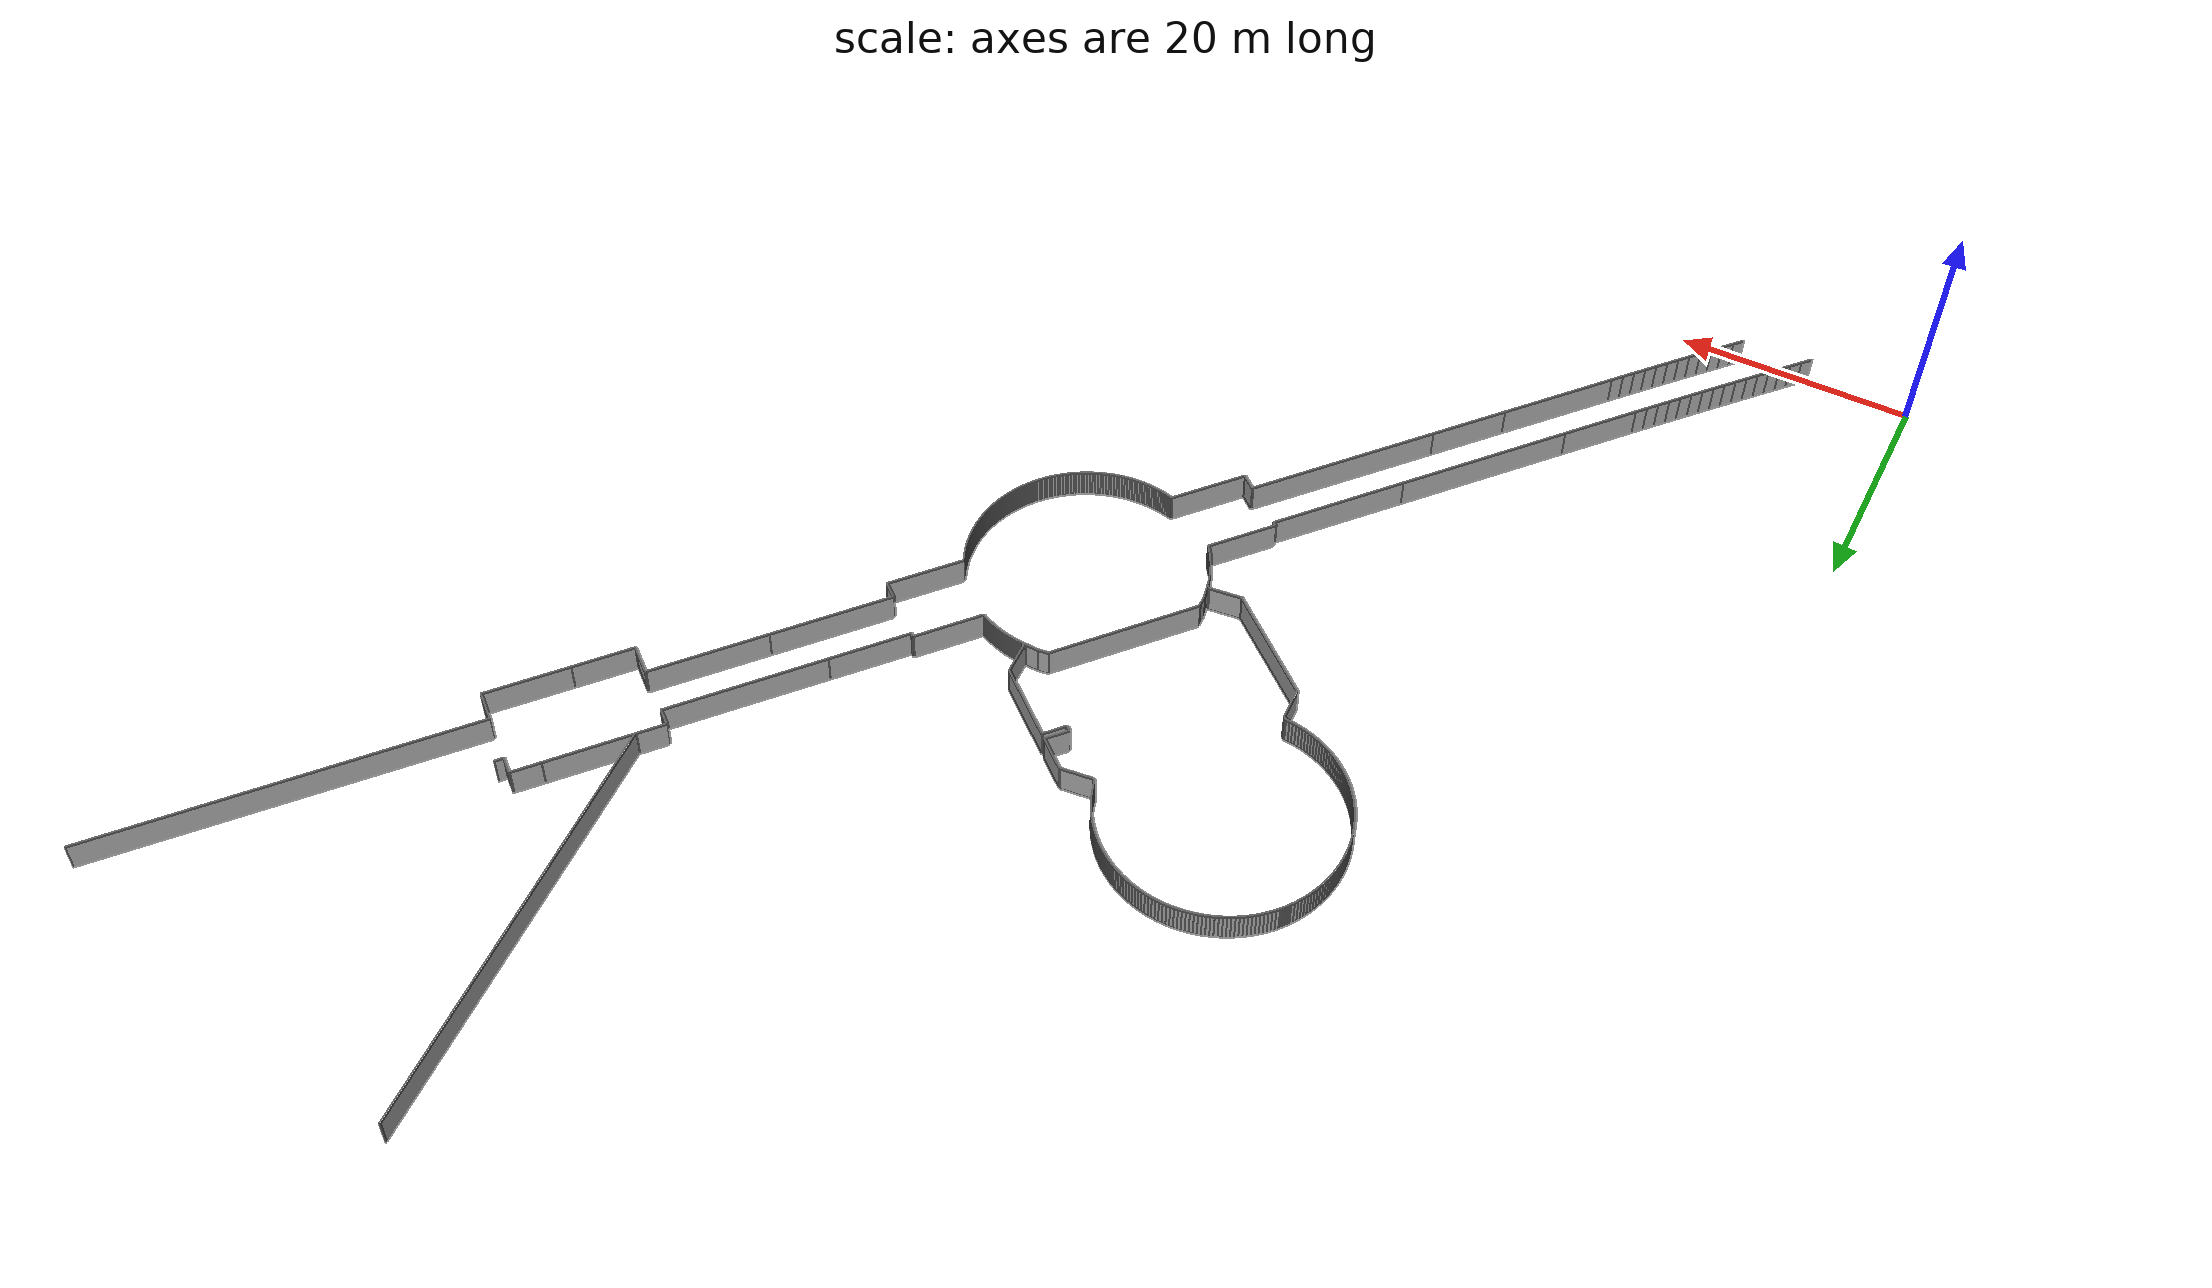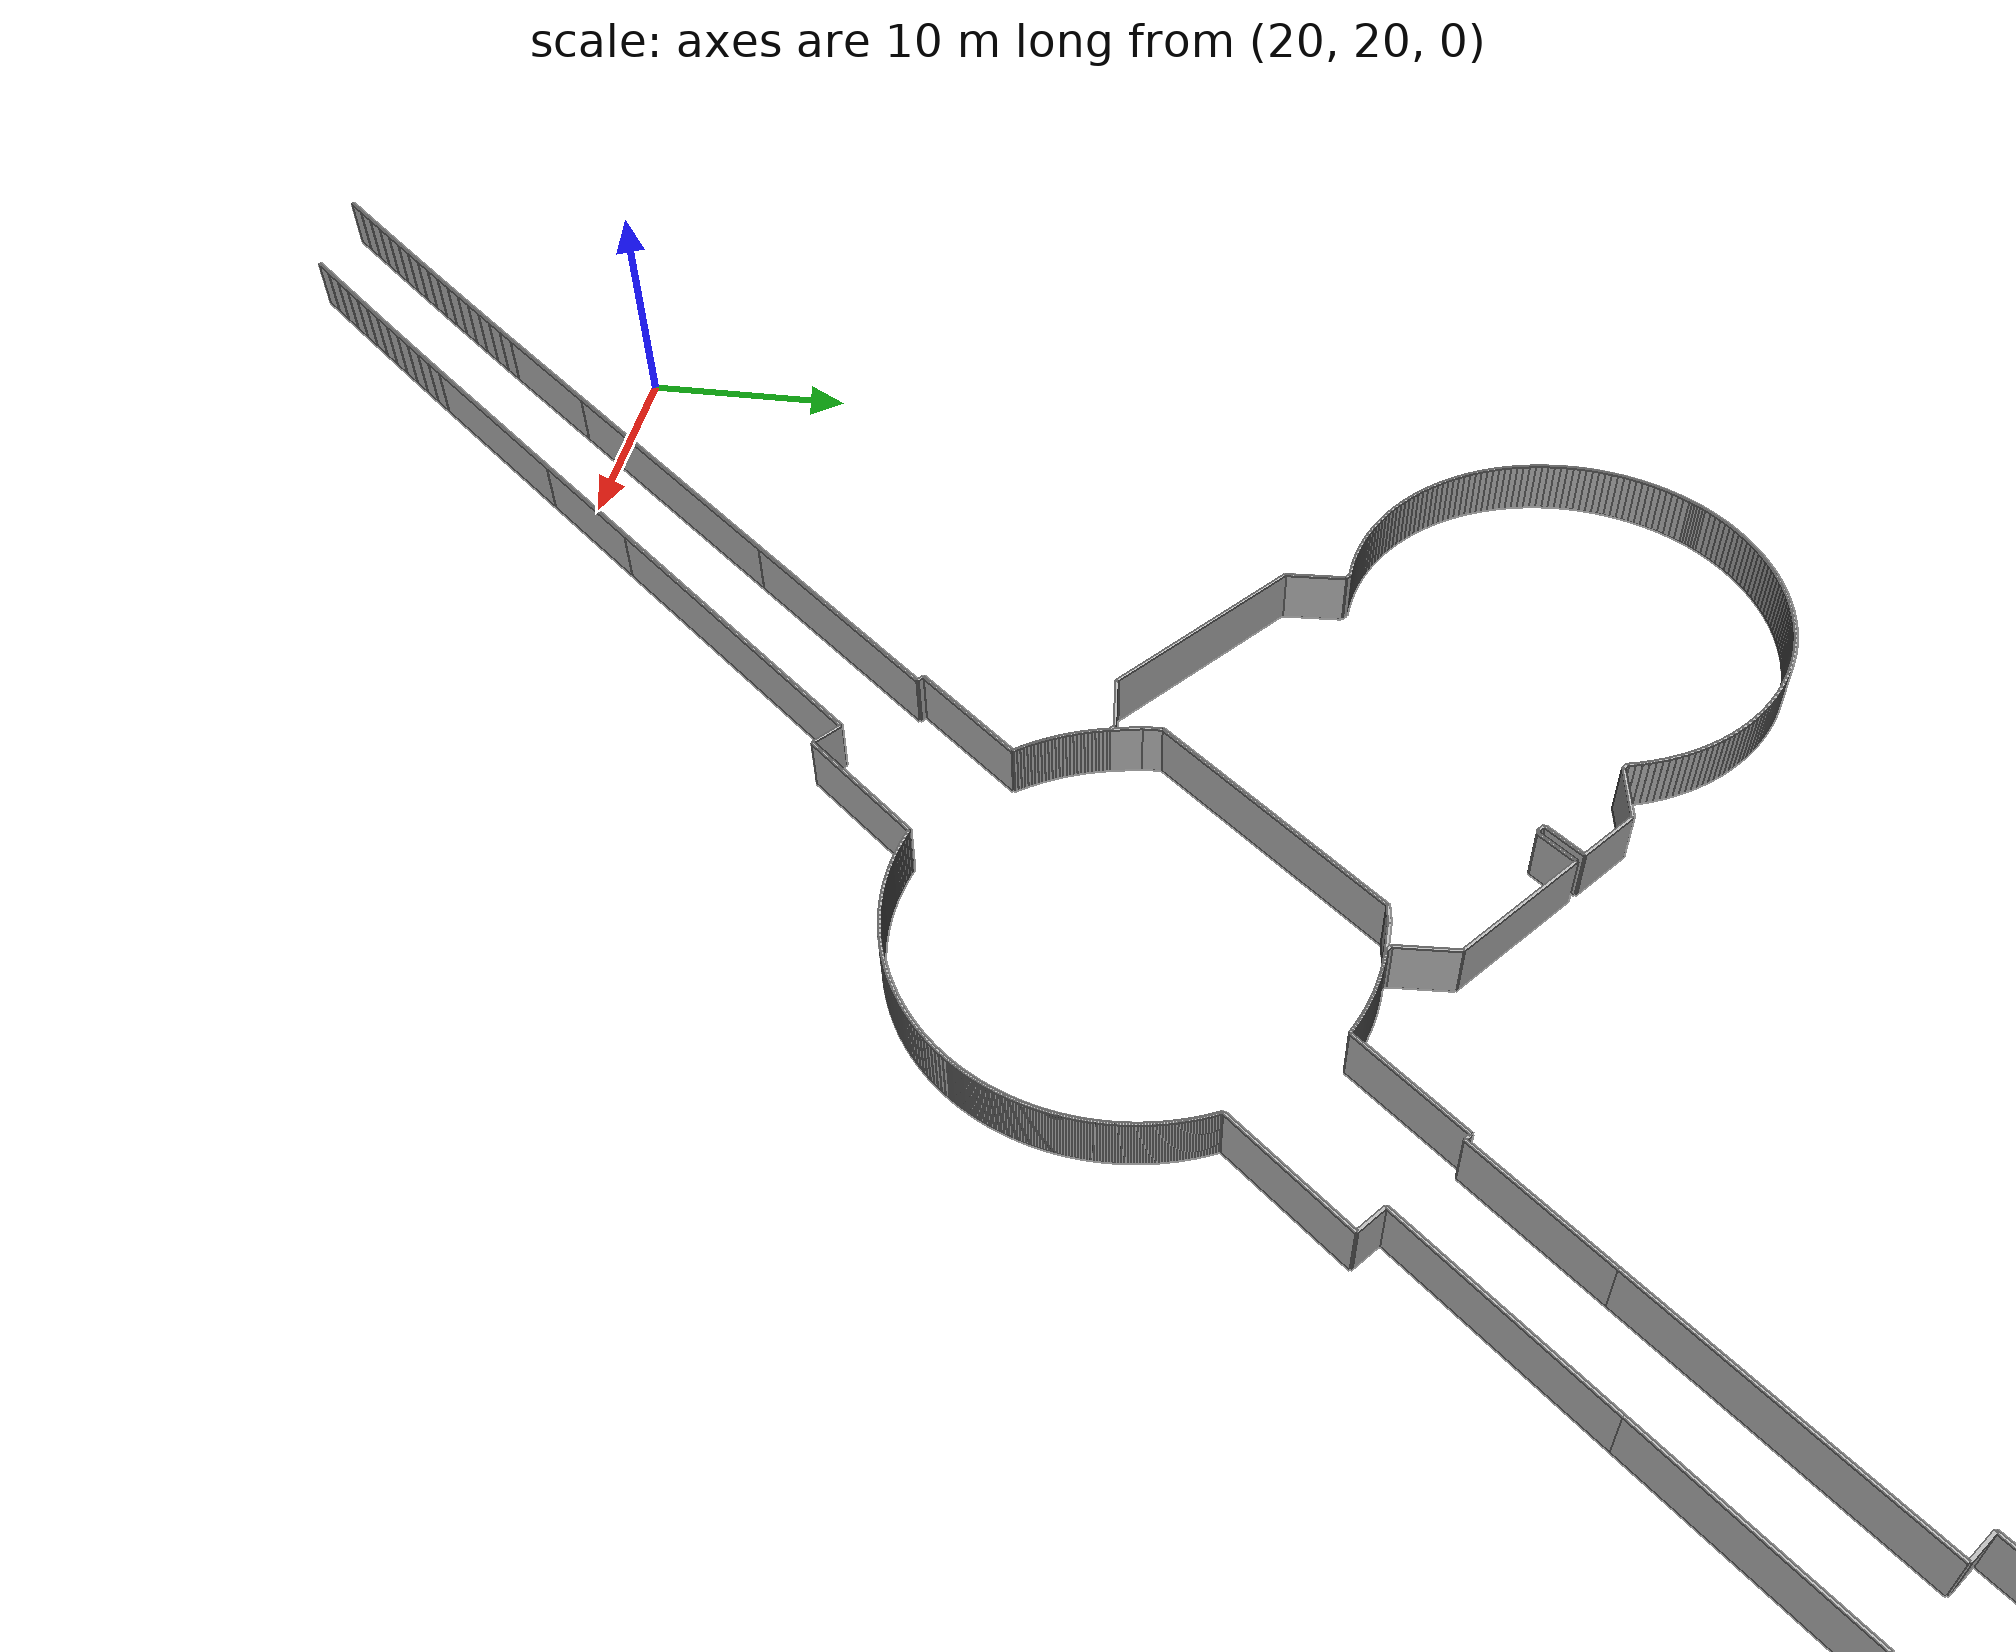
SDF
<?xml version="1.0" ?>
<sdf version="1.6">
  <model name="sps_2005">
    <pose frame="">0 0 0 0 -0 0</pose>
    <static>1</static>
    <self_collide>0</self_collide>
    <allow_auto_disable>0</allow_auto_disable>
    <link name="Wall58">
      <kinematic>0</kinematic>
      <gravity>1</gravity>
      <self_collide>0</self_collide>
      <collision name="collision">
        <geometry>
          <box>
            <size>0.350354 0.15 2.5</size>
          </box>
        </geometry>
        <pose frame="">0 0 0 0 -0 0</pose>
      </collision>
      <visual name="visual">
        <geometry>
          <box>
            <size>0.350354 0.15 2.5</size>
          </box>
        </geometry>
        <pose frame="">0 0 0 0 -0 0</pose>
        <cast_shadows>1</cast_shadows>
        <transparency>0.0</transparency>
      </visual>
      <pose frame="">62.3785 62.6861 1.25 0 0 -0.702523</pose>
    </link>
    <link name="Wall59">
      <kinematic>0</kinematic>
      <gravity>1</gravity>
      <self_collide>0</self_collide>
      <collision name="collision">
        <geometry>
          <box>
            <size>13.6817 0.15 2.5</size>
          </box>
        </geometry>
        <pose frame="">0 0 0 0 -0 0</pose>
      </collision>
      <visual name="visual">
        <geometry>
          <box>
            <size>13.6817 0.15 2.5</size>
          </box>
        </geometry>
        <pose frame="">0 0 0 0 -0 0</pose>
        <cast_shadows>1</cast_shadows>
        <transparency>0.0</transparency>
      </visual>
      <pose frame="">71.4438 73.1119 1.25 0 0 -2.27383</pose>
    </link>
    <link name="Wall60">
      <kinematic>0</kinematic>
      <gravity>1</gravity>
      <self_collide>0</self_collide>
      <collision name="collision">
        <geometry>
          <box>
            <size>6.97376 0.15 2.5</size>
          </box>
        </geometry>
        <pose frame="">0 0 0 0 -0 0</pose>
      </collision>
      <visual name="visual">
        <geometry>
          <box>
            <size>6.97376 0.15 2.5</size>
          </box>
        </geometry>
        <pose frame="">0 0 0 0 -0 0</pose>
        <cast_shadows>1</cast_shadows>
        <transparency>0.0</transparency>
      </visual>
      <pose frame="">64.7666 65.233 1.25 0 0 -2.27383</pose>
    </link>
    <link name="Wall61">
      <kinematic>0</kinematic>
      <gravity>1</gravity>
      <self_collide>0</self_collide>
      <collision name="collision">
        <geometry>
          <box>
            <size>2.50061 0.15 2.5</size>
          </box>
        </geometry>
        <pose frame="">0 0 0 0 -0 0</pose>
      </collision>
      <visual name="visual">
        <geometry>
          <box>
            <size>2.50061 0.15 2.5</size>
          </box>
        </geometry>
        <pose frame="">0 0 0 0 -0 0</pose>
        <cast_shadows>1</cast_shadows>
        <transparency>0.0</transparency>
      </visual>
      <pose frame="">81.9957 87.8829 1.25 0 0 -2.27365</pose>
    </link>
    <link name="Wall62">
      <kinematic>0</kinematic>
      <gravity>1</gravity>
      <self_collide>0</self_collide>
      <collision name="collision">
        <geometry>
          <box>
            <size>5.28264 0.15 2.5</size>
          </box>
        </geometry>
        <pose frame="">0 0 0 0 -0 0</pose>
      </collision>
      <visual name="visual">
        <geometry>
          <box>
            <size>5.28264 0.15 2.5</size>
          </box>
        </geometry>
        <pose frame="">0 0 0 0 -0 0</pose>
        <cast_shadows>1</cast_shadows>
        <transparency>0.0</transparency>
      </visual>
      <pose frame="">82.7617 75.9493 1.25 0 -0 0.867764</pose>
    </link>
    <link name="Wall63">
      <kinematic>0</kinematic>
      <gravity>1</gravity>
      <self_collide>0</self_collide>
      <collision name="collision">
        <geometry>
          <box>
            <size>7.21753 0.15 2.5</size>
          </box>
        </geometry>
        <pose frame="">0 0 0 0 -0 0</pose>
      </collision>
      <visual name="visual">
        <geometry>
          <box>
            <size>7.21753 0.15 2.5</size>
          </box>
        </geometry>
        <pose frame="">0 0 0 0 -0 0</pose>
        <cast_shadows>1</cast_shadows>
        <transparency>0.0</transparency>
      </visual>
      <pose frame="">86.8026 80.7174 1.25 0 -0 0.867764</pose>
    </link>
    <link name="Wall65">
      <kinematic>0</kinematic>
      <gravity>1</gravity>
      <self_collide>0</self_collide>
      <collision name="collision">
        <geometry>
          <box>
            <size>0.806139 0.15 2.5</size>
          </box>
        </geometry>
        <pose frame="">0 0 0 0 -0 0</pose>
      </collision>
      <visual name="visual">
        <geometry>
          <box>
            <size>0.806139 0.15 2.5</size>
          </box>
        </geometry>
        <pose frame="">0 0 0 0 -0 0</pose>
        <cast_shadows>1</cast_shadows>
        <transparency>0.0</transparency>
      </visual>
      <pose frame="">84.2089 88.174 1.25 0 0 -2.2738</pose>
    </link>
    <link name="Wall139">
      <kinematic>0</kinematic>
      <gravity>1</gravity>
      <self_collide>0</self_collide>
      <collision name="collision">
        <geometry>
          <box>
            <size>6.63014 0.15 2.5</size>
          </box>
        </geometry>
        <pose frame="">0 0 0 0 -0 0</pose>
      </collision>
      <visual name="visual">
        <geometry>
          <box>
            <size>6.63014 0.15 2.5</size>
          </box>
        </geometry>
        <pose frame="">0 0 0 0 -0 0</pose>
        <cast_shadows>1</cast_shadows>
        <transparency>0.0</transparency>
      </visual>
      <pose frame="">48.5365 37.3412 1.25 0 -0 0.86781</pose>
    </link>
    <link name="Wall140">
      <kinematic>0</kinematic>
      <gravity>1</gravity>
      <self_collide>0</self_collide>
      <collision name="collision">
        <geometry>
          <box>
            <size>1.51018 0.15 2.5</size>
          </box>
        </geometry>
        <pose frame="">0 0 0 0 -0 0</pose>
      </collision>
      <visual name="visual">
        <geometry>
          <box>
            <size>1.51018 0.15 2.5</size>
          </box>
        </geometry>
        <pose frame="">0 0 0 0 -0 0</pose>
        <cast_shadows>1</cast_shadows>
        <transparency>0.0</transparency>
      </visual>
      <pose frame="">66.2469 59.4087 1.25 0 0 -0.702713</pose>
    </link>
    <link name="Wall141">
      <kinematic>0</kinematic>
      <gravity>1</gravity>
      <self_collide>0</self_collide>
      <collision name="collision">
        <geometry>
          <box>
            <size>1.50024 0.15 2.5</size>
          </box>
        </geometry>
        <pose frame="">0 0 0 0 -0 0</pose>
      </collision>
      <visual name="visual">
        <geometry>
          <box>
            <size>1.50024 0.15 2.5</size>
          </box>
        </geometry>
        <pose frame="">0 0 0 0 -0 0</pose>
        <cast_shadows>1</cast_shadows>
        <transparency>0.0</transparency>
      </visual>
      <pose frame="">75.2942 78.8154 1.25 0 0 -0.70251</pose>
    </link>
    <link name="Wall246">
      <kinematic>0</kinematic>
      <gravity>1</gravity>
      <self_collide>0</self_collide>
      <collision name="collision">
        <geometry>
          <box>
            <size>10.2849 0.15 2.5</size>
          </box>
        </geometry>
        <pose frame="">0 0 0 0 -0 0</pose>
      </collision>
      <visual name="visual">
        <geometry>
          <box>
            <size>10.2849 0.15 2.5</size>
          </box>
        </geometry>
        <pose frame="">0 0 0 0 -0 0</pose>
        <cast_shadows>1</cast_shadows>
        <transparency>0.0</transparency>
      </visual>
      <pose frame="">26.7513 13.97 1.25 0 -0 0.867762</pose>
    </link>
    <link name="Wall247">
      <kinematic>0</kinematic>
      <gravity>1</gravity>
      <self_collide>0</self_collide>
      <collision name="collision">
        <geometry>
          <box>
            <size>6.79533 0.15 2.5</size>
          </box>
        </geometry>
        <pose frame="">0 0 0 0 -0 0</pose>
      </collision>
      <visual name="visual">
        <geometry>
          <box>
            <size>6.79533 0.15 2.5</size>
          </box>
        </geometry>
        <pose frame="">0 0 0 0 -0 0</pose>
        <cast_shadows>1</cast_shadows>
        <transparency>0.0</transparency>
      </visual>
      <pose frame="">32.2727 20.4851 1.25 0 -0 0.867762</pose>
    </link>
    <link name="Wall248">
      <kinematic>0</kinematic>
      <gravity>1</gravity>
      <self_collide>0</self_collide>
      <collision name="collision">
        <geometry>
          <box>
            <size>16.6612 0.15 2.5</size>
          </box>
        </geometry>
        <pose frame="">0 0 0 0 -0 0</pose>
      </collision>
      <visual name="visual">
        <geometry>
          <box>
            <size>16.6612 0.15 2.5</size>
          </box>
        </geometry>
        <pose frame="">0 0 0 0 -0 0</pose>
        <cast_shadows>1</cast_shadows>
        <transparency>0.0</transparency>
      </visual>
      <pose frame="">39.8555 29.4324 1.25 0 -0 0.867762</pose>
    </link>
    <link name="Wall249">
      <kinematic>0</kinematic>
      <gravity>1</gravity>
      <self_collide>0</self_collide>
      <collision name="collision">
        <geometry>
          <box>
            <size>5.99993 0.15 2.5</size>
          </box>
        </geometry>
        <pose frame="">0 0 0 0 -0 0</pose>
      </collision>
      <visual name="visual">
        <geometry>
          <box>
            <size>5.99993 0.15 2.5</size>
          </box>
        </geometry>
        <pose frame="">0 0 0 0 -0 0</pose>
        <cast_shadows>1</cast_shadows>
        <transparency>0.0</transparency>
      </visual>
      <pose frame="">60.3054 60.5105 1.25 0 -0 0.867846</pose>
    </link>
    <link name="Wall312">
      <kinematic>0</kinematic>
      <gravity>1</gravity>
      <self_collide>0</self_collide>
      <collision name="collision">
        <geometry>
          <box>
            <size>11.7757 0.15 2.5</size>
          </box>
        </geometry>
        <pose frame="">0 0 0 0 -0 0</pose>
      </collision>
      <visual name="visual">
        <geometry>
          <box>
            <size>11.7757 0.15 2.5</size>
          </box>
        </geometry>
        <pose frame="">0 0 0 0 -0 0</pose>
        <cast_shadows>1</cast_shadows>
        <transparency>0.0</transparency>
      </visual>
      <pose frame="">38.2761 33.9729 1.25 0 0 -2.27383</pose>
    </link>
    <link name="Wall313">
      <kinematic>0</kinematic>
      <gravity>1</gravity>
      <self_collide>0</self_collide>
      <collision name="collision">
        <geometry>
          <box>
            <size>15.1897 0.15 2.5</size>
          </box>
        </geometry>
        <pose frame="">0 0 0 0 -0 0</pose>
      </collision>
      <visual name="visual">
        <geometry>
          <box>
            <size>15.1897 0.15 2.5</size>
          </box>
        </geometry>
        <pose frame="">0 0 0 0 -0 0</pose>
        <cast_shadows>1</cast_shadows>
        <transparency>0.0</transparency>
      </visual>
      <pose frame="">29.5591 23.6871 1.25 0 0 -2.27383</pose>
    </link>
    <link name="Wall314">
      <kinematic>0</kinematic>
      <gravity>1</gravity>
      <self_collide>0</self_collide>
      <collision name="collision">
        <geometry>
          <box>
            <size>6.76583 0.15 2.5</size>
          </box>
        </geometry>
        <pose frame="">0 0 0 0 -0 0</pose>
      </collision>
      <visual name="visual">
        <geometry>
          <box>
            <size>6.76583 0.15 2.5</size>
          </box>
        </geometry>
        <pose frame="">0 0 0 0 -0 0</pose>
        <cast_shadows>1</cast_shadows>
        <transparency>0.0</transparency>
      </visual>
      <pose frame="">22.4616 15.3123 1.25 0 0 -2.27383</pose>
    </link>
    <link name="Wall315">
      <kinematic>0</kinematic>
      <gravity>1</gravity>
      <self_collide>0</self_collide>
      <collision name="collision">
        <geometry>
          <box>
            <size>6.63013 0.15 2.5</size>
          </box>
        </geometry>
        <pose frame="">0 0 0 0 -0 0</pose>
      </collision>
      <visual name="visual">
        <geometry>
          <box>
            <size>6.63013 0.15 2.5</size>
          </box>
        </geometry>
        <pose frame="">0 0 0 0 -0 0</pose>
        <cast_shadows>1</cast_shadows>
        <transparency>0.0</transparency>
      </visual>
      <pose frame="">64.6799 56.3916 1.25 0 0 -2.2738</pose>
    </link>
    <link name="Wall377">
      <kinematic>0</kinematic>
      <gravity>1</gravity>
      <self_collide>0</self_collide>
      <collision name="collision">
        <geometry>
          <box>
            <size>6.00041 0.15 2.5</size>
          </box>
        </geometry>
        <pose frame="">0 0 0 0 -0 0</pose>
      </collision>
      <visual name="visual">
        <geometry>
          <box>
            <size>6.00041 0.15 2.5</size>
          </box>
        </geometry>
        <pose frame="">0 0 0 0 -0 0</pose>
        <cast_shadows>1</cast_shadows>
        <transparency>0.0</transparency>
      </visual>
      <pose frame="">43.7558 40.9795 1.25 0 0 -2.27373</pose>
    </link>
    <link name="Wall378">
      <kinematic>0</kinematic>
      <gravity>1</gravity>
      <self_collide>0</self_collide>
      <collision name="collision">
        <geometry>
          <box>
            <size>1.50944 0.15 2.5</size>
          </box>
        </geometry>
        <pose frame="">0 0 0 0 -0 0</pose>
      </collision>
      <visual name="visual">
        <geometry>
          <box>
            <size>1.50944 0.15 2.5</size>
          </box>
        </geometry>
        <pose frame="">0 0 0 0 -0 0</pose>
        <cast_shadows>1</cast_shadows>
        <transparency>0.0</transparency>
      </visual>
      <pose frame="">45.8174 35.2999 1.25 0 0 -0.702758</pose>
    </link>
    <link name="Wall379">
      <kinematic>0</kinematic>
      <gravity>1</gravity>
      <self_collide>0</self_collide>
      <collision name="collision">
        <geometry>
          <box>
            <size>2.66028 0.15 2.5</size>
          </box>
        </geometry>
        <pose frame="">0 0 0 0 -0 0</pose>
      </collision>
      <visual name="visual">
        <geometry>
          <box>
            <size>2.66028 0.15 2.5</size>
          </box>
        </geometry>
        <pose frame="">0 0 0 0 -0 0</pose>
        <cast_shadows>1</cast_shadows>
        <transparency>0.0</transparency>
      </visual>
      <pose frame="">88.1209 84.3303 1.25 0 -0 2.43873</pose>
    </link>
    <link name="Wall470">
      <kinematic>0</kinematic>
      <gravity>1</gravity>
      <self_collide>0</self_collide>
      <collision name="collision">
        <geometry>
          <box>
            <size>0.30032 0.15 2.5</size>
          </box>
        </geometry>
        <pose frame="">0 0 0 0 -0 0</pose>
      </collision>
      <visual name="visual">
        <geometry>
          <box>
            <size>0.30032 0.15 2.5</size>
          </box>
        </geometry>
        <pose frame="">0 0 0 0 -0 0</pose>
        <cast_shadows>1</cast_shadows>
        <transparency>0.0</transparency>
      </visual>
      <pose frame="">43.7684 47.2602 1.25 0 0 -0.701374</pose>
    </link>
    <link name="Wall471">
      <kinematic>0</kinematic>
      <gravity>1</gravity>
      <self_collide>0</self_collide>
      <collision name="collision">
        <geometry>
          <box>
            <size>10.4816 0.15 2.5</size>
          </box>
        </geometry>
        <pose frame="">0 0 0 0 -0 0</pose>
      </collision>
      <visual name="visual">
        <geometry>
          <box>
            <size>10.4816 0.15 2.5</size>
          </box>
        </geometry>
        <pose frame="">0 0 0 0 -0 0</pose>
        <cast_shadows>1</cast_shadows>
        <transparency>0.0</transparency>
      </visual>
      <pose frame="">69.0589 63.8949 1.25 0 -0 0.867786</pose>
    </link>
    <link name="Wall472">
      <kinematic>0</kinematic>
      <gravity>1</gravity>
      <self_collide>0</self_collide>
      <collision name="collision">
        <geometry>
          <box>
            <size>10.1733 0.15 2.5</size>
          </box>
        </geometry>
        <pose frame="">0 0 0 0 -0 0</pose>
      </collision>
      <visual name="visual">
        <geometry>
          <box>
            <size>10.1733 0.15 2.5</size>
          </box>
        </geometry>
        <pose frame="">0 0 0 0 -0 0</pose>
        <cast_shadows>1</cast_shadows>
        <transparency>0.0</transparency>
      </visual>
      <pose frame="">75.7358 71.7737 1.25 0 -0 0.867786</pose>
    </link>
    <link name="Wall473">
      <kinematic>0</kinematic>
      <gravity>1</gravity>
      <self_collide>0</self_collide>
      <collision name="collision">
        <geometry>
          <box>
            <size>2.66041 0.15 2.5</size>
          </box>
        </geometry>
        <pose frame="">0 0 0 0 -0 0</pose>
      </collision>
      <visual name="visual">
        <geometry>
          <box>
            <size>2.66041 0.15 2.5</size>
          </box>
        </geometry>
        <pose frame="">0 0 0 0 -0 0</pose>
        <cast_shadows>1</cast_shadows>
        <transparency>0.0</transparency>
      </visual>
      <pose frame="">80.0392 74.7943 1.25 0 0 -0.703025</pose>
    </link>
    <link name="Wall641">
      <kinematic>0</kinematic>
      <gravity>1</gravity>
      <self_collide>0</self_collide>
      <collision name="collision">
        <geometry>
          <box>
            <size>0.349393 0.15 2.5</size>
          </box>
        </geometry>
        <pose frame="">0 0 0 0 -0 0</pose>
      </collision>
      <visual name="visual">
        <geometry>
          <box>
            <size>0.349393 0.15 2.5</size>
          </box>
        </geometry>
        <pose frame="">0 0 0 0 -0 0</pose>
        <cast_shadows>1</cast_shadows>
        <transparency>0.0</transparency>
      </visual>
      <pose frame="">41.9495 38.5776 1.25 0 0 -0.70279</pose>
    </link>
    <link name="Wall642">
      <kinematic>0</kinematic>
      <gravity>1</gravity>
      <self_collide>0</self_collide>
      <collision name="collision">
        <geometry>
          <box>
            <size>0.299507 0.15 2.5</size>
          </box>
        </geometry>
        <pose frame="">0 0 0 0 -0 0</pose>
      </collision>
      <visual name="visual">
        <geometry>
          <box>
            <size>0.299507 0.15 2.5</size>
          </box>
        </geometry>
        <pose frame="">0 0 0 0 -0 0</pose>
        <cast_shadows>1</cast_shadows>
        <transparency>0.0</transparency>
      </visual>
      <pose frame="">54.1125 59.4667 1.25 0 0 -0.704471</pose>
    </link>
    <link name="Wall643">
      <kinematic>0</kinematic>
      <gravity>1</gravity>
      <self_collide>0</self_collide>
      <collision name="collision">
        <geometry>
          <box>
            <size>2.5007 0.15 2.5</size>
          </box>
        </geometry>
        <pose frame="">0 0 0 0 -0 0</pose>
      </collision>
      <visual name="visual">
        <geometry>
          <box>
            <size>2.5007 0.15 2.5</size>
          </box>
        </geometry>
        <pose frame="">0 0 0 0 -0 0</pose>
        <cast_shadows>1</cast_shadows>
        <transparency>0.0</transparency>
      </visual>
      <pose frame="">75.5302 80.2538 1.25 0 0 -2.27404</pose>
    </link>
    <link name="Wall644">
      <kinematic>0</kinematic>
      <gravity>1</gravity>
      <self_collide>0</self_collide>
      <collision name="collision">
        <geometry>
          <box>
            <size>1.50045 0.15 2.5</size>
          </box>
        </geometry>
        <pose frame="">0 0 0 0 -0 0</pose>
      </collision>
      <visual name="visual">
        <geometry>
          <box>
            <size>1.50045 0.15 2.5</size>
          </box>
        </geometry>
        <pose frame="">0 0 0 0 -0 0</pose>
        <cast_shadows>1</cast_shadows>
        <transparency>0.0</transparency>
      </visual>
      <pose frame="">83.3761 88.3517 1.25 0 -0 2.43829</pose>
    </link>
    <link name="Wall645">
      <kinematic>0</kinematic>
      <gravity>1</gravity>
      <self_collide>0</self_collide>
      <collision name="collision">
        <geometry>
          <box>
            <size>32.5434 0.15 2.5</size>
          </box>
        </geometry>
        <pose frame="">0 0 0 0 -0 0</pose>
      </collision>
      <visual name="visual">
        <geometry>
          <box>
            <size>32.5434 0.15 2.5</size>
          </box>
        </geometry>
        <pose frame="">0 0 0 0 -0 0</pose>
        <cast_shadows>1</cast_shadows>
        <transparency>0.0</transparency>
      </visual>
      <pose frame="">97.6261 97.6037 1.25 0 -0 0.867779</pose>
    </link>
    <link name="Wall1125">
      <kinematic>0</kinematic>
      <gravity>1</gravity>
      <self_collide>0</self_collide>
      <collision name="collision">
        <geometry>
          <box>
            <size>2.75885 0.15 2.5</size>
          </box>
        </geometry>
        <pose frame="">0 0 0 0 -0 0</pose>
      </collision>
      <visual name="visual">
        <geometry>
          <box>
            <size>2.75885 0.15 2.5</size>
          </box>
        </geometry>
        <pose frame="">0 0 0 0 -0 0</pose>
        <cast_shadows>1</cast_shadows>
        <transparency>0.0</transparency>
      </visual>
      <pose frame="">53.9205 60.9409 1.25 0 0 -1.51393</pose>
    </link>
    <link name="Wall1126">
      <kinematic>0</kinematic>
      <gravity>1</gravity>
      <self_collide>0</self_collide>
      <collision name="collision">
        <geometry>
          <box>
            <size>0.299202 0.15 2.5</size>
          </box>
        </geometry>
        <pose frame="">0 0 0 0 -0 0</pose>
      </collision>
      <visual name="visual">
        <geometry>
          <box>
            <size>0.299202 0.15 2.5</size>
          </box>
        </geometry>
        <pose frame="">0 0 0 0 -0 0</pose>
        <cast_shadows>1</cast_shadows>
        <transparency>0.0</transparency>
      </visual>
      <pose frame="">54.1128 59.4668 1.25 0 0 -0.704533</pose>
    </link>
    <link name="Wall1127">
      <kinematic>0</kinematic>
      <gravity>1</gravity>
      <self_collide>0</self_collide>
      <collision name="collision">
        <geometry>
          <box>
            <size>1.3896 0.15 2.5</size>
          </box>
        </geometry>
        <pose frame="">0 0 0 0 -0 0</pose>
      </collision>
      <visual name="visual">
        <geometry>
          <box>
            <size>1.3896 0.15 2.5</size>
          </box>
        </geometry>
        <pose frame="">0 0 0 0 -0 0</pose>
        <cast_shadows>1</cast_shadows>
        <transparency>0.0</transparency>
      </visual>
      <pose frame="">53.5327 59.4013 1.25 0 -0 3.09638</pose>
    </link>
    <link name="Wall1128">
      <kinematic>0</kinematic>
      <gravity>1</gravity>
      <self_collide>0</self_collide>
      <collision name="collision">
        <geometry>
          <box>
            <size>0.884401 0.15 2.5</size>
          </box>
        </geometry>
        <pose frame="">0 0 0 0 -0 0</pose>
      </collision>
      <visual name="visual">
        <geometry>
          <box>
            <size>0.884401 0.15 2.5</size>
          </box>
        </geometry>
        <pose frame="">0 0 0 0 -0 0</pose>
        <cast_shadows>1</cast_shadows>
        <transparency>0.0</transparency>
      </visual>
      <pose frame="">52.3997 59.3788 1.25 0 0 -3.01941</pose>
    </link>
    <link name="Wall1129">
      <kinematic>0</kinematic>
      <gravity>1</gravity>
      <self_collide>0</self_collide>
      <collision name="collision">
        <geometry>
          <box>
            <size>13.0009 0.15 2.5</size>
          </box>
        </geometry>
        <pose frame="">0 0 0 0 -0 0</pose>
      </collision>
      <visual name="visual">
        <geometry>
          <box>
            <size>13.0009 0.15 2.5</size>
          </box>
        </geometry>
        <pose frame="">0 0 0 0 -0 0</pose>
        <cast_shadows>1</cast_shadows>
        <transparency>0.0</transparency>
      </visual>
      <pose frame="">47.7584 54.3655 1.25 0 0 -2.27375</pose>
    </link>
    <link name="Wall1130">
      <kinematic>0</kinematic>
      <gravity>1</gravity>
      <self_collide>0</self_collide>
      <collision name="collision">
        <geometry>
          <box>
            <size>0.884413 0.15 2.5</size>
          </box>
        </geometry>
        <pose frame="">0 0 0 0 -0 0</pose>
      </collision>
      <visual name="visual">
        <geometry>
          <box>
            <size>0.884413 0.15 2.5</size>
          </box>
        </geometry>
        <pose frame="">0 0 0 0 -0 0</pose>
        <cast_shadows>1</cast_shadows>
        <transparency>0.0</transparency>
      </visual>
      <pose frame="">43.5749 48.9643 1.25 0 0 -1.52806</pose>
    </link>
    <link name="Wall1131">
      <kinematic>0</kinematic>
      <gravity>1</gravity>
      <self_collide>0</self_collide>
      <collision name="collision">
        <geometry>
          <box>
            <size>1.38967 0.15 2.5</size>
          </box>
        </geometry>
        <pose frame="">0 0 0 0 -0 0</pose>
      </collision>
      <visual name="visual">
        <geometry>
          <box>
            <size>1.38967 0.15 2.5</size>
          </box>
        </geometry>
        <pose frame="">0 0 0 0 -0 0</pose>
        <cast_shadows>1</cast_shadows>
        <transparency>0.0</transparency>
      </visual>
      <pose frame="">43.7385 47.8429 1.25 0 0 -1.36099</pose>
    </link>
    <link name="Wall1132">
      <kinematic>0</kinematic>
      <gravity>1</gravity>
      <self_collide>0</self_collide>
      <collision name="collision">
        <geometry>
          <box>
            <size>0.30032 0.15 2.5</size>
          </box>
        </geometry>
        <pose frame="">0 0 0 0 -0 0</pose>
      </collision>
      <visual name="visual">
        <geometry>
          <box>
            <size>0.30032 0.15 2.5</size>
          </box>
        </geometry>
        <pose frame="">0 0 0 0 -0 0</pose>
        <cast_shadows>1</cast_shadows>
        <transparency>0.0</transparency>
      </visual>
      <pose frame="">43.7685 47.2602 1.25 0 -0 2.44022</pose>
    </link>
    <link name="Wall1133">
      <kinematic>0</kinematic>
      <gravity>1</gravity>
      <self_collide>0</self_collide>
      <collision name="collision">
        <geometry>
          <box>
            <size>2.75787 0.15 2.5</size>
          </box>
        </geometry>
        <pose frame="">0 0 0 0 -0 0</pose>
      </collision>
      <visual name="visual">
        <geometry>
          <box>
            <size>2.75787 0.15 2.5</size>
          </box>
        </geometry>
        <pose frame="">0 0 0 0 -0 0</pose>
        <cast_shadows>1</cast_shadows>
        <transparency>0.0</transparency>
      </visual>
      <pose frame="">42.283 47.2083 1.25 0 0 -3.03347</pose>
    </link>
    <link name="Wall1134">
      <kinematic>0</kinematic>
      <gravity>1</gravity>
      <self_collide>0</self_collide>
      <collision name="collision">
        <geometry>
          <box>
            <size>10.3999 0.15 2.5</size>
          </box>
        </geometry>
        <pose frame="">0 0 0 0 -0 0</pose>
      </collision>
      <visual name="visual">
        <geometry>
          <box>
            <size>10.3999 0.15 2.5</size>
          </box>
        </geometry>
        <pose frame="">0 0 0 0 -0 0</pose>
        <cast_shadows>1</cast_shadows>
        <transparency>0.0</transparency>
      </visual>
      <pose frame="">36.9448 50.421 1.25 0 -0 2.43867</pose>
    </link>
    <link name="Wall1135">
      <kinematic>0</kinematic>
      <gravity>1</gravity>
      <self_collide>0</self_collide>
      <collision name="collision">
        <geometry>
          <box>
            <size>2.75904 0.15 2.5</size>
          </box>
        </geometry>
        <pose frame="">0 0 0 0 -0 0</pose>
      </collision>
      <visual name="visual">
        <geometry>
          <box>
            <size>2.75904 0.15 2.5</size>
          </box>
        </geometry>
        <pose frame="">0 0 0 0 -0 0</pose>
        <cast_shadows>1</cast_shadows>
        <transparency>0.0</transparency>
      </visual>
      <pose frame="">32.899 55.1598 1.25 0 -0 1.62766</pose>
    </link>
    <link name="Wall1136">
      <kinematic>0</kinematic>
      <gravity>1</gravity>
      <self_collide>0</self_collide>
      <collision name="collision">
        <geometry>
          <box>
            <size>0.299242 0.15 2.5</size>
          </box>
        </geometry>
        <pose frame="">0 0 0 0 -0 0</pose>
      </collision>
      <visual name="visual">
        <geometry>
          <box>
            <size>0.299242 0.15 2.5</size>
          </box>
        </geometry>
        <pose frame="">0 0 0 0 -0 0</pose>
        <cast_shadows>1</cast_shadows>
        <transparency>0.0</transparency>
      </visual>
      <pose frame="">32.7067 56.634 1.25 0 -0 2.4369</pose>
    </link>
    <link name="Wall1137">
      <kinematic>0</kinematic>
      <gravity>1</gravity>
      <self_collide>0</self_collide>
      <collision name="collision">
        <geometry>
          <box>
            <size>0.304996 0.15 2.5</size>
          </box>
        </geometry>
        <pose frame="">0 0 0 0 -0 0</pose>
      </collision>
      <visual name="visual">
        <geometry>
          <box>
            <size>0.304996 0.15 2.5</size>
          </box>
        </geometry>
        <pose frame="">0 0 0 0 -0 0</pose>
        <cast_shadows>1</cast_shadows>
        <transparency>0.0</transparency>
      </visual>
      <pose frame="">32.4408 56.7442 1.25 0 -0 3.05423</pose>
    </link>
    <link name="Wall1138">
      <kinematic>0</kinematic>
      <gravity>1</gravity>
      <self_collide>0</self_collide>
      <collision name="collision">
        <geometry>
          <box>
            <size>0.304719 0.15 2.5</size>
          </box>
        </geometry>
        <pose frame="">0 0 0 0 -0 0</pose>
      </collision>
      <visual name="visual">
        <geometry>
          <box>
            <size>0.304719 0.15 2.5</size>
          </box>
        </geometry>
        <pose frame="">0 0 0 0 -0 0</pose>
        <cast_shadows>1</cast_shadows>
        <transparency>0.0</transparency>
      </visual>
      <pose frame="">32.1375 56.7754 1.25 0 -0 3.02395</pose>
    </link>
    <link name="Wall1139">
      <kinematic>0</kinematic>
      <gravity>1</gravity>
      <self_collide>0</self_collide>
      <collision name="collision">
        <geometry>
          <box>
            <size>0.304703 0.15 2.5</size>
          </box>
        </geometry>
        <pose frame="">0 0 0 0 -0 0</pose>
      </collision>
      <visual name="visual">
        <geometry>
          <box>
            <size>0.304703 0.15 2.5</size>
          </box>
        </geometry>
        <pose frame="">0 0 0 0 -0 0</pose>
        <cast_shadows>1</cast_shadows>
        <transparency>0.0</transparency>
      </visual>
      <pose frame="">31.8355 56.8157 1.25 0 -0 2.99403</pose>
    </link>
    <link name="Wall1140">
      <kinematic>0</kinematic>
      <gravity>1</gravity>
      <self_collide>0</self_collide>
      <collision name="collision">
        <geometry>
          <box>
            <size>0.304845 0.15 2.5</size>
          </box>
        </geometry>
        <pose frame="">0 0 0 0 -0 0</pose>
      </collision>
      <visual name="visual">
        <geometry>
          <box>
            <size>0.304845 0.15 2.5</size>
          </box>
        </geometry>
        <pose frame="">0 0 0 0 -0 0</pose>
        <cast_shadows>1</cast_shadows>
        <transparency>0.0</transparency>
      </visual>
      <pose frame="">31.5348 56.8652 1.25 0 -0 2.96285</pose>
    </link>
    <link name="Wall1141">
      <kinematic>0</kinematic>
      <gravity>1</gravity>
      <self_collide>0</self_collide>
      <collision name="collision">
        <geometry>
          <box>
            <size>0.304848 0.15 2.5</size>
          </box>
        </geometry>
        <pose frame="">0 0 0 0 -0 0</pose>
      </collision>
      <visual name="visual">
        <geometry>
          <box>
            <size>0.304848 0.15 2.5</size>
          </box>
        </geometry>
        <pose frame="">0 0 0 0 -0 0</pose>
        <cast_shadows>1</cast_shadows>
        <transparency>0.0</transparency>
      </visual>
      <pose frame="">31.2357 56.9239 1.25 0 -0 2.93265</pose>
    </link>
    <link name="Wall1142">
      <kinematic>0</kinematic>
      <gravity>1</gravity>
      <self_collide>0</self_collide>
      <collision name="collision">
        <geometry>
          <box>
            <size>0.304863 0.15 2.5</size>
          </box>
        </geometry>
        <pose frame="">0 0 0 0 -0 0</pose>
      </collision>
      <visual name="visual">
        <geometry>
          <box>
            <size>0.304863 0.15 2.5</size>
          </box>
        </geometry>
        <pose frame="">0 0 0 0 -0 0</pose>
        <cast_shadows>1</cast_shadows>
        <transparency>0.0</transparency>
      </visual>
      <pose frame="">30.9385 56.9916 1.25 0 -0 2.90268</pose>
    </link>
    <link name="Wall1143">
      <kinematic>0</kinematic>
      <gravity>1</gravity>
      <self_collide>0</self_collide>
      <collision name="collision">
        <geometry>
          <box>
            <size>0.304661 0.15 2.5</size>
          </box>
        </geometry>
        <pose frame="">0 0 0 0 -0 0</pose>
      </collision>
      <visual name="visual">
        <geometry>
          <box>
            <size>0.304661 0.15 2.5</size>
          </box>
        </geometry>
        <pose frame="">0 0 0 0 -0 0</pose>
        <cast_shadows>1</cast_shadows>
        <transparency>0.0</transparency>
      </visual>
      <pose frame="">30.6436 57.0684 1.25 0 -0 2.87105</pose>
    </link>
    <link name="Wall1144">
      <kinematic>0</kinematic>
      <gravity>1</gravity>
      <self_collide>0</self_collide>
      <collision name="collision">
        <geometry>
          <box>
            <size>0.304852 0.15 2.5</size>
          </box>
        </geometry>
        <pose frame="">0 0 0 0 -0 0</pose>
      </collision>
      <visual name="visual">
        <geometry>
          <box>
            <size>0.304852 0.15 2.5</size>
          </box>
        </geometry>
        <pose frame="">0 0 0 0 -0 0</pose>
        <cast_shadows>1</cast_shadows>
        <transparency>0.0</transparency>
      </visual>
      <pose frame="">30.3512 57.1542 1.25 0 -0 2.84118</pose>
    </link>
    <link name="Wall1145">
      <kinematic>0</kinematic>
      <gravity>1</gravity>
      <self_collide>0</self_collide>
      <collision name="collision">
        <geometry>
          <box>
            <size>0.304737 0.15 2.5</size>
          </box>
        </geometry>
        <pose frame="">0 0 0 0 -0 0</pose>
      </collision>
      <visual name="visual">
        <geometry>
          <box>
            <size>0.304737 0.15 2.5</size>
          </box>
        </geometry>
        <pose frame="">0 0 0 0 -0 0</pose>
        <cast_shadows>1</cast_shadows>
        <transparency>0.0</transparency>
      </visual>
      <pose frame="">30.0615 57.2488 1.25 0 -0 2.81072</pose>
    </link>
    <link name="Wall1146">
      <kinematic>0</kinematic>
      <gravity>1</gravity>
      <self_collide>0</self_collide>
      <collision name="collision">
        <geometry>
          <box>
            <size>0.304848 0.15 2.5</size>
          </box>
        </geometry>
        <pose frame="">0 0 0 0 -0 0</pose>
      </collision>
      <visual name="visual">
        <geometry>
          <box>
            <size>0.304848 0.15 2.5</size>
          </box>
        </geometry>
        <pose frame="">0 0 0 0 -0 0</pose>
        <cast_shadows>1</cast_shadows>
        <transparency>0.0</transparency>
      </visual>
      <pose frame="">29.7749 57.3522 1.25 0 -0 2.7802</pose>
    </link>
    <link name="Wall1147">
      <kinematic>0</kinematic>
      <gravity>1</gravity>
      <self_collide>0</self_collide>
      <collision name="collision">
        <geometry>
          <box>
            <size>0.304722 0.15 2.5</size>
          </box>
        </geometry>
        <pose frame="">0 0 0 0 -0 0</pose>
      </collision>
      <visual name="visual">
        <geometry>
          <box>
            <size>0.304722 0.15 2.5</size>
          </box>
        </geometry>
        <pose frame="">0 0 0 0 -0 0</pose>
        <cast_shadows>1</cast_shadows>
        <transparency>0.0</transparency>
      </visual>
      <pose frame="">29.4915 57.4643 1.25 0 -0 2.74967</pose>
    </link>
    <link name="Wall1148">
      <kinematic>0</kinematic>
      <gravity>1</gravity>
      <self_collide>0</self_collide>
      <collision name="collision">
        <geometry>
          <box>
            <size>0.304824 0.15 2.5</size>
          </box>
        </geometry>
        <pose frame="">0 0 0 0 -0 0</pose>
      </collision>
      <visual name="visual">
        <geometry>
          <box>
            <size>0.304824 0.15 2.5</size>
          </box>
        </geometry>
        <pose frame="">0 0 0 0 -0 0</pose>
        <cast_shadows>1</cast_shadows>
        <transparency>0.0</transparency>
      </visual>
      <pose frame="">29.2117 57.585 1.25 0 -0 2.71906</pose>
    </link>
    <link name="Wall1149">
      <kinematic>0</kinematic>
      <gravity>1</gravity>
      <self_collide>0</self_collide>
      <collision name="collision">
        <geometry>
          <box>
            <size>0.304831 0.15 2.5</size>
          </box>
        </geometry>
        <pose frame="">0 0 0 0 -0 0</pose>
      </collision>
      <visual name="visual">
        <geometry>
          <box>
            <size>0.304831 0.15 2.5</size>
          </box>
        </geometry>
        <pose frame="">0 0 0 0 -0 0</pose>
        <cast_shadows>1</cast_shadows>
        <transparency>0.0</transparency>
      </visual>
      <pose frame="">28.9356 57.7141 1.25 0 -0 2.68923</pose>
    </link>
    <link name="Wall1150">
      <kinematic>0</kinematic>
      <gravity>1</gravity>
      <self_collide>0</self_collide>
      <collision name="collision">
        <geometry>
          <box>
            <size>0.304734 0.15 2.5</size>
          </box>
        </geometry>
        <pose frame="">0 0 0 0 -0 0</pose>
      </collision>
      <visual name="visual">
        <geometry>
          <box>
            <size>0.304734 0.15 2.5</size>
          </box>
        </geometry>
        <pose frame="">0 0 0 0 -0 0</pose>
        <cast_shadows>1</cast_shadows>
        <transparency>0.0</transparency>
      </visual>
      <pose frame="">28.6636 57.8515 1.25 0 -0 2.65833</pose>
    </link>
    <link name="Wall1151">
      <kinematic>0</kinematic>
      <gravity>1</gravity>
      <self_collide>0</self_collide>
      <collision name="collision">
        <geometry>
          <box>
            <size>0.304981 0.15 2.5</size>
          </box>
        </geometry>
        <pose frame="">0 0 0 0 -0 0</pose>
      </collision>
      <visual name="visual">
        <geometry>
          <box>
            <size>0.304981 0.15 2.5</size>
          </box>
        </geometry>
        <pose frame="">0 0 0 0 -0 0</pose>
        <cast_shadows>1</cast_shadows>
        <transparency>0.0</transparency>
      </visual>
      <pose frame="">28.3959 57.9973 1.25 0 -0 2.62754</pose>
    </link>
    <link name="Wall1152">
      <kinematic>0</kinematic>
      <gravity>1</gravity>
      <self_collide>0</self_collide>
      <collision name="collision">
        <geometry>
          <box>
            <size>0.304719 0.15 2.5</size>
          </box>
        </geometry>
        <pose frame="">0 0 0 0 -0 0</pose>
      </collision>
      <visual name="visual">
        <geometry>
          <box>
            <size>0.304719 0.15 2.5</size>
          </box>
        </geometry>
        <pose frame="">0 0 0 0 -0 0</pose>
        <cast_shadows>1</cast_shadows>
        <transparency>0.0</transparency>
      </visual>
      <pose frame="">28.1327 58.1511 1.25 0 -0 2.59805</pose>
    </link>
    <link name="Wall1153">
      <kinematic>0</kinematic>
      <gravity>1</gravity>
      <self_collide>0</self_collide>
      <collision name="collision">
        <geometry>
          <box>
            <size>0.304849 0.15 2.5</size>
          </box>
        </geometry>
        <pose frame="">0 0 0 0 -0 0</pose>
      </collision>
      <visual name="visual">
        <geometry>
          <box>
            <size>0.304849 0.15 2.5</size>
          </box>
        </geometry>
        <pose frame="">0 0 0 0 -0 0</pose>
        <cast_shadows>1</cast_shadows>
        <transparency>0.0</transparency>
      </visual>
      <pose frame="">27.8744 58.3128 1.25 0 -0 2.56642</pose>
    </link>
    <link name="Wall1154">
      <kinematic>0</kinematic>
      <gravity>1</gravity>
      <self_collide>0</self_collide>
      <collision name="collision">
        <geometry>
          <box>
            <size>0.304751 0.15 2.5</size>
          </box>
        </geometry>
        <pose frame="">0 0 0 0 -0 0</pose>
      </collision>
      <visual name="visual">
        <geometry>
          <box>
            <size>0.304751 0.15 2.5</size>
          </box>
        </geometry>
        <pose frame="">0 0 0 0 -0 0</pose>
        <cast_shadows>1</cast_shadows>
        <transparency>0.0</transparency>
      </visual>
      <pose frame="">27.6212 58.4824 1.25 0 -0 2.53631</pose>
    </link>
    <link name="Wall1155">
      <kinematic>0</kinematic>
      <gravity>1</gravity>
      <self_collide>0</self_collide>
      <collision name="collision">
        <geometry>
          <box>
            <size>0.304782 0.15 2.5</size>
          </box>
        </geometry>
        <pose frame="">0 0 0 0 -0 0</pose>
      </collision>
      <visual name="visual">
        <geometry>
          <box>
            <size>0.304782 0.15 2.5</size>
          </box>
        </geometry>
        <pose frame="">0 0 0 0 -0 0</pose>
        <cast_shadows>1</cast_shadows>
        <transparency>0.0</transparency>
      </visual>
      <pose frame="">27.3733 58.6596 1.25 0 -0 2.50586</pose>
    </link>
    <link name="Wall1156">
      <kinematic>0</kinematic>
      <gravity>1</gravity>
      <self_collide>0</self_collide>
      <collision name="collision">
        <geometry>
          <box>
            <size>0.30478 0.15 2.5</size>
          </box>
        </geometry>
        <pose frame="">0 0 0 0 -0 0</pose>
      </collision>
      <visual name="visual">
        <geometry>
          <box>
            <size>0.30478 0.15 2.5</size>
          </box>
        </geometry>
        <pose frame="">0 0 0 0 -0 0</pose>
        <cast_shadows>1</cast_shadows>
        <transparency>0.0</transparency>
      </visual>
      <pose frame="">27.1309 58.8443 1.25 0 -0 2.47514</pose>
    </link>
    <link name="Wall1157">
      <kinematic>0</kinematic>
      <gravity>1</gravity>
      <self_collide>0</self_collide>
      <collision name="collision">
        <geometry>
          <box>
            <size>0.304862 0.15 2.5</size>
          </box>
        </geometry>
        <pose frame="">0 0 0 0 -0 0</pose>
      </collision>
      <visual name="visual">
        <geometry>
          <box>
            <size>0.304862 0.15 2.5</size>
          </box>
        </geometry>
        <pose frame="">0 0 0 0 -0 0</pose>
        <cast_shadows>1</cast_shadows>
        <transparency>0.0</transparency>
      </visual>
      <pose frame="">26.8942 59.0363 1.25 0 -0 2.44493</pose>
    </link>
    <link name="Wall1158">
      <kinematic>0</kinematic>
      <gravity>1</gravity>
      <self_collide>0</self_collide>
      <collision name="collision">
        <geometry>
          <box>
            <size>0.304831 0.15 2.5</size>
          </box>
        </geometry>
        <pose frame="">0 0 0 0 -0 0</pose>
      </collision>
      <visual name="visual">
        <geometry>
          <box>
            <size>0.304831 0.15 2.5</size>
          </box>
        </geometry>
        <pose frame="">0 0 0 0 -0 0</pose>
        <cast_shadows>1</cast_shadows>
        <transparency>0.0</transparency>
      </visual>
      <pose frame="">26.6634 59.2354 1.25 0 -0 2.4147</pose>
    </link>
    <link name="Wall1159">
      <kinematic>0</kinematic>
      <gravity>1</gravity>
      <self_collide>0</self_collide>
      <collision name="collision">
        <geometry>
          <box>
            <size>0.304729 0.15 2.5</size>
          </box>
        </geometry>
        <pose frame="">0 0 0 0 -0 0</pose>
      </collision>
      <visual name="visual">
        <geometry>
          <box>
            <size>0.304729 0.15 2.5</size>
          </box>
        </geometry>
        <pose frame="">0 0 0 0 -0 0</pose>
        <cast_shadows>1</cast_shadows>
        <transparency>0.0</transparency>
      </visual>
      <pose frame="">26.4388 59.4414 1.25 0 -0 2.38396</pose>
    </link>
    <link name="Wall1160">
      <kinematic>0</kinematic>
      <gravity>1</gravity>
      <self_collide>0</self_collide>
      <collision name="collision">
        <geometry>
          <box>
            <size>0.304656 0.15 2.5</size>
          </box>
        </geometry>
        <pose frame="">0 0 0 0 -0 0</pose>
      </collision>
      <visual name="visual">
        <geometry>
          <box>
            <size>0.304656 0.15 2.5</size>
          </box>
        </geometry>
        <pose frame="">0 0 0 0 -0 0</pose>
        <cast_shadows>1</cast_shadows>
        <transparency>0.0</transparency>
      </visual>
      <pose frame="">26.2207 59.6541 1.25 0 -0 2.3535</pose>
    </link>
    <link name="Wall1161">
      <kinematic>0</kinematic>
      <gravity>1</gravity>
      <self_collide>0</self_collide>
      <collision name="collision">
        <geometry>
          <box>
            <size>0.304907 0.15 2.5</size>
          </box>
        </geometry>
        <pose frame="">0 0 0 0 -0 0</pose>
      </collision>
      <visual name="visual">
        <geometry>
          <box>
            <size>0.304907 0.15 2.5</size>
          </box>
        </geometry>
        <pose frame="">0 0 0 0 -0 0</pose>
        <cast_shadows>1</cast_shadows>
        <transparency>0.0</transparency>
      </visual>
      <pose frame="">26.0091 59.8734 1.25 0 -0 2.32321</pose>
    </link>
    <link name="Wall1162">
      <kinematic>0</kinematic>
      <gravity>1</gravity>
      <self_collide>0</self_collide>
      <collision name="collision">
        <geometry>
          <box>
            <size>0.30484 0.15 2.5</size>
          </box>
        </geometry>
        <pose frame="">0 0 0 0 -0 0</pose>
      </collision>
      <visual name="visual">
        <geometry>
          <box>
            <size>0.30484 0.15 2.5</size>
          </box>
        </geometry>
        <pose frame="">0 0 0 0 -0 0</pose>
        <cast_shadows>1</cast_shadows>
        <transparency>0.0</transparency>
      </visual>
      <pose frame="">25.8042 60.0991 1.25 0 -0 2.29258</pose>
    </link>
    <link name="Wall1163">
      <kinematic>0</kinematic>
      <gravity>1</gravity>
      <self_collide>0</self_collide>
      <collision name="collision">
        <geometry>
          <box>
            <size>0.304715 0.15 2.5</size>
          </box>
        </geometry>
        <pose frame="">0 0 0 0 -0 0</pose>
      </collision>
      <visual name="visual">
        <geometry>
          <box>
            <size>0.304715 0.15 2.5</size>
          </box>
        </geometry>
        <pose frame="">0 0 0 0 -0 0</pose>
        <cast_shadows>1</cast_shadows>
        <transparency>0.0</transparency>
      </visual>
      <pose frame="">25.6063 60.3309 1.25 0 -0 2.26187</pose>
    </link>
    <link name="Wall1164">
      <kinematic>0</kinematic>
      <gravity>1</gravity>
      <self_collide>0</self_collide>
      <collision name="collision">
        <geometry>
          <box>
            <size>0.304845 0.15 2.5</size>
          </box>
        </geometry>
        <pose frame="">0 0 0 0 -0 0</pose>
      </collision>
      <visual name="visual">
        <geometry>
          <box>
            <size>0.304845 0.15 2.5</size>
          </box>
        </geometry>
        <pose frame="">0 0 0 0 -0 0</pose>
        <cast_shadows>1</cast_shadows>
        <transparency>0.0</transparency>
      </visual>
      <pose frame="">25.4156 60.5686 1.25 0 -0 2.232</pose>
    </link>
    <link name="Wall1165">
      <kinematic>0</kinematic>
      <gravity>1</gravity>
      <self_collide>0</self_collide>
      <collision name="collision">
        <geometry>
          <box>
            <size>0.30469 0.15 2.5</size>
          </box>
        </geometry>
        <pose frame="">0 0 0 0 -0 0</pose>
      </collision>
      <visual name="visual">
        <geometry>
          <box>
            <size>0.30469 0.15 2.5</size>
          </box>
        </geometry>
        <pose frame="">0 0 0 0 -0 0</pose>
        <cast_shadows>1</cast_shadows>
        <transparency>0.0</transparency>
      </visual>
      <pose frame="">25.2323 60.812 1.25 0 -0 2.20104</pose>
    </link>
    <link name="Wall1166">
      <kinematic>0</kinematic>
      <gravity>1</gravity>
      <self_collide>0</self_collide>
      <collision name="collision">
        <geometry>
          <box>
            <size>0.304962 0.15 2.5</size>
          </box>
        </geometry>
        <pose frame="">0 0 0 0 -0 0</pose>
      </collision>
      <visual name="visual">
        <geometry>
          <box>
            <size>0.304962 0.15 2.5</size>
          </box>
        </geometry>
        <pose frame="">0 0 0 0 -0 0</pose>
        <cast_shadows>1</cast_shadows>
        <transparency>0.0</transparency>
      </visual>
      <pose frame="">25.0565 61.061 1.25 0 -0 2.17001</pose>
    </link>
    <link name="Wall1167">
      <kinematic>0</kinematic>
      <gravity>1</gravity>
      <self_collide>0</self_collide>
      <collision name="collision">
        <geometry>
          <box>
            <size>0.304756 0.15 2.5</size>
          </box>
        </geometry>
        <pose frame="">0 0 0 0 -0 0</pose>
      </collision>
      <visual name="visual">
        <geometry>
          <box>
            <size>0.304756 0.15 2.5</size>
          </box>
        </geometry>
        <pose frame="">0 0 0 0 -0 0</pose>
        <cast_shadows>1</cast_shadows>
        <transparency>0.0</transparency>
      </visual>
      <pose frame="">24.8883 61.3152 1.25 0 -0 2.14069</pose>
    </link>
    <link name="Wall1168">
      <kinematic>0</kinematic>
      <gravity>1</gravity>
      <self_collide>0</self_collide>
      <collision name="collision">
        <geometry>
          <box>
            <size>0.304529 0.15 2.5</size>
          </box>
        </geometry>
        <pose frame="">0 0 0 0 -0 0</pose>
      </collision>
      <visual name="visual">
        <geometry>
          <box>
            <size>0.304529 0.15 2.5</size>
          </box>
        </geometry>
        <pose frame="">0 0 0 0 -0 0</pose>
        <cast_shadows>1</cast_shadows>
        <transparency>0.0</transparency>
      </visual>
      <pose frame="">24.7277 61.5741 1.25 0 -0 2.11098</pose>
    </link>
    <link name="Wall1169">
      <kinematic>0</kinematic>
      <gravity>1</gravity>
      <self_collide>0</self_collide>
      <collision name="collision">
        <geometry>
          <box>
            <size>0.304861 0.15 2.5</size>
          </box>
        </geometry>
        <pose frame="">0 0 0 0 -0 0</pose>
      </collision>
      <visual name="visual">
        <geometry>
          <box>
            <size>0.304861 0.15 2.5</size>
          </box>
        </geometry>
        <pose frame="">0 0 0 0 -0 0</pose>
        <cast_shadows>1</cast_shadows>
        <transparency>0.0</transparency>
      </visual>
      <pose frame="">24.5753 61.8379 1.25 0 -0 2.07842</pose>
    </link>
    <link name="Wall1170">
      <kinematic>0</kinematic>
      <gravity>1</gravity>
      <self_collide>0</self_collide>
      <collision name="collision">
        <geometry>
          <box>
            <size>0.304788 0.15 2.5</size>
          </box>
        </geometry>
        <pose frame="">0 0 0 0 -0 0</pose>
      </collision>
      <visual name="visual">
        <geometry>
          <box>
            <size>0.304788 0.15 2.5</size>
          </box>
        </geometry>
        <pose frame="">0 0 0 0 -0 0</pose>
        <cast_shadows>1</cast_shadows>
        <transparency>0.0</transparency>
      </visual>
      <pose frame="">24.4311 62.1064 1.25 0 -0 2.04877</pose>
    </link>
    <link name="Wall1171">
      <kinematic>0</kinematic>
      <gravity>1</gravity>
      <self_collide>0</self_collide>
      <collision name="collision">
        <geometry>
          <box>
            <size>0.305015 0.15 2.5</size>
          </box>
        </geometry>
        <pose frame="">0 0 0 0 -0 0</pose>
      </collision>
      <visual name="visual">
        <geometry>
          <box>
            <size>0.305015 0.15 2.5</size>
          </box>
        </geometry>
        <pose frame="">0 0 0 0 -0 0</pose>
        <cast_shadows>1</cast_shadows>
        <transparency>0.0</transparency>
      </visual>
      <pose frame="">24.295 62.3792 1.25 0 -0 2.01842</pose>
    </link>
    <link name="Wall1172">
      <kinematic>0</kinematic>
      <gravity>1</gravity>
      <self_collide>0</self_collide>
      <collision name="collision">
        <geometry>
          <box>
            <size>0.304635 0.15 2.5</size>
          </box>
        </geometry>
        <pose frame="">0 0 0 0 -0 0</pose>
      </collision>
      <visual name="visual">
        <geometry>
          <box>
            <size>0.304635 0.15 2.5</size>
          </box>
        </geometry>
        <pose frame="">0 0 0 0 -0 0</pose>
        <cast_shadows>1</cast_shadows>
        <transparency>0.0</transparency>
      </visual>
      <pose frame="">24.1674 62.656 1.25 0 -0 1.98703</pose>
    </link>
    <link name="Wall1173">
      <kinematic>0</kinematic>
      <gravity>1</gravity>
      <self_collide>0</self_collide>
      <collision name="collision">
        <geometry>
          <box>
            <size>0.304923 0.15 2.5</size>
          </box>
        </geometry>
        <pose frame="">0 0 0 0 -0 0</pose>
      </collision>
      <visual name="visual">
        <geometry>
          <box>
            <size>0.304923 0.15 2.5</size>
          </box>
        </geometry>
        <pose frame="">0 0 0 0 -0 0</pose>
        <cast_shadows>1</cast_shadows>
        <transparency>0.0</transparency>
      </visual>
      <pose frame="">24.0484 62.9365 1.25 0 -0 1.95747</pose>
    </link>
    <link name="Wall1174">
      <kinematic>0</kinematic>
      <gravity>1</gravity>
      <self_collide>0</self_collide>
      <collision name="collision">
        <geometry>
          <box>
            <size>0.304691 0.15 2.5</size>
          </box>
        </geometry>
        <pose frame="">0 0 0 0 -0 0</pose>
      </collision>
      <visual name="visual">
        <geometry>
          <box>
            <size>0.304691 0.15 2.5</size>
          </box>
        </geometry>
        <pose frame="">0 0 0 0 -0 0</pose>
        <cast_shadows>1</cast_shadows>
        <transparency>0.0</transparency>
      </visual>
      <pose frame="">23.9378 63.2205 1.25 0 -0 1.92682</pose>
    </link>
    <link name="Wall1175">
      <kinematic>0</kinematic>
      <gravity>1</gravity>
      <self_collide>0</self_collide>
      <collision name="collision">
        <geometry>
          <box>
            <size>0.304862 0.15 2.5</size>
          </box>
        </geometry>
        <pose frame="">0 0 0 0 -0 0</pose>
      </collision>
      <visual name="visual">
        <geometry>
          <box>
            <size>0.304862 0.15 2.5</size>
          </box>
        </geometry>
        <pose frame="">0 0 0 0 -0 0</pose>
        <cast_shadows>1</cast_shadows>
        <transparency>0.0</transparency>
      </visual>
      <pose frame="">23.8359 63.5077 1.25 0 -0 1.89666</pose>
    </link>
    <link name="Wall1176">
      <kinematic>0</kinematic>
      <gravity>1</gravity>
      <self_collide>0</self_collide>
      <collision name="collision">
        <geometry>
          <box>
            <size>0.304736 0.15 2.5</size>
          </box>
        </geometry>
        <pose frame="">0 0 0 0 -0 0</pose>
      </collision>
      <visual name="visual">
        <geometry>
          <box>
            <size>0.304736 0.15 2.5</size>
          </box>
        </geometry>
        <pose frame="">0 0 0 0 -0 0</pose>
        <cast_shadows>1</cast_shadows>
        <transparency>0.0</transparency>
      </visual>
      <pose frame="">23.7428 63.7979 1.25 0 -0 1.86588</pose>
    </link>
    <link name="Wall1177">
      <kinematic>0</kinematic>
      <gravity>1</gravity>
      <self_collide>0</self_collide>
      <collision name="collision">
        <geometry>
          <box>
            <size>0.304813 0.15 2.5</size>
          </box>
        </geometry>
        <pose frame="">0 0 0 0 -0 0</pose>
      </collision>
      <visual name="visual">
        <geometry>
          <box>
            <size>0.304813 0.15 2.5</size>
          </box>
        </geometry>
        <pose frame="">0 0 0 0 -0 0</pose>
        <cast_shadows>1</cast_shadows>
        <transparency>0.0</transparency>
      </visual>
      <pose frame="">23.6586 64.0908 1.25 0 -0 1.83559</pose>
    </link>
    <link name="Wall1178">
      <kinematic>0</kinematic>
      <gravity>1</gravity>
      <self_collide>0</self_collide>
      <collision name="collision">
        <geometry>
          <box>
            <size>0.3047 0.15 2.5</size>
          </box>
        </geometry>
        <pose frame="">0 0 0 0 -0 0</pose>
      </collision>
      <visual name="visual">
        <geometry>
          <box>
            <size>0.3047 0.15 2.5</size>
          </box>
        </geometry>
        <pose frame="">0 0 0 0 -0 0</pose>
        <cast_shadows>1</cast_shadows>
        <transparency>0.0</transparency>
      </visual>
      <pose frame="">23.5835 64.3861 1.25 0 -0 1.80407</pose>
    </link>
    <link name="Wall1179">
      <kinematic>0</kinematic>
      <gravity>1</gravity>
      <self_collide>0</self_collide>
      <collision name="collision">
        <geometry>
          <box>
            <size>0.304906 0.15 2.5</size>
          </box>
        </geometry>
        <pose frame="">0 0 0 0 -0 0</pose>
      </collision>
      <visual name="visual">
        <geometry>
          <box>
            <size>0.304906 0.15 2.5</size>
          </box>
        </geometry>
        <pose frame="">0 0 0 0 -0 0</pose>
        <cast_shadows>1</cast_shadows>
        <transparency>0.0</transparency>
      </visual>
      <pose frame="">23.5174 64.6836 1.25 0 -0 1.77479</pose>
    </link>
    <link name="Wall1180">
      <kinematic>0</kinematic>
      <gravity>1</gravity>
      <self_collide>0</self_collide>
      <collision name="collision">
        <geometry>
          <box>
            <size>0.304715 0.15 2.5</size>
          </box>
        </geometry>
        <pose frame="">0 0 0 0 -0 0</pose>
      </collision>
      <visual name="visual">
        <geometry>
          <box>
            <size>0.304715 0.15 2.5</size>
          </box>
        </geometry>
        <pose frame="">0 0 0 0 -0 0</pose>
        <cast_shadows>1</cast_shadows>
        <transparency>0.0</transparency>
      </visual>
      <pose frame="">23.4603 64.983 1.25 0 -0 1.74372</pose>
    </link>
    <link name="Wall1181">
      <kinematic>0</kinematic>
      <gravity>1</gravity>
      <self_collide>0</self_collide>
      <collision name="collision">
        <geometry>
          <box>
            <size>0.304897 0.15 2.5</size>
          </box>
        </geometry>
        <pose frame="">0 0 0 0 -0 0</pose>
      </collision>
      <visual name="visual">
        <geometry>
          <box>
            <size>0.304897 0.15 2.5</size>
          </box>
        </geometry>
        <pose frame="">0 0 0 0 -0 0</pose>
        <cast_shadows>1</cast_shadows>
        <transparency>0.0</transparency>
      </visual>
      <pose frame="">23.4124 65.284 1.25 0 -0 1.713</pose>
    </link>
    <link name="Wall1182">
      <kinematic>0</kinematic>
      <gravity>1</gravity>
      <self_collide>0</self_collide>
      <collision name="collision">
        <geometry>
          <box>
            <size>0.304739 0.15 2.5</size>
          </box>
        </geometry>
        <pose frame="">0 0 0 0 -0 0</pose>
      </collision>
      <visual name="visual">
        <geometry>
          <box>
            <size>0.304739 0.15 2.5</size>
          </box>
        </geometry>
        <pose frame="">0 0 0 0 -0 0</pose>
        <cast_shadows>1</cast_shadows>
        <transparency>0.0</transparency>
      </visual>
      <pose frame="">23.3736 65.5863 1.25 0 -0 1.6838</pose>
    </link>
    <link name="Wall1183">
      <kinematic>0</kinematic>
      <gravity>1</gravity>
      <self_collide>0</self_collide>
      <collision name="collision">
        <geometry>
          <box>
            <size>0.304847 0.15 2.5</size>
          </box>
        </geometry>
        <pose frame="">0 0 0 0 -0 0</pose>
      </collision>
      <visual name="visual">
        <geometry>
          <box>
            <size>0.304847 0.15 2.5</size>
          </box>
        </geometry>
        <pose frame="">0 0 0 0 -0 0</pose>
        <cast_shadows>1</cast_shadows>
        <transparency>0.0</transparency>
      </visual>
      <pose frame="">23.344 65.8896 1.25 0 -0 1.65237</pose>
    </link>
    <link name="Wall1184">
      <kinematic>0</kinematic>
      <gravity>1</gravity>
      <self_collide>0</self_collide>
      <collision name="collision">
        <geometry>
          <box>
            <size>0.30478 0.15 2.5</size>
          </box>
        </geometry>
        <pose frame="">0 0 0 0 -0 0</pose>
      </collision>
      <visual name="visual">
        <geometry>
          <box>
            <size>0.30478 0.15 2.5</size>
          </box>
        </geometry>
        <pose frame="">0 0 0 0 -0 0</pose>
        <cast_shadows>1</cast_shadows>
        <transparency>0.0</transparency>
      </visual>
      <pose frame="">23.3238 66.1937 1.25 0 -0 1.62188</pose>
    </link>
    <link name="Wall1185">
      <kinematic>0</kinematic>
      <gravity>1</gravity>
      <self_collide>0</self_collide>
      <collision name="collision">
        <geometry>
          <box>
            <size>0.304629 0.15 2.5</size>
          </box>
        </geometry>
        <pose frame="">0 0 0 0 -0 0</pose>
      </collision>
      <visual name="visual">
        <geometry>
          <box>
            <size>0.304629 0.15 2.5</size>
          </box>
        </geometry>
        <pose frame="">0 0 0 0 -0 0</pose>
        <cast_shadows>1</cast_shadows>
        <transparency>0.0</transparency>
      </visual>
      <pose frame="">23.3129 66.4982 1.25 0 -0 1.59123</pose>
    </link>
    <link name="Wall1186">
      <kinematic>0</kinematic>
      <gravity>1</gravity>
      <self_collide>0</self_collide>
      <collision name="collision">
        <geometry>
          <box>
            <size>0.304823 0.15 2.5</size>
          </box>
        </geometry>
        <pose frame="">0 0 0 0 -0 0</pose>
      </collision>
      <visual name="visual">
        <geometry>
          <box>
            <size>0.304823 0.15 2.5</size>
          </box>
        </geometry>
        <pose frame="">0 0 0 0 -0 0</pose>
        <cast_shadows>1</cast_shadows>
        <transparency>0.0</transparency>
      </visual>
      <pose frame="">23.3112 66.8029 1.25 0 -0 1.56159</pose>
    </link>
    <link name="Wall1187">
      <kinematic>0</kinematic>
      <gravity>1</gravity>
      <self_collide>0</self_collide>
      <collision name="collision">
        <geometry>
          <box>
            <size>0.304878 0.15 2.5</size>
          </box>
        </geometry>
        <pose frame="">0 0 0 0 -0 0</pose>
      </collision>
      <visual name="visual">
        <geometry>
          <box>
            <size>0.304878 0.15 2.5</size>
          </box>
        </geometry>
        <pose frame="">0 0 0 0 -0 0</pose>
        <cast_shadows>1</cast_shadows>
        <transparency>0.0</transparency>
      </visual>
      <pose frame="">23.3188 67.1076 1.25 0 -0 1.53015</pose>
    </link>
    <link name="Wall1188">
      <kinematic>0</kinematic>
      <gravity>1</gravity>
      <self_collide>0</self_collide>
      <collision name="collision">
        <geometry>
          <box>
            <size>0.304783 0.15 2.5</size>
          </box>
        </geometry>
        <pose frame="">0 0 0 0 -0 0</pose>
      </collision>
      <visual name="visual">
        <geometry>
          <box>
            <size>0.304783 0.15 2.5</size>
          </box>
        </geometry>
        <pose frame="">0 0 0 0 -0 0</pose>
        <cast_shadows>1</cast_shadows>
        <transparency>0.0</transparency>
      </visual>
      <pose frame="">23.3358 67.4119 1.25 0 -0 1.49985</pose>
    </link>
    <link name="Wall1189">
      <kinematic>0</kinematic>
      <gravity>1</gravity>
      <self_collide>0</self_collide>
      <collision name="collision">
        <geometry>
          <box>
            <size>0.304706 0.15 2.5</size>
          </box>
        </geometry>
        <pose frame="">0 0 0 0 -0 0</pose>
      </collision>
      <visual name="visual">
        <geometry>
          <box>
            <size>0.304706 0.15 2.5</size>
          </box>
        </geometry>
        <pose frame="">0 0 0 0 -0 0</pose>
        <cast_shadows>1</cast_shadows>
        <transparency>0.0</transparency>
      </visual>
      <pose frame="">23.362 67.7155 1.25 0 -0 1.47007</pose>
    </link>
    <link name="Wall1190">
      <kinematic>0</kinematic>
      <gravity>1</gravity>
      <self_collide>0</self_collide>
      <collision name="collision">
        <geometry>
          <box>
            <size>0.304842 0.15 2.5</size>
          </box>
        </geometry>
        <pose frame="">0 0 0 0 -0 0</pose>
      </collision>
      <visual name="visual">
        <geometry>
          <box>
            <size>0.304842 0.15 2.5</size>
          </box>
        </geometry>
        <pose frame="">0 0 0 0 -0 0</pose>
        <cast_shadows>1</cast_shadows>
        <transparency>0.0</transparency>
      </visual>
      <pose frame="">23.3974 68.0182 1.25 0 -0 1.43867</pose>
    </link>
    <link name="Wall1191">
      <kinematic>0</kinematic>
      <gravity>1</gravity>
      <self_collide>0</self_collide>
      <collision name="collision">
        <geometry>
          <box>
            <size>0.304838 0.15 2.5</size>
          </box>
        </geometry>
        <pose frame="">0 0 0 0 -0 0</pose>
      </collision>
      <visual name="visual">
        <geometry>
          <box>
            <size>0.304838 0.15 2.5</size>
          </box>
        </geometry>
        <pose frame="">0 0 0 0 -0 0</pose>
        <cast_shadows>1</cast_shadows>
        <transparency>0.0</transparency>
      </visual>
      <pose frame="">23.442 68.3197 1.25 0 -0 1.40871</pose>
    </link>
    <link name="Wall1192">
      <kinematic>0</kinematic>
      <gravity>1</gravity>
      <self_collide>0</self_collide>
      <collision name="collision">
        <geometry>
          <box>
            <size>0.304808 0.15 2.5</size>
          </box>
        </geometry>
        <pose frame="">0 0 0 0 -0 0</pose>
      </collision>
      <visual name="visual">
        <geometry>
          <box>
            <size>0.304808 0.15 2.5</size>
          </box>
        </geometry>
        <pose frame="">0 0 0 0 -0 0</pose>
        <cast_shadows>1</cast_shadows>
        <transparency>0.0</transparency>
      </visual>
      <pose frame="">23.4957 68.6197 1.25 0 -0 1.37858</pose>
    </link>
    <link name="Wall1193">
      <kinematic>0</kinematic>
      <gravity>1</gravity>
      <self_collide>0</self_collide>
      <collision name="collision">
        <geometry>
          <box>
            <size>0.304764 0.15 2.5</size>
          </box>
        </geometry>
        <pose frame="">0 0 0 0 -0 0</pose>
      </collision>
      <visual name="visual">
        <geometry>
          <box>
            <size>0.304764 0.15 2.5</size>
          </box>
        </geometry>
        <pose frame="">0 0 0 0 -0 0</pose>
        <cast_shadows>1</cast_shadows>
        <transparency>0.0</transparency>
      </visual>
      <pose frame="">23.5586 68.9179 1.25 0 -0 1.34724</pose>
    </link>
    <link name="Wall1194">
      <kinematic>0</kinematic>
      <gravity>1</gravity>
      <self_collide>0</self_collide>
      <collision name="collision">
        <geometry>
          <box>
            <size>0.30472 0.15 2.5</size>
          </box>
        </geometry>
        <pose frame="">0 0 0 0 -0 0</pose>
      </collision>
      <visual name="visual">
        <geometry>
          <box>
            <size>0.30472 0.15 2.5</size>
          </box>
        </geometry>
        <pose frame="">0 0 0 0 -0 0</pose>
        <cast_shadows>1</cast_shadows>
        <transparency>0.0</transparency>
      </visual>
      <pose frame="">23.6306 69.214 1.25 0 -0 1.31732</pose>
    </link>
    <link name="Wall1195">
      <kinematic>0</kinematic>
      <gravity>1</gravity>
      <self_collide>0</self_collide>
      <collision name="collision">
        <geometry>
          <box>
            <size>0.304807 0.15 2.5</size>
          </box>
        </geometry>
        <pose frame="">0 0 0 0 -0 0</pose>
      </collision>
      <visual name="visual">
        <geometry>
          <box>
            <size>0.304807 0.15 2.5</size>
          </box>
        </geometry>
        <pose frame="">0 0 0 0 -0 0</pose>
        <cast_shadows>1</cast_shadows>
        <transparency>0.0</transparency>
      </visual>
      <pose frame="">23.7115 69.5078 1.25 0 -0 1.28686</pose>
    </link>
    <link name="Wall1196">
      <kinematic>0</kinematic>
      <gravity>1</gravity>
      <self_collide>0</self_collide>
      <collision name="collision">
        <geometry>
          <box>
            <size>0.304847 0.15 2.5</size>
          </box>
        </geometry>
        <pose frame="">0 0 0 0 -0 0</pose>
      </collision>
      <visual name="visual">
        <geometry>
          <box>
            <size>0.304847 0.15 2.5</size>
          </box>
        </geometry>
        <pose frame="">0 0 0 0 -0 0</pose>
        <cast_shadows>1</cast_shadows>
        <transparency>0.0</transparency>
      </visual>
      <pose frame="">23.8014 69.799 1.25 0 -0 1.25588</pose>
    </link>
    <link name="Wall1197">
      <kinematic>0</kinematic>
      <gravity>1</gravity>
      <self_collide>0</self_collide>
      <collision name="collision">
        <geometry>
          <box>
            <size>0.304752 0.15 2.5</size>
          </box>
        </geometry>
        <pose frame="">0 0 0 0 -0 0</pose>
      </collision>
      <visual name="visual">
        <geometry>
          <box>
            <size>0.304752 0.15 2.5</size>
          </box>
        </geometry>
        <pose frame="">0 0 0 0 -0 0</pose>
        <cast_shadows>1</cast_shadows>
        <transparency>0.0</transparency>
      </visual>
      <pose frame="">23.9003 70.0873 1.25 0 -0 1.22529</pose>
    </link>
    <link name="Wall1198">
      <kinematic>0</kinematic>
      <gravity>1</gravity>
      <self_collide>0</self_collide>
      <collision name="collision">
        <geometry>
          <box>
            <size>0.305046 0.15 2.5</size>
          </box>
        </geometry>
        <pose frame="">0 0 0 0 -0 0</pose>
      </collision>
      <visual name="visual">
        <geometry>
          <box>
            <size>0.305046 0.15 2.5</size>
          </box>
        </geometry>
        <pose frame="">0 0 0 0 -0 0</pose>
        <cast_shadows>1</cast_shadows>
        <transparency>0.0</transparency>
      </visual>
      <pose frame="">24.0078 70.3726 1.25 0 -0 1.19549</pose>
    </link>
    <link name="Wall1199">
      <kinematic>0</kinematic>
      <gravity>1</gravity>
      <self_collide>0</self_collide>
      <collision name="collision">
        <geometry>
          <box>
            <size>0.3048 0.15 2.5</size>
          </box>
        </geometry>
        <pose frame="">0 0 0 0 -0 0</pose>
      </collision>
      <visual name="visual">
        <geometry>
          <box>
            <size>0.3048 0.15 2.5</size>
          </box>
        </geometry>
        <pose frame="">0 0 0 0 -0 0</pose>
        <cast_shadows>1</cast_shadows>
        <transparency>0.0</transparency>
      </visual>
      <pose frame="">24.1239 70.6545 1.25 0 -0 1.16485</pose>
    </link>
    <link name="Wall1200">
      <kinematic>0</kinematic>
      <gravity>1</gravity>
      <self_collide>0</self_collide>
      <collision name="collision">
        <geometry>
          <box>
            <size>0.304734 0.15 2.5</size>
          </box>
        </geometry>
        <pose frame="">0 0 0 0 -0 0</pose>
      </collision>
      <visual name="visual">
        <geometry>
          <box>
            <size>0.304734 0.15 2.5</size>
          </box>
        </geometry>
        <pose frame="">0 0 0 0 -0 0</pose>
        <cast_shadows>1</cast_shadows>
        <transparency>0.0</transparency>
      </visual>
      <pose frame="">24.2484 70.9326 1.25 0 -0 1.13447</pose>
    </link>
    <link name="Wall1201">
      <kinematic>0</kinematic>
      <gravity>1</gravity>
      <self_collide>0</self_collide>
      <collision name="collision">
        <geometry>
          <box>
            <size>0.304951 0.15 2.5</size>
          </box>
        </geometry>
        <pose frame="">0 0 0 0 -0 0</pose>
      </collision>
      <visual name="visual">
        <geometry>
          <box>
            <size>0.304951 0.15 2.5</size>
          </box>
        </geometry>
        <pose frame="">0 0 0 0 -0 0</pose>
        <cast_shadows>1</cast_shadows>
        <transparency>0.0</transparency>
      </visual>
      <pose frame="">24.3816 71.2068 1.25 0 -0 1.10321</pose>
    </link>
    <link name="Wall1202">
      <kinematic>0</kinematic>
      <gravity>1</gravity>
      <self_collide>0</self_collide>
      <collision name="collision">
        <geometry>
          <box>
            <size>0.304685 0.15 2.5</size>
          </box>
        </geometry>
        <pose frame="">0 0 0 0 -0 0</pose>
      </collision>
      <visual name="visual">
        <geometry>
          <box>
            <size>0.304685 0.15 2.5</size>
          </box>
        </geometry>
        <pose frame="">0 0 0 0 -0 0</pose>
        <cast_shadows>1</cast_shadows>
        <transparency>0.0</transparency>
      </visual>
      <pose frame="">24.523 71.4768 1.25 0 -0 1.07337</pose>
    </link>
    <link name="Wall1203">
      <kinematic>0</kinematic>
      <gravity>1</gravity>
      <self_collide>0</self_collide>
      <collision name="collision">
        <geometry>
          <box>
            <size>0.304762 0.15 2.5</size>
          </box>
        </geometry>
        <pose frame="">0 0 0 0 -0 0</pose>
      </collision>
      <visual name="visual">
        <geometry>
          <box>
            <size>0.304762 0.15 2.5</size>
          </box>
        </geometry>
        <pose frame="">0 0 0 0 -0 0</pose>
        <cast_shadows>1</cast_shadows>
        <transparency>0.0</transparency>
      </visual>
      <pose frame="">24.6724 71.7423 1.25 0 -0 1.04271</pose>
    </link>
    <link name="Wall1204">
      <kinematic>0</kinematic>
      <gravity>1</gravity>
      <self_collide>0</self_collide>
      <collision name="collision">
        <geometry>
          <box>
            <size>0.304859 0.15 2.5</size>
          </box>
        </geometry>
        <pose frame="">0 0 0 0 -0 0</pose>
      </collision>
      <visual name="visual">
        <geometry>
          <box>
            <size>0.304859 0.15 2.5</size>
          </box>
        </geometry>
        <pose frame="">0 0 0 0 -0 0</pose>
        <cast_shadows>1</cast_shadows>
        <transparency>0.0</transparency>
      </visual>
      <pose frame="">24.8299 72.0032 1.25 0 -0 1.01273</pose>
    </link>
    <link name="Wall1205">
      <kinematic>0</kinematic>
      <gravity>1</gravity>
      <self_collide>0</self_collide>
      <collision name="collision">
        <geometry>
          <box>
            <size>0.304757 0.15 2.5</size>
          </box>
        </geometry>
        <pose frame="">0 0 0 0 -0 0</pose>
      </collision>
      <visual name="visual">
        <geometry>
          <box>
            <size>0.304757 0.15 2.5</size>
          </box>
        </geometry>
        <pose frame="">0 0 0 0 -0 0</pose>
        <cast_shadows>1</cast_shadows>
        <transparency>0.0</transparency>
      </visual>
      <pose frame="">24.9954 72.2592 1.25 0 -0 0.981516</pose>
    </link>
    <link name="Wall1206">
      <kinematic>0</kinematic>
      <gravity>1</gravity>
      <self_collide>0</self_collide>
      <collision name="collision">
        <geometry>
          <box>
            <size>0.152376 0.15 2.5</size>
          </box>
        </geometry>
        <pose frame="">0 0 0 0 -0 0</pose>
      </collision>
      <visual name="visual">
        <geometry>
          <box>
            <size>0.152376 0.15 2.5</size>
          </box>
        </geometry>
        <pose frame="">0 0 0 0 -0 0</pose>
        <cast_shadows>1</cast_shadows>
        <transparency>0.0</transparency>
      </visual>
      <pose frame="">25.1237 72.4483 1.25 0 -0 0.959906</pose>
    </link>
    <link name="Wall1207">
      <kinematic>0</kinematic>
      <gravity>1</gravity>
      <self_collide>0</self_collide>
      <collision name="collision">
        <geometry>
          <box>
            <size>0.152401 0.15 2.5</size>
          </box>
        </geometry>
        <pose frame="">0 0 0 0 -0 0</pose>
      </collision>
      <visual name="visual">
        <geometry>
          <box>
            <size>0.152401 0.15 2.5</size>
          </box>
        </geometry>
        <pose frame="">0 0 0 0 -0 0</pose>
        <cast_shadows>1</cast_shadows>
        <transparency>0.0</transparency>
      </visual>
      <pose frame="">25.2121 72.5724 1.25 0 -0 0.943796</pose>
    </link>
    <link name="Wall1208">
      <kinematic>0</kinematic>
      <gravity>1</gravity>
      <self_collide>0</self_collide>
      <collision name="collision">
        <geometry>
          <box>
            <size>0.152124 0.15 2.5</size>
          </box>
        </geometry>
        <pose frame="">0 0 0 0 -0 0</pose>
      </collision>
      <visual name="visual">
        <geometry>
          <box>
            <size>0.152124 0.15 2.5</size>
          </box>
        </geometry>
        <pose frame="">0 0 0 0 -0 0</pose>
        <cast_shadows>1</cast_shadows>
        <transparency>0.0</transparency>
      </visual>
      <pose frame="">25.3025 72.695 1.25 0 -0 0.928017</pose>
    </link>
    <link name="Wall1209">
      <kinematic>0</kinematic>
      <gravity>1</gravity>
      <self_collide>0</self_collide>
      <collision name="collision">
        <geometry>
          <box>
            <size>0.152614 0.15 2.5</size>
          </box>
        </geometry>
        <pose frame="">0 0 0 0 -0 0</pose>
      </collision>
      <visual name="visual">
        <geometry>
          <box>
            <size>0.152614 0.15 2.5</size>
          </box>
        </geometry>
        <pose frame="">0 0 0 0 -0 0</pose>
        <cast_shadows>1</cast_shadows>
        <transparency>0.0</transparency>
      </visual>
      <pose frame="">25.3946 72.8163 1.25 0 -0 0.913857</pose>
    </link>
    <link name="Wall1210">
      <kinematic>0</kinematic>
      <gravity>1</gravity>
      <self_collide>0</self_collide>
      <collision name="collision">
        <geometry>
          <box>
            <size>0.152399 0.15 2.5</size>
          </box>
        </geometry>
        <pose frame="">0 0 0 0 -0 0</pose>
      </collision>
      <visual name="visual">
        <geometry>
          <box>
            <size>0.152399 0.15 2.5</size>
          </box>
        </geometry>
        <pose frame="">0 0 0 0 -0 0</pose>
        <cast_shadows>1</cast_shadows>
        <transparency>0.0</transparency>
      </visual>
      <pose frame="">25.4888 72.9363 1.25 0 -0 0.897494</pose>
    </link>
    <link name="Wall1211">
      <kinematic>0</kinematic>
      <gravity>1</gravity>
      <self_collide>0</self_collide>
      <collision name="collision">
        <geometry>
          <box>
            <size>0.152328 0.15 2.5</size>
          </box>
        </geometry>
        <pose frame="">0 0 0 0 -0 0</pose>
      </collision>
      <visual name="visual">
        <geometry>
          <box>
            <size>0.152328 0.15 2.5</size>
          </box>
        </geometry>
        <pose frame="">0 0 0 0 -0 0</pose>
        <cast_shadows>1</cast_shadows>
        <transparency>0.0</transparency>
      </visual>
      <pose frame="">25.5847 73.0547 1.25 0 -0 0.882163</pose>
    </link>
    <link name="Wall1212">
      <kinematic>0</kinematic>
      <gravity>1</gravity>
      <self_collide>0</self_collide>
      <collision name="collision">
        <geometry>
          <box>
            <size>0.304867 0.15 2.5</size>
          </box>
        </geometry>
        <pose frame="">0 0 0 0 -0 0</pose>
      </collision>
      <visual name="visual">
        <geometry>
          <box>
            <size>0.304867 0.15 2.5</size>
          </box>
        </geometry>
        <pose frame="">0 0 0 0 -0 0</pose>
        <cast_shadows>1</cast_shadows>
        <transparency>0.0</transparency>
      </visual>
      <pose frame="">25.7342 73.2276 1.25 0 -0 0.845883</pose>
    </link>
    <link name="Wall1213">
      <kinematic>0</kinematic>
      <gravity>1</gravity>
      <self_collide>0</self_collide>
      <collision name="collision">
        <geometry>
          <box>
            <size>0.304781 0.15 2.5</size>
          </box>
        </geometry>
        <pose frame="">0 0 0 0 -0 0</pose>
      </collision>
      <visual name="visual">
        <geometry>
          <box>
            <size>0.304781 0.15 2.5</size>
          </box>
        </geometry>
        <pose frame="">0 0 0 0 -0 0</pose>
        <cast_shadows>1</cast_shadows>
        <transparency>0.0</transparency>
      </visual>
      <pose frame="">25.9398 73.4525 1.25 0 -0 0.814148</pose>
    </link>
    <link name="Wall1214">
      <kinematic>0</kinematic>
      <gravity>1</gravity>
      <self_collide>0</self_collide>
      <collision name="collision">
        <geometry>
          <box>
            <size>0.304785 0.15 2.5</size>
          </box>
        </geometry>
        <pose frame="">0 0 0 0 -0 0</pose>
      </collision>
      <visual name="visual">
        <geometry>
          <box>
            <size>0.304785 0.15 2.5</size>
          </box>
        </geometry>
        <pose frame="">0 0 0 0 -0 0</pose>
        <cast_shadows>1</cast_shadows>
        <transparency>0.0</transparency>
      </visual>
      <pose frame="">26.1524 73.6709 1.25 0 -0 0.783982</pose>
    </link>
    <link name="Wall1215">
      <kinematic>0</kinematic>
      <gravity>1</gravity>
      <self_collide>0</self_collide>
      <collision name="collision">
        <geometry>
          <box>
            <size>0.304721 0.15 2.5</size>
          </box>
        </geometry>
        <pose frame="">0 0 0 0 -0 0</pose>
      </collision>
      <visual name="visual">
        <geometry>
          <box>
            <size>0.304721 0.15 2.5</size>
          </box>
        </geometry>
        <pose frame="">0 0 0 0 -0 0</pose>
        <cast_shadows>1</cast_shadows>
        <transparency>0.0</transparency>
      </visual>
      <pose frame="">26.3714 73.8828 1.25 0 -0 0.753809</pose>
    </link>
    <link name="Wall1216">
      <kinematic>0</kinematic>
      <gravity>1</gravity>
      <self_collide>0</self_collide>
      <collision name="collision">
        <geometry>
          <box>
            <size>0.304802 0.15 2.5</size>
          </box>
        </geometry>
        <pose frame="">0 0 0 0 -0 0</pose>
      </collision>
      <visual name="visual">
        <geometry>
          <box>
            <size>0.304802 0.15 2.5</size>
          </box>
        </geometry>
        <pose frame="">0 0 0 0 -0 0</pose>
        <cast_shadows>1</cast_shadows>
        <transparency>0.0</transparency>
      </visual>
      <pose frame="">26.5966 74.088 1.25 0 -0 0.723765</pose>
    </link>
    <link name="Wall1217">
      <kinematic>0</kinematic>
      <gravity>1</gravity>
      <self_collide>0</self_collide>
      <collision name="collision">
        <geometry>
          <box>
            <size>0.304807 0.15 2.5</size>
          </box>
        </geometry>
        <pose frame="">0 0 0 0 -0 0</pose>
      </collision>
      <visual name="visual">
        <geometry>
          <box>
            <size>0.304807 0.15 2.5</size>
          </box>
        </geometry>
        <pose frame="">0 0 0 0 -0 0</pose>
        <cast_shadows>1</cast_shadows>
        <transparency>0.0</transparency>
      </visual>
      <pose frame="">26.8281 74.2862 1.25 0 -0 0.69238</pose>
    </link>
    <link name="Wall1218">
      <kinematic>0</kinematic>
      <gravity>1</gravity>
      <self_collide>0</self_collide>
      <collision name="collision">
        <geometry>
          <box>
            <size>0.304621 0.15 2.5</size>
          </box>
        </geometry>
        <pose frame="">0 0 0 0 -0 0</pose>
      </collision>
      <visual name="visual">
        <geometry>
          <box>
            <size>0.304621 0.15 2.5</size>
          </box>
        </geometry>
        <pose frame="">0 0 0 0 -0 0</pose>
        <cast_shadows>1</cast_shadows>
        <transparency>0.0</transparency>
      </visual>
      <pose frame="">27.0655 74.4772 1.25 0 -0 0.662537</pose>
    </link>
    <link name="Wall1219">
      <kinematic>0</kinematic>
      <gravity>1</gravity>
      <self_collide>0</self_collide>
      <collision name="collision">
        <geometry>
          <box>
            <size>0.304988 0.15 2.5</size>
          </box>
        </geometry>
        <pose frame="">0 0 0 0 -0 0</pose>
      </collision>
      <visual name="visual">
        <geometry>
          <box>
            <size>0.304988 0.15 2.5</size>
          </box>
        </geometry>
        <pose frame="">0 0 0 0 -0 0</pose>
        <cast_shadows>1</cast_shadows>
        <transparency>0.0</transparency>
      </visual>
      <pose frame="">27.3086 74.661 1.25 0 -0 0.632254</pose>
    </link>
    <link name="Wall1220">
      <kinematic>0</kinematic>
      <gravity>1</gravity>
      <self_collide>0</self_collide>
      <collision name="collision">
        <geometry>
          <box>
            <size>0.304954 0.15 2.5</size>
          </box>
        </geometry>
        <pose frame="">0 0 0 0 -0 0</pose>
      </collision>
      <visual name="visual">
        <geometry>
          <box>
            <size>0.304954 0.15 2.5</size>
          </box>
        </geometry>
        <pose frame="">0 0 0 0 -0 0</pose>
        <cast_shadows>1</cast_shadows>
        <transparency>0.0</transparency>
      </visual>
      <pose frame="">27.5574 74.8374 1.25 0 -0 0.601659</pose>
    </link>
    <link name="Wall1221">
      <kinematic>0</kinematic>
      <gravity>1</gravity>
      <self_collide>0</self_collide>
      <collision name="collision">
        <geometry>
          <box>
            <size>0.304668 0.15 2.5</size>
          </box>
        </geometry>
        <pose frame="">0 0 0 0 -0 0</pose>
      </collision>
      <visual name="visual">
        <geometry>
          <box>
            <size>0.304668 0.15 2.5</size>
          </box>
        </geometry>
        <pose frame="">0 0 0 0 -0 0</pose>
        <cast_shadows>1</cast_shadows>
        <transparency>0.0</transparency>
      </visual>
      <pose frame="">27.8113 75.006 1.25 0 -0 0.570555</pose>
    </link>
    <link name="Wall1222">
      <kinematic>0</kinematic>
      <gravity>1</gravity>
      <self_collide>0</self_collide>
      <collision name="collision">
        <geometry>
          <box>
            <size>0.304781 0.15 2.5</size>
          </box>
        </geometry>
        <pose frame="">0 0 0 0 -0 0</pose>
      </collision>
      <visual name="visual">
        <geometry>
          <box>
            <size>0.304781 0.15 2.5</size>
          </box>
        </geometry>
        <pose frame="">0 0 0 0 -0 0</pose>
        <cast_shadows>1</cast_shadows>
        <transparency>0.0</transparency>
      </visual>
      <pose frame="">28.0702 75.1667 1.25 0 -0 0.540385</pose>
    </link>
    <link name="Wall1223">
      <kinematic>0</kinematic>
      <gravity>1</gravity>
      <self_collide>0</self_collide>
      <collision name="collision">
        <geometry>
          <box>
            <size>0.304749 0.15 2.5</size>
          </box>
        </geometry>
        <pose frame="">0 0 0 0 -0 0</pose>
      </collision>
      <visual name="visual">
        <geometry>
          <box>
            <size>0.304749 0.15 2.5</size>
          </box>
        </geometry>
        <pose frame="">0 0 0 0 -0 0</pose>
        <cast_shadows>1</cast_shadows>
        <transparency>0.0</transparency>
      </visual>
      <pose frame="">28.3339 75.3194 1.25 0 -0 0.509433</pose>
    </link>
    <link name="Wall1224">
      <kinematic>0</kinematic>
      <gravity>1</gravity>
      <self_collide>0</self_collide>
      <collision name="collision">
        <geometry>
          <box>
            <size>0.304769 0.15 2.5</size>
          </box>
        </geometry>
        <pose frame="">0 0 0 0 -0 0</pose>
      </collision>
      <visual name="visual">
        <geometry>
          <box>
            <size>0.304769 0.15 2.5</size>
          </box>
        </geometry>
        <pose frame="">0 0 0 0 -0 0</pose>
        <cast_shadows>1</cast_shadows>
        <transparency>0.0</transparency>
      </visual>
      <pose frame="">28.6021 75.464 1.25 0 -0 0.47959</pose>
    </link>
    <link name="Wall1225">
      <kinematic>0</kinematic>
      <gravity>1</gravity>
      <self_collide>0</self_collide>
      <collision name="collision">
        <geometry>
          <box>
            <size>0.304843 0.15 2.5</size>
          </box>
        </geometry>
        <pose frame="">0 0 0 0 -0 0</pose>
      </collision>
      <visual name="visual">
        <geometry>
          <box>
            <size>0.304843 0.15 2.5</size>
          </box>
        </geometry>
        <pose frame="">0 0 0 0 -0 0</pose>
        <cast_shadows>1</cast_shadows>
        <transparency>0.0</transparency>
      </visual>
      <pose frame="">28.8746 75.6005 1.25 0 -0 0.449231</pose>
    </link>
    <link name="Wall1226">
      <kinematic>0</kinematic>
      <gravity>1</gravity>
      <self_collide>0</self_collide>
      <collision name="collision">
        <geometry>
          <box>
            <size>0.304827 0.15 2.5</size>
          </box>
        </geometry>
        <pose frame="">0 0 0 0 -0 0</pose>
      </collision>
      <visual name="visual">
        <geometry>
          <box>
            <size>0.304827 0.15 2.5</size>
          </box>
        </geometry>
        <pose frame="">0 0 0 0 -0 0</pose>
        <cast_shadows>1</cast_shadows>
        <transparency>0.0</transparency>
      </visual>
      <pose frame="">29.1511 75.7286 1.25 0 -0 0.418143</pose>
    </link>
    <link name="Wall1227">
      <kinematic>0</kinematic>
      <gravity>1</gravity>
      <self_collide>0</self_collide>
      <collision name="collision">
        <geometry>
          <box>
            <size>0.304745 0.15 2.5</size>
          </box>
        </geometry>
        <pose frame="">0 0 0 0 -0 0</pose>
      </collision>
      <visual name="visual">
        <geometry>
          <box>
            <size>0.304745 0.15 2.5</size>
          </box>
        </geometry>
        <pose frame="">0 0 0 0 -0 0</pose>
        <cast_shadows>1</cast_shadows>
        <transparency>0.0</transparency>
      </visual>
      <pose frame="">29.4314 75.8482 1.25 0 -0 0.388428</pose>
    </link>
    <link name="Wall1228">
      <kinematic>0</kinematic>
      <gravity>1</gravity>
      <self_collide>0</self_collide>
      <collision name="collision">
        <geometry>
          <box>
            <size>0.304819 0.15 2.5</size>
          </box>
        </geometry>
        <pose frame="">0 0 0 0 -0 0</pose>
      </collision>
      <visual name="visual">
        <geometry>
          <box>
            <size>0.304819 0.15 2.5</size>
          </box>
        </geometry>
        <pose frame="">0 0 0 0 -0 0</pose>
        <cast_shadows>1</cast_shadows>
        <transparency>0.0</transparency>
      </visual>
      <pose frame="">29.7153 75.9592 1.25 0 -0 0.357154</pose>
    </link>
    <link name="Wall1229">
      <kinematic>0</kinematic>
      <gravity>1</gravity>
      <self_collide>0</self_collide>
      <collision name="collision">
        <geometry>
          <box>
            <size>0.304768 0.15 2.5</size>
          </box>
        </geometry>
        <pose frame="">0 0 0 0 -0 0</pose>
      </collision>
      <visual name="visual">
        <geometry>
          <box>
            <size>0.304768 0.15 2.5</size>
          </box>
        </geometry>
        <pose frame="">0 0 0 0 -0 0</pose>
        <cast_shadows>1</cast_shadows>
        <transparency>0.0</transparency>
      </visual>
      <pose frame="">30.0023 76.0615 1.25 0 -0 0.32745</pose>
    </link>
    <link name="Wall1230">
      <kinematic>0</kinematic>
      <gravity>1</gravity>
      <self_collide>0</self_collide>
      <collision name="collision">
        <geometry>
          <box>
            <size>0.304726 0.15 2.5</size>
          </box>
        </geometry>
        <pose frame="">0 0 0 0 -0 0</pose>
      </collision>
      <visual name="visual">
        <geometry>
          <box>
            <size>0.304726 0.15 2.5</size>
          </box>
        </geometry>
        <pose frame="">0 0 0 0 -0 0</pose>
        <cast_shadows>1</cast_shadows>
        <transparency>0.0</transparency>
      </visual>
      <pose frame="">30.2924 76.155 1.25 0 -0 0.296349</pose>
    </link>
    <link name="Wall1231">
      <kinematic>0</kinematic>
      <gravity>1</gravity>
      <self_collide>0</self_collide>
      <collision name="collision">
        <geometry>
          <box>
            <size>0.304925 0.15 2.5</size>
          </box>
        </geometry>
        <pose frame="">0 0 0 0 -0 0</pose>
      </collision>
      <visual name="visual">
        <geometry>
          <box>
            <size>0.304925 0.15 2.5</size>
          </box>
        </geometry>
        <pose frame="">0 0 0 0 -0 0</pose>
        <cast_shadows>1</cast_shadows>
        <transparency>0.0</transparency>
      </visual>
      <pose frame="">30.5852 76.2396 1.25 0 -0 0.266147</pose>
    </link>
    <link name="Wall1232">
      <kinematic>0</kinematic>
      <gravity>1</gravity>
      <self_collide>0</self_collide>
      <collision name="collision">
        <geometry>
          <box>
            <size>0.304961 0.15 2.5</size>
          </box>
        </geometry>
        <pose frame="">0 0 0 0 -0 0</pose>
      </collision>
      <visual name="visual">
        <geometry>
          <box>
            <size>0.304961 0.15 2.5</size>
          </box>
        </geometry>
        <pose frame="">0 0 0 0 -0 0</pose>
        <cast_shadows>1</cast_shadows>
        <transparency>0.0</transparency>
      </visual>
      <pose frame="">30.8805 76.3152 1.25 0 -0 0.235125</pose>
    </link>
    <link name="Wall1233">
      <kinematic>0</kinematic>
      <gravity>1</gravity>
      <self_collide>0</self_collide>
      <collision name="collision">
        <geometry>
          <box>
            <size>0.304634 0.15 2.5</size>
          </box>
        </geometry>
        <pose frame="">0 0 0 0 -0 0</pose>
      </collision>
      <visual name="visual">
        <geometry>
          <box>
            <size>0.304634 0.15 2.5</size>
          </box>
        </geometry>
        <pose frame="">0 0 0 0 -0 0</pose>
        <cast_shadows>1</cast_shadows>
        <transparency>0.0</transparency>
      </visual>
      <pose frame="">31.1779 76.3818 1.25 0 -0 0.205608</pose>
    </link>
    <link name="Wall1234">
      <kinematic>0</kinematic>
      <gravity>1</gravity>
      <self_collide>0</self_collide>
      <collision name="collision">
        <geometry>
          <box>
            <size>0.30487 0.15 2.5</size>
          </box>
        </geometry>
        <pose frame="">0 0 0 0 -0 0</pose>
      </collision>
      <visual name="visual">
        <geometry>
          <box>
            <size>0.30487 0.15 2.5</size>
          </box>
        </geometry>
        <pose frame="">0 0 0 0 -0 0</pose>
        <cast_shadows>1</cast_shadows>
        <transparency>0.0</transparency>
      </visual>
      <pose frame="">31.4772 76.4394 1.25 0 -0 0.174661</pose>
    </link>
    <link name="Wall1235">
      <kinematic>0</kinematic>
      <gravity>1</gravity>
      <self_collide>0</self_collide>
      <collision name="collision">
        <geometry>
          <box>
            <size>0.304707 0.15 2.5</size>
          </box>
        </geometry>
        <pose frame="">0 0 0 0 -0 0</pose>
      </collision>
      <visual name="visual">
        <geometry>
          <box>
            <size>0.304707 0.15 2.5</size>
          </box>
        </geometry>
        <pose frame="">0 0 0 0 -0 0</pose>
        <cast_shadows>1</cast_shadows>
        <transparency>0.0</transparency>
      </visual>
      <pose frame="">31.7781 76.4877 1.25 0 -0 0.143512</pose>
    </link>
    <link name="Wall1236">
      <kinematic>0</kinematic>
      <gravity>1</gravity>
      <self_collide>0</self_collide>
      <collision name="collision">
        <geometry>
          <box>
            <size>0.304767 0.15 2.5</size>
          </box>
        </geometry>
        <pose frame="">0 0 0 0 -0 0</pose>
      </collision>
      <visual name="visual">
        <geometry>
          <box>
            <size>0.304767 0.15 2.5</size>
          </box>
        </geometry>
        <pose frame="">0 0 0 0 -0 0</pose>
        <cast_shadows>1</cast_shadows>
        <transparency>0.0</transparency>
      </visual>
      <pose frame="">32.0803 76.5268 1.25 0 -0 0.113798</pose>
    </link>
    <link name="Wall1237">
      <kinematic>0</kinematic>
      <gravity>1</gravity>
      <self_collide>0</self_collide>
      <collision name="collision">
        <geometry>
          <box>
            <size>0.304649 0.15 2.5</size>
          </box>
        </geometry>
        <pose frame="">0 0 0 0 -0 0</pose>
      </collision>
      <visual name="visual">
        <geometry>
          <box>
            <size>0.304649 0.15 2.5</size>
          </box>
        </geometry>
        <pose frame="">0 0 0 0 -0 0</pose>
        <cast_shadows>1</cast_shadows>
        <transparency>0.0</transparency>
      </visual>
      <pose frame="">32.3834 76.5568 1.25 0 -0 0.0834407</pose>
    </link>
    <link name="Wall1238">
      <kinematic>0</kinematic>
      <gravity>1</gravity>
      <self_collide>0</self_collide>
      <collision name="collision">
        <geometry>
          <box>
            <size>0.304863 0.15 2.5</size>
          </box>
        </geometry>
        <pose frame="">0 0 0 0 -0 0</pose>
      </collision>
      <visual name="visual">
        <geometry>
          <box>
            <size>0.304863 0.15 2.5</size>
          </box>
        </geometry>
        <pose frame="">0 0 0 0 -0 0</pose>
        <cast_shadows>1</cast_shadows>
        <transparency>0.0</transparency>
      </visual>
      <pose frame="">32.6875 76.5775 1.25 0 -0 0.0524778</pose>
    </link>
    <link name="Wall1239">
      <kinematic>0</kinematic>
      <gravity>1</gravity>
      <self_collide>0</self_collide>
      <collision name="collision">
        <geometry>
          <box>
            <size>0.304825 0.15 2.5</size>
          </box>
        </geometry>
        <pose frame="">0 0 0 0 -0 0</pose>
      </collision>
      <visual name="visual">
        <geometry>
          <box>
            <size>0.304825 0.15 2.5</size>
          </box>
        </geometry>
        <pose frame="">0 0 0 0 -0 0</pose>
        <cast_shadows>1</cast_shadows>
        <transparency>0.0</transparency>
      </visual>
      <pose frame="">32.9921 76.5889 1.25 0 -0 0.0224276</pose>
    </link>
    <link name="Wall1240">
      <kinematic>0</kinematic>
      <gravity>1</gravity>
      <self_collide>0</self_collide>
      <collision name="collision">
        <geometry>
          <box>
            <size>0.304821 0.15 2.5</size>
          </box>
        </geometry>
        <pose frame="">0 0 0 0 -0 0</pose>
      </collision>
      <visual name="visual">
        <geometry>
          <box>
            <size>0.304821 0.15 2.5</size>
          </box>
        </geometry>
        <pose frame="">0 0 0 0 -0 0</pose>
        <cast_shadows>1</cast_shadows>
        <transparency>0.0</transparency>
      </visual>
      <pose frame="">33.2968 76.591 1.25 0 0 -0.00861012</pose>
    </link>
    <link name="Wall1241">
      <kinematic>0</kinematic>
      <gravity>1</gravity>
      <self_collide>0</self_collide>
      <collision name="collision">
        <geometry>
          <box>
            <size>0.304847 0.15 2.5</size>
          </box>
        </geometry>
        <pose frame="">0 0 0 0 -0 0</pose>
      </collision>
      <visual name="visual">
        <geometry>
          <box>
            <size>0.304847 0.15 2.5</size>
          </box>
        </geometry>
        <pose frame="">0 0 0 0 -0 0</pose>
        <cast_shadows>1</cast_shadows>
        <transparency>0.0</transparency>
      </visual>
      <pose frame="">33.6016 76.5839 1.25 0 0 -0.0380501</pose>
    </link>
    <link name="Wall1242">
      <kinematic>0</kinematic>
      <gravity>1</gravity>
      <self_collide>0</self_collide>
      <collision name="collision">
        <geometry>
          <box>
            <size>0.304753 0.15 2.5</size>
          </box>
        </geometry>
        <pose frame="">0 0 0 0 -0 0</pose>
      </collision>
      <visual name="visual">
        <geometry>
          <box>
            <size>0.304753 0.15 2.5</size>
          </box>
        </geometry>
        <pose frame="">0 0 0 0 -0 0</pose>
        <cast_shadows>1</cast_shadows>
        <transparency>0.0</transparency>
      </visual>
      <pose frame="">33.9059 76.5675 1.25 0 0 -0.0695524</pose>
    </link>
    <link name="Wall1243">
      <kinematic>0</kinematic>
      <gravity>1</gravity>
      <self_collide>0</self_collide>
      <collision name="collision">
        <geometry>
          <box>
            <size>0.304663 0.15 2.5</size>
          </box>
        </geometry>
        <pose frame="">0 0 0 0 -0 0</pose>
      </collision>
      <visual name="visual">
        <geometry>
          <box>
            <size>0.304663 0.15 2.5</size>
          </box>
        </geometry>
        <pose frame="">0 0 0 0 -0 0</pose>
        <cast_shadows>1</cast_shadows>
        <transparency>0.0</transparency>
      </visual>
      <pose frame="">34.2095 76.5418 1.25 0 0 -0.0993298</pose>
    </link>
    <link name="Wall1244">
      <kinematic>0</kinematic>
      <gravity>1</gravity>
      <self_collide>0</self_collide>
      <collision name="collision">
        <geometry>
          <box>
            <size>0.30477 0.15 2.5</size>
          </box>
        </geometry>
        <pose frame="">0 0 0 0 -0 0</pose>
      </collision>
      <visual name="visual">
        <geometry>
          <box>
            <size>0.30477 0.15 2.5</size>
          </box>
        </geometry>
        <pose frame="">0 0 0 0 -0 0</pose>
        <cast_shadows>1</cast_shadows>
        <transparency>0.0</transparency>
      </visual>
      <pose frame="">34.5121 76.5069 1.25 0 0 -0.130341</pose>
    </link>
    <link name="Wall1245">
      <kinematic>0</kinematic>
      <gravity>1</gravity>
      <self_collide>0</self_collide>
      <collision name="collision">
        <geometry>
          <box>
            <size>0.304769 0.15 2.5</size>
          </box>
        </geometry>
        <pose frame="">0 0 0 0 -0 0</pose>
      </collision>
      <visual name="visual">
        <geometry>
          <box>
            <size>0.304769 0.15 2.5</size>
          </box>
        </geometry>
        <pose frame="">0 0 0 0 -0 0</pose>
        <cast_shadows>1</cast_shadows>
        <transparency>0.0</transparency>
      </visual>
      <pose frame="">34.8137 76.4627 1.25 0 0 -0.160704</pose>
    </link>
    <link name="Wall1246">
      <kinematic>0</kinematic>
      <gravity>1</gravity>
      <self_collide>0</self_collide>
      <collision name="collision">
        <geometry>
          <box>
            <size>0.304906 0.15 2.5</size>
          </box>
        </geometry>
        <pose frame="">0 0 0 0 -0 0</pose>
      </collision>
      <visual name="visual">
        <geometry>
          <box>
            <size>0.304906 0.15 2.5</size>
          </box>
        </geometry>
        <pose frame="">0 0 0 0 -0 0</pose>
        <cast_shadows>1</cast_shadows>
        <transparency>0.0</transparency>
      </visual>
      <pose frame="">35.1138 76.4094 1.25 0 0 -0.190722</pose>
    </link>
    <link name="Wall1247">
      <kinematic>0</kinematic>
      <gravity>1</gravity>
      <self_collide>0</self_collide>
      <collision name="collision">
        <geometry>
          <box>
            <size>0.304643 0.15 2.5</size>
          </box>
        </geometry>
        <pose frame="">0 0 0 0 -0 0</pose>
      </collision>
      <visual name="visual">
        <geometry>
          <box>
            <size>0.304643 0.15 2.5</size>
          </box>
        </geometry>
        <pose frame="">0 0 0 0 -0 0</pose>
        <cast_shadows>1</cast_shadows>
        <transparency>0.0</transparency>
      </visual>
      <pose frame="">35.412 76.347 1.25 0 0 -0.221798</pose>
    </link>
    <link name="Wall1248">
      <kinematic>0</kinematic>
      <gravity>1</gravity>
      <self_collide>0</self_collide>
      <collision name="collision">
        <geometry>
          <box>
            <size>0.30485 0.15 2.5</size>
          </box>
        </geometry>
        <pose frame="">0 0 0 0 -0 0</pose>
      </collision>
      <visual name="visual">
        <geometry>
          <box>
            <size>0.30485 0.15 2.5</size>
          </box>
        </geometry>
        <pose frame="">0 0 0 0 -0 0</pose>
        <cast_shadows>1</cast_shadows>
        <transparency>0.0</transparency>
      </visual>
      <pose frame="">35.7082 76.2755 1.25 0 0 -0.251923</pose>
    </link>
    <link name="Wall1249">
      <kinematic>0</kinematic>
      <gravity>1</gravity>
      <self_collide>0</self_collide>
      <collision name="collision">
        <geometry>
          <box>
            <size>0.304881 0.15 2.5</size>
          </box>
        </geometry>
        <pose frame="">0 0 0 0 -0 0</pose>
      </collision>
      <visual name="visual">
        <geometry>
          <box>
            <size>0.304881 0.15 2.5</size>
          </box>
        </geometry>
        <pose frame="">0 0 0 0 -0 0</pose>
        <cast_shadows>1</cast_shadows>
        <transparency>0.0</transparency>
      </visual>
      <pose frame="">36.0023 76.195 1.25 0 0 -0.282617</pose>
    </link>
    <link name="Wall1250">
      <kinematic>0</kinematic>
      <gravity>1</gravity>
      <self_collide>0</self_collide>
      <collision name="collision">
        <geometry>
          <box>
            <size>0.304833 0.15 2.5</size>
          </box>
        </geometry>
        <pose frame="">0 0 0 0 -0 0</pose>
      </collision>
      <visual name="visual">
        <geometry>
          <box>
            <size>0.304833 0.15 2.5</size>
          </box>
        </geometry>
        <pose frame="">0 0 0 0 -0 0</pose>
        <cast_shadows>1</cast_shadows>
        <transparency>0.0</transparency>
      </visual>
      <pose frame="">36.2937 76.1056 1.25 0 0 -0.312823</pose>
    </link>
    <link name="Wall1251">
      <kinematic>0</kinematic>
      <gravity>1</gravity>
      <self_collide>0</self_collide>
      <collision name="collision">
        <geometry>
          <box>
            <size>0.304838 0.15 2.5</size>
          </box>
        </geometry>
        <pose frame="">0 0 0 0 -0 0</pose>
      </collision>
      <visual name="visual">
        <geometry>
          <box>
            <size>0.304838 0.15 2.5</size>
          </box>
        </geometry>
        <pose frame="">0 0 0 0 -0 0</pose>
        <cast_shadows>1</cast_shadows>
        <transparency>0.0</transparency>
      </visual>
      <pose frame="">36.5822 76.0073 1.25 0 0 -0.343913</pose>
    </link>
    <link name="Wall1252">
      <kinematic>0</kinematic>
      <gravity>1</gravity>
      <self_collide>0</self_collide>
      <collision name="collision">
        <geometry>
          <box>
            <size>0.304662 0.15 2.5</size>
          </box>
        </geometry>
        <pose frame="">0 0 0 0 -0 0</pose>
      </collision>
      <visual name="visual">
        <geometry>
          <box>
            <size>0.304662 0.15 2.5</size>
          </box>
        </geometry>
        <pose frame="">0 0 0 0 -0 0</pose>
        <cast_shadows>1</cast_shadows>
        <transparency>0.0</transparency>
      </visual>
      <pose frame="">36.8675 75.9002 1.25 0 0 -0.374294</pose>
    </link>
    <link name="Wall1253">
      <kinematic>0</kinematic>
      <gravity>1</gravity>
      <self_collide>0</self_collide>
      <collision name="collision">
        <geometry>
          <box>
            <size>0.304824 0.15 2.5</size>
          </box>
        </geometry>
        <pose frame="">0 0 0 0 -0 0</pose>
      </collision>
      <visual name="visual">
        <geometry>
          <box>
            <size>0.304824 0.15 2.5</size>
          </box>
        </geometry>
        <pose frame="">0 0 0 0 -0 0</pose>
        <cast_shadows>1</cast_shadows>
        <transparency>0.0</transparency>
      </visual>
      <pose frame="">37.1493 75.7845 1.25 0 0 -0.404603</pose>
    </link>
    <link name="Wall1254">
      <kinematic>0</kinematic>
      <gravity>1</gravity>
      <self_collide>0</self_collide>
      <collision name="collision">
        <geometry>
          <box>
            <size>0.304801 0.15 2.5</size>
          </box>
        </geometry>
        <pose frame="">0 0 0 0 -0 0</pose>
      </collision>
      <visual name="visual">
        <geometry>
          <box>
            <size>0.304801 0.15 2.5</size>
          </box>
        </geometry>
        <pose frame="">0 0 0 0 -0 0</pose>
        <cast_shadows>1</cast_shadows>
        <transparency>0.0</transparency>
      </visual>
      <pose frame="">37.4277 75.6603 1.25 0 0 -0.434897</pose>
    </link>
    <link name="Wall1255">
      <kinematic>0</kinematic>
      <gravity>1</gravity>
      <self_collide>0</self_collide>
      <collision name="collision">
        <geometry>
          <box>
            <size>0.304812 0.15 2.5</size>
          </box>
        </geometry>
        <pose frame="">0 0 0 0 -0 0</pose>
      </collision>
      <visual name="visual">
        <geometry>
          <box>
            <size>0.304812 0.15 2.5</size>
          </box>
        </geometry>
        <pose frame="">0 0 0 0 -0 0</pose>
        <cast_shadows>1</cast_shadows>
        <transparency>0.0</transparency>
      </visual>
      <pose frame="">37.7021 75.5277 1.25 0 0 -0.465349</pose>
    </link>
    <link name="Wall1256">
      <kinematic>0</kinematic>
      <gravity>1</gravity>
      <self_collide>0</self_collide>
      <collision name="collision">
        <geometry>
          <box>
            <size>0.304886 0.15 2.5</size>
          </box>
        </geometry>
        <pose frame="">0 0 0 0 -0 0</pose>
      </collision>
      <visual name="visual">
        <geometry>
          <box>
            <size>0.304886 0.15 2.5</size>
          </box>
        </geometry>
        <pose frame="">0 0 0 0 -0 0</pose>
        <cast_shadows>1</cast_shadows>
        <transparency>0.0</transparency>
      </visual>
      <pose frame="">37.9724 75.3868 1.25 0 0 -0.495704</pose>
    </link>
    <link name="Wall1257">
      <kinematic>0</kinematic>
      <gravity>1</gravity>
      <self_collide>0</self_collide>
      <collision name="collision">
        <geometry>
          <box>
            <size>0.304683 0.15 2.5</size>
          </box>
        </geometry>
        <pose frame="">0 0 0 0 -0 0</pose>
      </collision>
      <visual name="visual">
        <geometry>
          <box>
            <size>0.304683 0.15 2.5</size>
          </box>
        </geometry>
        <pose frame="">0 0 0 0 -0 0</pose>
        <cast_shadows>1</cast_shadows>
        <transparency>0.0</transparency>
      </visual>
      <pose frame="">38.2382 75.2377 1.25 0 0 -0.526849</pose>
    </link>
    <link name="Wall1258">
      <kinematic>0</kinematic>
      <gravity>1</gravity>
      <self_collide>0</self_collide>
      <collision name="collision">
        <geometry>
          <box>
            <size>0.304841 0.15 2.5</size>
          </box>
        </geometry>
        <pose frame="">0 0 0 0 -0 0</pose>
      </collision>
      <visual name="visual">
        <geometry>
          <box>
            <size>0.304841 0.15 2.5</size>
          </box>
        </geometry>
        <pose frame="">0 0 0 0 -0 0</pose>
        <cast_shadows>1</cast_shadows>
        <transparency>0.0</transparency>
      </visual>
      <pose frame="">38.4993 75.0806 1.25 0 0 -0.556456</pose>
    </link>
    <link name="Wall1259">
      <kinematic>0</kinematic>
      <gravity>1</gravity>
      <self_collide>0</self_collide>
      <collision name="collision">
        <geometry>
          <box>
            <size>0.304909 0.15 2.5</size>
          </box>
        </geometry>
        <pose frame="">0 0 0 0 -0 0</pose>
      </collision>
      <visual name="visual">
        <geometry>
          <box>
            <size>0.304909 0.15 2.5</size>
          </box>
        </geometry>
        <pose frame="">0 0 0 0 -0 0</pose>
        <cast_shadows>1</cast_shadows>
        <transparency>0.0</transparency>
      </visual>
      <pose frame="">38.7556 74.9156 1.25 0 0 -0.587503</pose>
    </link>
    <link name="Wall1260">
      <kinematic>0</kinematic>
      <gravity>1</gravity>
      <self_collide>0</self_collide>
      <collision name="collision">
        <geometry>
          <box>
            <size>0.304775 0.15 2.5</size>
          </box>
        </geometry>
        <pose frame="">0 0 0 0 -0 0</pose>
      </collision>
      <visual name="visual">
        <geometry>
          <box>
            <size>0.304775 0.15 2.5</size>
          </box>
        </geometry>
        <pose frame="">0 0 0 0 -0 0</pose>
        <cast_shadows>1</cast_shadows>
        <transparency>0.0</transparency>
      </visual>
      <pose frame="">39.0067 74.7428 1.25 0 0 -0.617945</pose>
    </link>
    <link name="Wall1261">
      <kinematic>0</kinematic>
      <gravity>1</gravity>
      <self_collide>0</self_collide>
      <collision name="collision">
        <geometry>
          <box>
            <size>0.304801 0.15 2.5</size>
          </box>
        </geometry>
        <pose frame="">0 0 0 0 -0 0</pose>
      </collision>
      <visual name="visual">
        <geometry>
          <box>
            <size>0.304801 0.15 2.5</size>
          </box>
        </geometry>
        <pose frame="">0 0 0 0 -0 0</pose>
        <cast_shadows>1</cast_shadows>
        <transparency>0.0</transparency>
      </visual>
      <pose frame="">39.2524 74.5625 1.25 0 0 -0.648187</pose>
    </link>
    <link name="Wall1262">
      <kinematic>0</kinematic>
      <gravity>1</gravity>
      <self_collide>0</self_collide>
      <collision name="collision">
        <geometry>
          <box>
            <size>0.304782 0.15 2.5</size>
          </box>
        </geometry>
        <pose frame="">0 0 0 0 -0 0</pose>
      </collision>
      <visual name="visual">
        <geometry>
          <box>
            <size>0.304782 0.15 2.5</size>
          </box>
        </geometry>
        <pose frame="">0 0 0 0 -0 0</pose>
        <cast_shadows>1</cast_shadows>
        <transparency>0.0</transparency>
      </visual>
      <pose frame="">39.4925 74.3748 1.25 0 0 -0.678994</pose>
    </link>
    <link name="Wall1263">
      <kinematic>0</kinematic>
      <gravity>1</gravity>
      <self_collide>0</self_collide>
      <collision name="collision">
        <geometry>
          <box>
            <size>0.304635 0.15 2.5</size>
          </box>
        </geometry>
        <pose frame="">0 0 0 0 -0 0</pose>
      </collision>
      <visual name="visual">
        <geometry>
          <box>
            <size>0.304635 0.15 2.5</size>
          </box>
        </geometry>
        <pose frame="">0 0 0 0 -0 0</pose>
        <cast_shadows>1</cast_shadows>
        <transparency>0.0</transparency>
      </visual>
      <pose frame="">39.7266 74.1799 1.25 0 0 -0.709104</pose>
    </link>
    <link name="Wall1264">
      <kinematic>0</kinematic>
      <gravity>1</gravity>
      <self_collide>0</self_collide>
      <collision name="collision">
        <geometry>
          <box>
            <size>0.30467 0.15 2.5</size>
          </box>
        </geometry>
        <pose frame="">0 0 0 0 -0 0</pose>
      </collision>
      <visual name="visual">
        <geometry>
          <box>
            <size>0.30467 0.15 2.5</size>
          </box>
        </geometry>
        <pose frame="">0 0 0 0 -0 0</pose>
        <cast_shadows>1</cast_shadows>
        <transparency>0.0</transparency>
      </visual>
      <pose frame="">39.9548 73.978 1.25 0 0 -0.739769</pose>
    </link>
    <link name="Wall1265">
      <kinematic>0</kinematic>
      <gravity>1</gravity>
      <self_collide>0</self_collide>
      <collision name="collision">
        <geometry>
          <box>
            <size>0.304776 0.15 2.5</size>
          </box>
        </geometry>
        <pose frame="">0 0 0 0 -0 0</pose>
      </collision>
      <visual name="visual">
        <geometry>
          <box>
            <size>0.304776 0.15 2.5</size>
          </box>
        </geometry>
        <pose frame="">0 0 0 0 -0 0</pose>
        <cast_shadows>1</cast_shadows>
        <transparency>0.0</transparency>
      </visual>
      <pose frame="">40.1767 73.7692 1.25 0 0 -0.770246</pose>
    </link>
    <link name="Wall1266">
      <kinematic>0</kinematic>
      <gravity>1</gravity>
      <self_collide>0</self_collide>
      <collision name="collision">
        <geometry>
          <box>
            <size>0.30482 0.15 2.5</size>
          </box>
        </geometry>
        <pose frame="">0 0 0 0 -0 0</pose>
      </collision>
      <visual name="visual">
        <geometry>
          <box>
            <size>0.30482 0.15 2.5</size>
          </box>
        </geometry>
        <pose frame="">0 0 0 0 -0 0</pose>
        <cast_shadows>1</cast_shadows>
        <transparency>0.0</transparency>
      </visual>
      <pose frame="">40.3921 73.5537 1.25 0 0 -0.80069</pose>
    </link>
    <link name="Wall1267">
      <kinematic>0</kinematic>
      <gravity>1</gravity>
      <self_collide>0</self_collide>
      <collision name="collision">
        <geometry>
          <box>
            <size>0.304805 0.15 2.5</size>
          </box>
        </geometry>
        <pose frame="">0 0 0 0 -0 0</pose>
      </collision>
      <visual name="visual">
        <geometry>
          <box>
            <size>0.304805 0.15 2.5</size>
          </box>
        </geometry>
        <pose frame="">0 0 0 0 -0 0</pose>
        <cast_shadows>1</cast_shadows>
        <transparency>0.0</transparency>
      </visual>
      <pose frame="">40.6009 73.3317 1.25 0 0 -0.831432</pose>
    </link>
    <link name="Wall1268">
      <kinematic>0</kinematic>
      <gravity>1</gravity>
      <self_collide>0</self_collide>
      <collision name="collision">
        <geometry>
          <box>
            <size>0.304814 0.15 2.5</size>
          </box>
        </geometry>
        <pose frame="">0 0 0 0 -0 0</pose>
      </collision>
      <visual name="visual">
        <geometry>
          <box>
            <size>0.304814 0.15 2.5</size>
          </box>
        </geometry>
        <pose frame="">0 0 0 0 -0 0</pose>
        <cast_shadows>1</cast_shadows>
        <transparency>0.0</transparency>
      </visual>
      <pose frame="">40.8028 73.1034 1.25 0 0 -0.861931</pose>
    </link>
    <link name="Wall1269">
      <kinematic>0</kinematic>
      <gravity>1</gravity>
      <self_collide>0</self_collide>
      <collision name="collision">
        <geometry>
          <box>
            <size>0.304782 0.15 2.5</size>
          </box>
        </geometry>
        <pose frame="">0 0 0 0 -0 0</pose>
      </collision>
      <visual name="visual">
        <geometry>
          <box>
            <size>0.304782 0.15 2.5</size>
          </box>
        </geometry>
        <pose frame="">0 0 0 0 -0 0</pose>
        <cast_shadows>1</cast_shadows>
        <transparency>0.0</transparency>
      </visual>
      <pose frame="">40.9978 72.8691 1.25 0 0 -0.891802</pose>
    </link>
    <link name="Wall1270">
      <kinematic>0</kinematic>
      <gravity>1</gravity>
      <self_collide>0</self_collide>
      <collision name="collision">
        <geometry>
          <box>
            <size>0.304764 0.15 2.5</size>
          </box>
        </geometry>
        <pose frame="">0 0 0 0 -0 0</pose>
      </collision>
      <visual name="visual">
        <geometry>
          <box>
            <size>0.304764 0.15 2.5</size>
          </box>
        </geometry>
        <pose frame="">0 0 0 0 -0 0</pose>
        <cast_shadows>1</cast_shadows>
        <transparency>0.0</transparency>
      </visual>
      <pose frame="">41.1854 72.629 1.25 0 0 -0.922769</pose>
    </link>
    <link name="Wall1271">
      <kinematic>0</kinematic>
      <gravity>1</gravity>
      <self_collide>0</self_collide>
      <collision name="collision">
        <geometry>
          <box>
            <size>0.304916 0.15 2.5</size>
          </box>
        </geometry>
        <pose frame="">0 0 0 0 -0 0</pose>
      </collision>
      <visual name="visual">
        <geometry>
          <box>
            <size>0.304916 0.15 2.5</size>
          </box>
        </geometry>
        <pose frame="">0 0 0 0 -0 0</pose>
        <cast_shadows>1</cast_shadows>
        <transparency>0.0</transparency>
      </visual>
      <pose frame="">41.3658 72.3833 1.25 0 0 -0.952199</pose>
    </link>
    <link name="Wall1272">
      <kinematic>0</kinematic>
      <gravity>1</gravity>
      <self_collide>0</self_collide>
      <collision name="collision">
        <geometry>
          <box>
            <size>0.304757 0.15 2.5</size>
          </box>
        </geometry>
        <pose frame="">0 0 0 0 -0 0</pose>
      </collision>
      <visual name="visual">
        <geometry>
          <box>
            <size>0.304757 0.15 2.5</size>
          </box>
        </geometry>
        <pose frame="">0 0 0 0 -0 0</pose>
        <cast_shadows>1</cast_shadows>
        <transparency>0.0</transparency>
      </visual>
      <pose frame="">41.5386 72.1322 1.25 0 0 -0.984405</pose>
    </link>
    <link name="Wall1273">
      <kinematic>0</kinematic>
      <gravity>1</gravity>
      <self_collide>0</self_collide>
      <collision name="collision">
        <geometry>
          <box>
            <size>0.304757 0.15 2.5</size>
          </box>
        </geometry>
        <pose frame="">0 0 0 0 -0 0</pose>
      </collision>
      <visual name="visual">
        <geometry>
          <box>
            <size>0.304757 0.15 2.5</size>
          </box>
        </geometry>
        <pose frame="">0 0 0 0 -0 0</pose>
        <cast_shadows>1</cast_shadows>
        <transparency>0.0</transparency>
      </visual>
      <pose frame="">41.7034 71.8759 1.25 0 0 -1.0144</pose>
    </link>
    <link name="Wall1274">
      <kinematic>0</kinematic>
      <gravity>1</gravity>
      <self_collide>0</self_collide>
      <collision name="collision">
        <geometry>
          <box>
            <size>0.304894 0.15 2.5</size>
          </box>
        </geometry>
        <pose frame="">0 0 0 0 -0 0</pose>
      </collision>
      <visual name="visual">
        <geometry>
          <box>
            <size>0.304894 0.15 2.5</size>
          </box>
        </geometry>
        <pose frame="">0 0 0 0 -0 0</pose>
        <cast_shadows>1</cast_shadows>
        <transparency>0.0</transparency>
      </visual>
      <pose frame="">41.8604 71.6147 1.25 0 0 -1.04435</pose>
    </link>
    <link name="Wall1275">
      <kinematic>0</kinematic>
      <gravity>1</gravity>
      <self_collide>0</self_collide>
      <collision name="collision">
        <geometry>
          <box>
            <size>0.304585 0.15 2.5</size>
          </box>
        </geometry>
        <pose frame="">0 0 0 0 -0 0</pose>
      </collision>
      <visual name="visual">
        <geometry>
          <box>
            <size>0.304585 0.15 2.5</size>
          </box>
        </geometry>
        <pose frame="">0 0 0 0 -0 0</pose>
        <cast_shadows>1</cast_shadows>
        <transparency>0.0</transparency>
      </visual>
      <pose frame="">42.0095 71.3489 1.25 0 0 -1.07524</pose>
    </link>
    <link name="Wall1276">
      <kinematic>0</kinematic>
      <gravity>1</gravity>
      <self_collide>0</self_collide>
      <collision name="collision">
        <geometry>
          <box>
            <size>0.304894 0.15 2.5</size>
          </box>
        </geometry>
        <pose frame="">0 0 0 0 -0 0</pose>
      </collision>
      <visual name="visual">
        <geometry>
          <box>
            <size>0.304894 0.15 2.5</size>
          </box>
        </geometry>
        <pose frame="">0 0 0 0 -0 0</pose>
        <cast_shadows>1</cast_shadows>
        <transparency>0.0</transparency>
      </visual>
      <pose frame="">42.1504 71.0787 1.25 0 0 -1.10491</pose>
    </link>
    <link name="Wall1277">
      <kinematic>0</kinematic>
      <gravity>1</gravity>
      <self_collide>0</self_collide>
      <collision name="collision">
        <geometry>
          <box>
            <size>0.304801 0.15 2.5</size>
          </box>
        </geometry>
        <pose frame="">0 0 0 0 -0 0</pose>
      </collision>
      <visual name="visual">
        <geometry>
          <box>
            <size>0.304801 0.15 2.5</size>
          </box>
        </geometry>
        <pose frame="">0 0 0 0 -0 0</pose>
        <cast_shadows>1</cast_shadows>
        <transparency>0.0</transparency>
      </visual>
      <pose frame="">42.283 70.8043 1.25 0 0 -1.1359</pose>
    </link>
    <link name="Wall1278">
      <kinematic>0</kinematic>
      <gravity>1</gravity>
      <self_collide>0</self_collide>
      <collision name="collision">
        <geometry>
          <box>
            <size>0.304824 0.15 2.5</size>
          </box>
        </geometry>
        <pose frame="">0 0 0 0 -0 0</pose>
      </collision>
      <visual name="visual">
        <geometry>
          <box>
            <size>0.304824 0.15 2.5</size>
          </box>
        </geometry>
        <pose frame="">0 0 0 0 -0 0</pose>
        <cast_shadows>1</cast_shadows>
        <transparency>0.0</transparency>
      </visual>
      <pose frame="">42.4072 70.526 1.25 0 0 -1.16619</pose>
    </link>
    <link name="Wall1279">
      <kinematic>0</kinematic>
      <gravity>1</gravity>
      <self_collide>0</self_collide>
      <collision name="collision">
        <geometry>
          <box>
            <size>0.304823 0.15 2.5</size>
          </box>
        </geometry>
        <pose frame="">0 0 0 0 -0 0</pose>
      </collision>
      <visual name="visual">
        <geometry>
          <box>
            <size>0.304823 0.15 2.5</size>
          </box>
        </geometry>
        <pose frame="">0 0 0 0 -0 0</pose>
        <cast_shadows>1</cast_shadows>
        <transparency>0.0</transparency>
      </visual>
      <pose frame="">42.5228 70.244 1.25 0 0 -1.19735</pose>
    </link>
    <link name="Wall1280">
      <kinematic>0</kinematic>
      <gravity>1</gravity>
      <self_collide>0</self_collide>
      <collision name="collision">
        <geometry>
          <box>
            <size>0.304838 0.15 2.5</size>
          </box>
        </geometry>
        <pose frame="">0 0 0 0 -0 0</pose>
      </collision>
      <visual name="visual">
        <geometry>
          <box>
            <size>0.304838 0.15 2.5</size>
          </box>
        </geometry>
        <pose frame="">0 0 0 0 -0 0</pose>
        <cast_shadows>1</cast_shadows>
        <transparency>0.0</transparency>
      </visual>
      <pose frame="">42.6298 69.9586 1.25 0 0 -1.22688</pose>
    </link>
    <link name="Wall1281">
      <kinematic>0</kinematic>
      <gravity>1</gravity>
      <self_collide>0</self_collide>
      <collision name="collision">
        <geometry>
          <box>
            <size>0.304719 0.15 2.5</size>
          </box>
        </geometry>
        <pose frame="">0 0 0 0 -0 0</pose>
      </collision>
      <visual name="visual">
        <geometry>
          <box>
            <size>0.304719 0.15 2.5</size>
          </box>
        </geometry>
        <pose frame="">0 0 0 0 -0 0</pose>
        <cast_shadows>1</cast_shadows>
        <transparency>0.0</transparency>
      </visual>
      <pose frame="">42.728 69.6701 1.25 0 0 -1.25848</pose>
    </link>
    <link name="Wall1282">
      <kinematic>0</kinematic>
      <gravity>1</gravity>
      <self_collide>0</self_collide>
      <collision name="collision">
        <geometry>
          <box>
            <size>0.304705 0.15 2.5</size>
          </box>
        </geometry>
        <pose frame="">0 0 0 0 -0 0</pose>
      </collision>
      <visual name="visual">
        <geometry>
          <box>
            <size>0.304705 0.15 2.5</size>
          </box>
        </geometry>
        <pose frame="">0 0 0 0 -0 0</pose>
        <cast_shadows>1</cast_shadows>
        <transparency>0.0</transparency>
      </visual>
      <pose frame="">42.8174 69.3788 1.25 0 0 -1.28801</pose>
    </link>
    <link name="Wall1283">
      <kinematic>0</kinematic>
      <gravity>1</gravity>
      <self_collide>0</self_collide>
      <collision name="collision">
        <geometry>
          <box>
            <size>0.30485 0.15 2.5</size>
          </box>
        </geometry>
        <pose frame="">0 0 0 0 -0 0</pose>
      </collision>
      <visual name="visual">
        <geometry>
          <box>
            <size>0.30485 0.15 2.5</size>
          </box>
        </geometry>
        <pose frame="">0 0 0 0 -0 0</pose>
        <cast_shadows>1</cast_shadows>
        <transparency>0.0</transparency>
      </visual>
      <pose frame="">42.8979 69.0849 1.25 0 0 -1.31887</pose>
    </link>
    <link name="Wall1284">
      <kinematic>0</kinematic>
      <gravity>1</gravity>
      <self_collide>0</self_collide>
      <collision name="collision">
        <geometry>
          <box>
            <size>0.299155 0.15 2.5</size>
          </box>
        </geometry>
        <pose frame="">0 0 0 0 -0 0</pose>
      </collision>
      <visual name="visual">
        <geometry>
          <box>
            <size>0.299155 0.15 2.5</size>
          </box>
        </geometry>
        <pose frame="">0 0 0 0 -0 0</pose>
        <cast_shadows>1</cast_shadows>
        <transparency>0.0</transparency>
      </visual>
      <pose frame="">43.0502 68.8408 1.25 0 0 -0.701191</pose>
    </link>
    <link name="Wall1285">
      <kinematic>0</kinematic>
      <gravity>1</gravity>
      <self_collide>0</self_collide>
      <collision name="collision">
        <geometry>
          <box>
            <size>2.75899 0.15 2.5</size>
          </box>
        </geometry>
        <pose frame="">0 0 0 0 -0 0</pose>
      </collision>
      <visual name="visual">
        <geometry>
          <box>
            <size>2.75899 0.15 2.5</size>
          </box>
        </geometry>
        <pose frame="">0 0 0 0 -0 0</pose>
        <cast_shadows>1</cast_shadows>
        <transparency>0.0</transparency>
      </visual>
      <pose frame="">44.5359 68.8927 1.25 0 -0 0.107789</pose>
    </link>
    <link name="Wall1286">
      <kinematic>0</kinematic>
      <gravity>1</gravity>
      <self_collide>0</self_collide>
      <collision name="collision">
        <geometry>
          <box>
            <size>3.06995 0.15 2.5</size>
          </box>
        </geometry>
        <pose frame="">0 0 0 0 -0 0</pose>
      </collision>
      <visual name="visual">
        <geometry>
          <box>
            <size>3.06995 0.15 2.5</size>
          </box>
        </geometry>
        <pose frame="">0 0 0 0 -0 0</pose>
        <cast_shadows>1</cast_shadows>
        <transparency>0.0</transparency>
      </visual>
      <pose frame="">47.0786 68.0489 1.25 0 0 -0.702838</pose>
    </link>
    <link name="Wall1287">
      <kinematic>0</kinematic>
      <gravity>1</gravity>
      <self_collide>0</self_collide>
      <collision name="collision">
        <geometry>
          <box>
            <size>2.10097 0.15 2.5</size>
          </box>
        </geometry>
        <pose frame="">0 0 0 0 -0 0</pose>
      </collision>
      <visual name="visual">
        <geometry>
          <box>
            <size>2.10097 0.15 2.5</size>
          </box>
        </geometry>
        <pose frame="">0 0 0 0 -0 0</pose>
        <cast_shadows>1</cast_shadows>
        <transparency>0.0</transparency>
      </visual>
      <pose frame="">47.5705 66.2554 1.25 0 0 -2.27397</pose>
    </link>
    <link name="Wall1288">
      <kinematic>0</kinematic>
      <gravity>1</gravity>
      <self_collide>0</self_collide>
      <collision name="collision">
        <geometry>
          <box>
            <size>0.350533 0.15 2.5</size>
          </box>
        </geometry>
        <pose frame="">0 0 0 0 -0 0</pose>
      </collision>
      <visual name="visual">
        <geometry>
          <box>
            <size>0.350533 0.15 2.5</size>
          </box>
        </geometry>
        <pose frame="">0 0 0 0 -0 0</pose>
        <cast_shadows>1</cast_shadows>
        <transparency>0.0</transparency>
      </visual>
      <pose frame="">47.025 65.3409 1.25 0 0 -0.702318</pose>
    </link>
    <link name="Wall1289">
      <kinematic>0</kinematic>
      <gravity>1</gravity>
      <self_collide>0</self_collide>
      <collision name="collision">
        <geometry>
          <box>
            <size>0.179789 0.15 2.5</size>
          </box>
        </geometry>
        <pose frame="">0 0 0 0 -0 0</pose>
      </collision>
      <visual name="visual">
        <geometry>
          <box>
            <size>0.179789 0.15 2.5</size>
          </box>
        </geometry>
        <pose frame="">0 0 0 0 -0 0</pose>
        <cast_shadows>1</cast_shadows>
        <transparency>0.0</transparency>
      </visual>
      <pose frame="">47.2482 65.2176 1.25 0 0 -0.112607</pose>
    </link>
    <link name="Wall1290">
      <kinematic>0</kinematic>
      <gravity>1</gravity>
      <self_collide>0</self_collide>
      <collision name="collision">
        <geometry>
          <box>
            <size>2.00049 0.15 2.5</size>
          </box>
        </geometry>
        <pose frame="">0 0 0 0 -0 0</pose>
      </collision>
      <visual name="visual">
        <geometry>
          <box>
            <size>2.00049 0.15 2.5</size>
          </box>
        </geometry>
        <pose frame="">0 0 0 0 -0 0</pose>
        <cast_shadows>1</cast_shadows>
        <transparency>0.0</transparency>
      </visual>
      <pose frame="">47.9844 65.9704 1.25 0 -0 0.867515</pose>
    </link>
    <link name="Wall1291">
      <kinematic>0</kinematic>
      <gravity>1</gravity>
      <self_collide>0</self_collide>
      <collision name="collision">
        <geometry>
          <box>
            <size>6.82985 0.15 2.5</size>
          </box>
        </geometry>
        <pose frame="">0 0 0 0 -0 0</pose>
      </collision>
      <visual name="visual">
        <geometry>
          <box>
            <size>6.82985 0.15 2.5</size>
          </box>
        </geometry>
        <pose frame="">0 0 0 0 -0 0</pose>
        <cast_shadows>1</cast_shadows>
        <transparency>0.0</transparency>
      </visual>
      <pose frame="">51.2367 64.5257 1.25 0 0 -0.702935</pose>
    </link>
    <link name="Wall1392">
      <kinematic>0</kinematic>
      <gravity>1</gravity>
      <self_collide>0</self_collide>
      <collision name="collision">
        <geometry>
          <box>
            <size>7.49982 0.15 2.5</size>
          </box>
        </geometry>
        <pose frame="">0 0 0 0 -0 0</pose>
      </collision>
      <visual name="visual">
        <geometry>
          <box>
            <size>7.49982 0.15 2.5</size>
          </box>
        </geometry>
        <pose frame="">0 0 0 0 -0 0</pose>
        <cast_shadows>1</cast_shadows>
        <transparency>0.0</transparency>
      </visual>
      <pose frame="">78.7634 84.0683 1.25 0 0 -2.2738</pose>
    </link>
    <link name="Wall1393">
      <kinematic>0</kinematic>
      <gravity>1</gravity>
      <self_collide>0</self_collide>
      <collision name="collision">
        <geometry>
          <box>
            <size>37.282 0.15 2.5</size>
          </box>
        </geometry>
        <pose frame="">0 0 0 0 -0 0</pose>
      </collision>
      <visual name="visual">
        <geometry>
          <box>
            <size>37.282 0.15 2.5</size>
          </box>
        </geometry>
        <pose frame="">0 0 0 0 -0 0</pose>
        <cast_shadows>1</cast_shadows>
        <transparency>0.0</transparency>
      </visual>
      <pose frame="">74.8054 99.7853 1.25 0 -0 1.65317</pose>
    </link>
    <link name="Wall3443">
      <kinematic>0</kinematic>
      <gravity>1</gravity>
      <self_collide>0</self_collide>
      <collision name="collision">
        <geometry>
          <box>
            <size>1.07586 0.15 2.5</size>
          </box>
        </geometry>
        <pose frame="">0 0 0 0 -0 0</pose>
      </collision>
      <visual name="visual">
        <geometry>
          <box>
            <size>1.07586 0.15 2.5</size>
          </box>
        </geometry>
        <pose frame="">0 0 0 0 -0 0</pose>
        <cast_shadows>1</cast_shadows>
        <transparency>0.0</transparency>
      </visual>
      <pose frame="">9.34685 0.132613 1.25 0 -0 0.847617</pose>
    </link>
    <link name="Wall3444">
      <kinematic>0</kinematic>
      <gravity>1</gravity>
      <self_collide>0</self_collide>
      <collision name="collision">
        <geometry>
          <box>
            <size>1.07597 0.15 2.5</size>
          </box>
        </geometry>
        <pose frame="">0 0 0 0 -0 0</pose>
      </collision>
      <visual name="visual">
        <geometry>
          <box>
            <size>1.07597 0.15 2.5</size>
          </box>
        </geometry>
        <pose frame="">0 0 0 0 -0 0</pose>
        <cast_shadows>1</cast_shadows>
        <transparency>0.0</transparency>
      </visual>
      <pose frame="">10.0585 0.939589 1.25 0 -0 0.848615</pose>
    </link>
    <link name="Wall3445">
      <kinematic>0</kinematic>
      <gravity>1</gravity>
      <self_collide>0</self_collide>
      <collision name="collision">
        <geometry>
          <box>
            <size>1.07605 0.15 2.5</size>
          </box>
        </geometry>
        <pose frame="">0 0 0 0 -0 0</pose>
      </collision>
      <visual name="visual">
        <geometry>
          <box>
            <size>1.07605 0.15 2.5</size>
          </box>
        </geometry>
        <pose frame="">0 0 0 0 -0 0</pose>
        <cast_shadows>1</cast_shadows>
        <transparency>0.0</transparency>
      </visual>
      <pose frame="">10.7693 1.74739 1.25 0 -0 0.849736</pose>
    </link>
    <link name="Wall3446">
      <kinematic>0</kinematic>
      <gravity>1</gravity>
      <self_collide>0</self_collide>
      <collision name="collision">
        <geometry>
          <box>
            <size>1.07579 0.15 2.5</size>
          </box>
        </geometry>
        <pose frame="">0 0 0 0 -0 0</pose>
      </collision>
      <visual name="visual">
        <geometry>
          <box>
            <size>1.07579 0.15 2.5</size>
          </box>
        </geometry>
        <pose frame="">0 0 0 0 -0 0</pose>
        <cast_shadows>1</cast_shadows>
        <transparency>0.0</transparency>
      </visual>
      <pose frame="">11.4791 2.55598 1.25 0 -0 0.851038</pose>
    </link>
    <link name="Wall3447">
      <kinematic>0</kinematic>
      <gravity>1</gravity>
      <self_collide>0</self_collide>
      <collision name="collision">
        <geometry>
          <box>
            <size>1.07608 0.15 2.5</size>
          </box>
        </geometry>
        <pose frame="">0 0 0 0 -0 0</pose>
      </collision>
      <visual name="visual">
        <geometry>
          <box>
            <size>1.07608 0.15 2.5</size>
          </box>
        </geometry>
        <pose frame="">0 0 0 0 -0 0</pose>
        <cast_shadows>1</cast_shadows>
        <transparency>0.0</transparency>
      </visual>
      <pose frame="">12.1879 3.36537 1.25 0 -0 0.851945</pose>
    </link>
    <link name="Wall3448">
      <kinematic>0</kinematic>
      <gravity>1</gravity>
      <self_collide>0</self_collide>
      <collision name="collision">
        <geometry>
          <box>
            <size>1.07599 0.15 2.5</size>
          </box>
        </geometry>
        <pose frame="">0 0 0 0 -0 0</pose>
      </collision>
      <visual name="visual">
        <geometry>
          <box>
            <size>1.07599 0.15 2.5</size>
          </box>
        </geometry>
        <pose frame="">0 0 0 0 -0 0</pose>
        <cast_shadows>1</cast_shadows>
        <transparency>0.0</transparency>
      </visual>
      <pose frame="">12.896 4.17558 1.25 0 -0 0.853156</pose>
    </link>
    <link name="Wall3449">
      <kinematic>0</kinematic>
      <gravity>1</gravity>
      <self_collide>0</self_collide>
      <collision name="collision">
        <geometry>
          <box>
            <size>1.07595 0.15 2.5</size>
          </box>
        </geometry>
        <pose frame="">0 0 0 0 -0 0</pose>
      </collision>
      <visual name="visual">
        <geometry>
          <box>
            <size>1.07595 0.15 2.5</size>
          </box>
        </geometry>
        <pose frame="">0 0 0 0 -0 0</pose>
        <cast_shadows>1</cast_shadows>
        <transparency>0.0</transparency>
      </visual>
      <pose frame="">13.6031 4.98659 1.25 0 -0 0.854325</pose>
    </link>
    <link name="Wall3450">
      <kinematic>0</kinematic>
      <gravity>1</gravity>
      <self_collide>0</self_collide>
      <collision name="collision">
        <geometry>
          <box>
            <size>1.07604 0.15 2.5</size>
          </box>
        </geometry>
        <pose frame="">0 0 0 0 -0 0</pose>
      </collision>
      <visual name="visual">
        <geometry>
          <box>
            <size>1.07604 0.15 2.5</size>
          </box>
        </geometry>
        <pose frame="">0 0 0 0 -0 0</pose>
        <cast_shadows>1</cast_shadows>
        <transparency>0.0</transparency>
      </visual>
      <pose frame="">14.3093 5.79848 1.25 0 -0 0.855605</pose>
    </link>
    <link name="Wall3451">
      <kinematic>0</kinematic>
      <gravity>1</gravity>
      <self_collide>0</self_collide>
      <collision name="collision">
        <geometry>
          <box>
            <size>1.07599 0.15 2.5</size>
          </box>
        </geometry>
        <pose frame="">0 0 0 0 -0 0</pose>
      </collision>
      <visual name="visual">
        <geometry>
          <box>
            <size>1.07599 0.15 2.5</size>
          </box>
        </geometry>
        <pose frame="">0 0 0 0 -0 0</pose>
        <cast_shadows>1</cast_shadows>
        <transparency>0.0</transparency>
      </visual>
      <pose frame="">15.0145 6.61119 1.25 0 -0 0.856614</pose>
    </link>
    <link name="Wall3452">
      <kinematic>0</kinematic>
      <gravity>1</gravity>
      <self_collide>0</self_collide>
      <collision name="collision">
        <geometry>
          <box>
            <size>1.0762 0.15 2.5</size>
          </box>
        </geometry>
        <pose frame="">0 0 0 0 -0 0</pose>
      </collision>
      <visual name="visual">
        <geometry>
          <box>
            <size>1.0762 0.15 2.5</size>
          </box>
        </geometry>
        <pose frame="">0 0 0 0 -0 0</pose>
        <cast_shadows>1</cast_shadows>
        <transparency>0.0</transparency>
      </visual>
      <pose frame="">15.7189 7.4247 1.25 0 -0 0.857686</pose>
    </link>
    <link name="Wall3453">
      <kinematic>0</kinematic>
      <gravity>1</gravity>
      <self_collide>0</self_collide>
      <collision name="collision">
        <geometry>
          <box>
            <size>1.07569 0.15 2.5</size>
          </box>
        </geometry>
        <pose frame="">0 0 0 0 -0 0</pose>
      </collision>
      <visual name="visual">
        <geometry>
          <box>
            <size>1.07569 0.15 2.5</size>
          </box>
        </geometry>
        <pose frame="">0 0 0 0 -0 0</pose>
        <cast_shadows>1</cast_shadows>
        <transparency>0.0</transparency>
      </visual>
      <pose frame="">16.4223 8.23888 1.25 0 -0 0.858847</pose>
    </link>
    <link name="Wall3454">
      <kinematic>0</kinematic>
      <gravity>1</gravity>
      <self_collide>0</self_collide>
      <collision name="collision">
        <geometry>
          <box>
            <size>1.07613 0.15 2.5</size>
          </box>
        </geometry>
        <pose frame="">0 0 0 0 -0 0</pose>
      </collision>
      <visual name="visual">
        <geometry>
          <box>
            <size>1.07613 0.15 2.5</size>
          </box>
        </geometry>
        <pose frame="">0 0 0 0 -0 0</pose>
        <cast_shadows>1</cast_shadows>
        <transparency>0.0</transparency>
      </visual>
      <pose frame="">17.1247 9.05388 1.25 0 -0 0.860103</pose>
    </link>
    <link name="Wall3455">
      <kinematic>0</kinematic>
      <gravity>1</gravity>
      <self_collide>0</self_collide>
      <collision name="collision">
        <geometry>
          <box>
            <size>1.07592 0.15 2.5</size>
          </box>
        </geometry>
        <pose frame="">0 0 0 0 -0 0</pose>
      </collision>
      <visual name="visual">
        <geometry>
          <box>
            <size>1.07592 0.15 2.5</size>
          </box>
        </geometry>
        <pose frame="">0 0 0 0 -0 0</pose>
        <cast_shadows>1</cast_shadows>
        <transparency>0.0</transparency>
      </visual>
      <pose frame="">17.8262 9.8698 1.25 0 -0 0.861204</pose>
    </link>
    <link name="Wall3456">
      <kinematic>0</kinematic>
      <gravity>1</gravity>
      <self_collide>0</self_collide>
      <collision name="collision">
        <geometry>
          <box>
            <size>1.07608 0.15 2.5</size>
          </box>
        </geometry>
        <pose frame="">0 0 0 0 -0 0</pose>
      </collision>
      <visual name="visual">
        <geometry>
          <box>
            <size>1.07608 0.15 2.5</size>
          </box>
        </geometry>
        <pose frame="">0 0 0 0 -0 0</pose>
        <cast_shadows>1</cast_shadows>
        <transparency>0.0</transparency>
      </visual>
      <pose frame="">18.5268 10.6864 1.25 0 -0 0.862078</pose>
    </link>
    <link name="Wall3457">
      <kinematic>0</kinematic>
      <gravity>1</gravity>
      <self_collide>0</self_collide>
      <collision name="collision">
        <geometry>
          <box>
            <size>1.07604 0.15 2.5</size>
          </box>
        </geometry>
        <pose frame="">0 0 0 0 -0 0</pose>
      </collision>
      <visual name="visual">
        <geometry>
          <box>
            <size>1.07604 0.15 2.5</size>
          </box>
        </geometry>
        <pose frame="">0 0 0 0 -0 0</pose>
        <cast_shadows>1</cast_shadows>
        <transparency>0.0</transparency>
      </visual>
      <pose frame="">19.2266 11.5039 1.25 0 -0 0.86369</pose>
    </link>
    <link name="Wall3458">
      <kinematic>0</kinematic>
      <gravity>1</gravity>
      <self_collide>0</self_collide>
      <collision name="collision">
        <geometry>
          <box>
            <size>1.07602 0.15 2.5</size>
          </box>
        </geometry>
        <pose frame="">0 0 0 0 -0 0</pose>
      </collision>
      <visual name="visual">
        <geometry>
          <box>
            <size>1.07602 0.15 2.5</size>
          </box>
        </geometry>
        <pose frame="">0 0 0 0 -0 0</pose>
        <cast_shadows>1</cast_shadows>
        <transparency>0.0</transparency>
      </visual>
      <pose frame="">19.9253 12.3222 1.25 0 -0 0.864496</pose>
    </link>
    <link name="Wall4249">
      <kinematic>0</kinematic>
      <gravity>1</gravity>
      <self_collide>0</self_collide>
      <collision name="collision">
        <geometry>
          <box>
            <size>1.08076 0.15 2.5</size>
          </box>
        </geometry>
        <pose frame="">0 0 0 0 -0 0</pose>
      </collision>
      <visual name="visual">
        <geometry>
          <box>
            <size>1.08076 0.15 2.5</size>
          </box>
        </geometry>
        <pose frame="">0 0 0 0 -0 0</pose>
        <cast_shadows>1</cast_shadows>
        <transparency>0.0</transparency>
      </visual>
      <pose frame="">15.3047 0.639388 1.25 0 -0 0.852057</pose>
    </link>
    <link name="Wall4250">
      <kinematic>0</kinematic>
      <gravity>1</gravity>
      <self_collide>0</self_collide>
      <collision name="collision">
        <geometry>
          <box>
            <size>1.08067 0.15 2.5</size>
          </box>
        </geometry>
        <pose frame="">0 0 0 0 -0 0</pose>
      </collision>
      <visual name="visual">
        <geometry>
          <box>
            <size>1.08067 0.15 2.5</size>
          </box>
        </geometry>
        <pose frame="">0 0 0 0 -0 0</pose>
        <cast_shadows>1</cast_shadows>
        <transparency>0.0</transparency>
      </visual>
      <pose frame="">16.0158 1.4532 1.25 0 -0 0.853263</pose>
    </link>
    <link name="Wall4251">
      <kinematic>0</kinematic>
      <gravity>1</gravity>
      <self_collide>0</self_collide>
      <collision name="collision">
        <geometry>
          <box>
            <size>1.08075 0.15 2.5</size>
          </box>
        </geometry>
        <pose frame="">0 0 0 0 -0 0</pose>
      </collision>
      <visual name="visual">
        <geometry>
          <box>
            <size>1.08075 0.15 2.5</size>
          </box>
        </geometry>
        <pose frame="">0 0 0 0 -0 0</pose>
        <cast_shadows>1</cast_shadows>
        <transparency>0.0</transparency>
      </visual>
      <pose frame="">16.7259 2.26781 1.25 0 -0 0.854299</pose>
    </link>
    <link name="Wall4252">
      <kinematic>0</kinematic>
      <gravity>1</gravity>
      <self_collide>0</self_collide>
      <collision name="collision">
        <geometry>
          <box>
            <size>1.0807 0.15 2.5</size>
          </box>
        </geometry>
        <pose frame="">0 0 0 0 -0 0</pose>
      </collision>
      <visual name="visual">
        <geometry>
          <box>
            <size>1.0807 0.15 2.5</size>
          </box>
        </geometry>
        <pose frame="">0 0 0 0 -0 0</pose>
        <cast_shadows>1</cast_shadows>
        <transparency>0.0</transparency>
      </visual>
      <pose frame="">17.4352 3.08321 1.25 0 -0 0.855462</pose>
    </link>
    <link name="Wall4253">
      <kinematic>0</kinematic>
      <gravity>1</gravity>
      <self_collide>0</self_collide>
      <collision name="collision">
        <geometry>
          <box>
            <size>1.0808 0.15 2.5</size>
          </box>
        </geometry>
        <pose frame="">0 0 0 0 -0 0</pose>
      </collision>
      <visual name="visual">
        <geometry>
          <box>
            <size>1.0808 0.15 2.5</size>
          </box>
        </geometry>
        <pose frame="">0 0 0 0 -0 0</pose>
        <cast_shadows>1</cast_shadows>
        <transparency>0.0</transparency>
      </visual>
      <pose frame="">18.1435 3.89949 1.25 0 -0 0.856737</pose>
    </link>
    <link name="Wall4254">
      <kinematic>0</kinematic>
      <gravity>1</gravity>
      <self_collide>0</self_collide>
      <collision name="collision">
        <geometry>
          <box>
            <size>1.08075 0.15 2.5</size>
          </box>
        </geometry>
        <pose frame="">0 0 0 0 -0 0</pose>
      </collision>
      <visual name="visual">
        <geometry>
          <box>
            <size>1.08075 0.15 2.5</size>
          </box>
        </geometry>
        <pose frame="">0 0 0 0 -0 0</pose>
        <cast_shadows>1</cast_shadows>
        <transparency>0.0</transparency>
      </visual>
      <pose frame="">18.8509 4.7166 1.25 0 -0 0.857741</pose>
    </link>
    <link name="Wall4255">
      <kinematic>0</kinematic>
      <gravity>1</gravity>
      <self_collide>0</self_collide>
      <collision name="collision">
        <geometry>
          <box>
            <size>1.08084 0.15 2.5</size>
          </box>
        </geometry>
        <pose frame="">0 0 0 0 -0 0</pose>
      </collision>
      <visual name="visual">
        <geometry>
          <box>
            <size>1.08084 0.15 2.5</size>
          </box>
        </geometry>
        <pose frame="">0 0 0 0 -0 0</pose>
        <cast_shadows>1</cast_shadows>
        <transparency>0.0</transparency>
      </visual>
      <pose frame="">19.5575 5.5345 1.25 0 -0 0.858936</pose>
    </link>
    <link name="Wall4256">
      <kinematic>0</kinematic>
      <gravity>1</gravity>
      <self_collide>0</self_collide>
      <collision name="collision">
        <geometry>
          <box>
            <size>1.08045 0.15 2.5</size>
          </box>
        </geometry>
        <pose frame="">0 0 0 0 -0 0</pose>
      </collision>
      <visual name="visual">
        <geometry>
          <box>
            <size>1.08045 0.15 2.5</size>
          </box>
        </geometry>
        <pose frame="">0 0 0 0 -0 0</pose>
        <cast_shadows>1</cast_shadows>
        <transparency>0.0</transparency>
      </visual>
      <pose frame="">20.263 6.35307 1.25 0 -0 0.859964</pose>
    </link>
    <link name="Wall4257">
      <kinematic>0</kinematic>
      <gravity>1</gravity>
      <self_collide>0</self_collide>
      <collision name="collision">
        <geometry>
          <box>
            <size>1.0809 0.15 2.5</size>
          </box>
        </geometry>
        <pose frame="">0 0 0 0 -0 0</pose>
      </collision>
      <visual name="visual">
        <geometry>
          <box>
            <size>1.0809 0.15 2.5</size>
          </box>
        </geometry>
        <pose frame="">0 0 0 0 -0 0</pose>
        <cast_shadows>1</cast_shadows>
        <transparency>0.0</transparency>
      </visual>
      <pose frame="">20.9676 7.17247 1.25 0 -0 0.861215</pose>
    </link>
    <link name="Wall4258">
      <kinematic>0</kinematic>
      <gravity>1</gravity>
      <self_collide>0</self_collide>
      <collision name="collision">
        <geometry>
          <box>
            <size>1.08069 0.15 2.5</size>
          </box>
        </geometry>
        <pose frame="">0 0 0 0 -0 0</pose>
      </collision>
      <visual name="visual">
        <geometry>
          <box>
            <size>1.08069 0.15 2.5</size>
          </box>
        </geometry>
        <pose frame="">0 0 0 0 -0 0</pose>
        <cast_shadows>1</cast_shadows>
        <transparency>0.0</transparency>
      </visual>
      <pose frame="">21.6713 7.99278 1.25 0 -0 0.862311</pose>
    </link>
    <link name="Wall4259">
      <kinematic>0</kinematic>
      <gravity>1</gravity>
      <self_collide>0</self_collide>
      <collision name="collision">
        <geometry>
          <box>
            <size>1.08065 0.15 2.5</size>
          </box>
        </geometry>
        <pose frame="">0 0 0 0 -0 0</pose>
      </collision>
      <visual name="visual">
        <geometry>
          <box>
            <size>1.08065 0.15 2.5</size>
          </box>
        </geometry>
        <pose frame="">0 0 0 0 -0 0</pose>
        <cast_shadows>1</cast_shadows>
        <transparency>0.0</transparency>
      </visual>
      <pose frame="">22.374 8.8138 1.25 0 -0 0.863475</pose>
    </link>
    <link name="Wall4260">
      <kinematic>0</kinematic>
      <gravity>1</gravity>
      <self_collide>0</self_collide>
      <collision name="collision">
        <geometry>
          <box>
            <size>1.08088 0.15 2.5</size>
          </box>
        </geometry>
        <pose frame="">0 0 0 0 -0 0</pose>
      </collision>
      <visual name="visual">
        <geometry>
          <box>
            <size>1.08088 0.15 2.5</size>
          </box>
        </geometry>
        <pose frame="">0 0 0 0 -0 0</pose>
        <cast_shadows>1</cast_shadows>
        <transparency>0.0</transparency>
      </visual>
      <pose frame="">23.0758 9.6357 1.25 0 -0 0.86462</pose>
    </link>
    <link name="Wall7240">
      <kinematic>0</kinematic>
      <gravity>1</gravity>
      <self_collide>0</self_collide>
      <collision name="collision">
        <geometry>
          <box>
            <size>0.160273 0.15 2.5</size>
          </box>
        </geometry>
        <pose frame="">0 0 0 0 -0 0</pose>
      </collision>
      <visual name="visual">
        <geometry>
          <box>
            <size>0.160273 0.15 2.5</size>
          </box>
        </geometry>
        <pose frame="">0 0 0 0 -0 0</pose>
        <cast_shadows>1</cast_shadows>
        <transparency>0.0</transparency>
      </visual>
      <pose frame="">43.9011 47.0852 1.25 0 0 -1.34457</pose>
    </link>
    <link name="Wall7241">
      <kinematic>0</kinematic>
      <gravity>1</gravity>
      <self_collide>0</self_collide>
      <collision name="collision">
        <geometry>
          <box>
            <size>0.160304 0.15 2.5</size>
          </box>
        </geometry>
        <pose frame="">0 0 0 0 -0 0</pose>
      </collision>
      <visual name="visual">
        <geometry>
          <box>
            <size>0.160304 0.15 2.5</size>
          </box>
        </geometry>
        <pose frame="">0 0 0 0 -0 0</pose>
        <cast_shadows>1</cast_shadows>
        <transparency>0.0</transparency>
      </visual>
      <pose frame="">43.9383 46.9293 1.25 0 0 -1.32739</pose>
    </link>
    <link name="Wall7242">
      <kinematic>0</kinematic>
      <gravity>1</gravity>
      <self_collide>0</self_collide>
      <collision name="collision">
        <geometry>
          <box>
            <size>0.160363 0.15 2.5</size>
          </box>
        </geometry>
        <pose frame="">0 0 0 0 -0 0</pose>
      </collision>
      <visual name="visual">
        <geometry>
          <box>
            <size>0.160363 0.15 2.5</size>
          </box>
        </geometry>
        <pose frame="">0 0 0 0 -0 0</pose>
        <cast_shadows>1</cast_shadows>
        <transparency>0.0</transparency>
      </visual>
      <pose frame="">43.9782 46.774 1.25 0 0 -1.31216</pose>
    </link>
    <link name="Wall7243">
      <kinematic>0</kinematic>
      <gravity>1</gravity>
      <self_collide>0</self_collide>
      <collision name="collision">
        <geometry>
          <box>
            <size>0.16045 0.15 2.5</size>
          </box>
        </geometry>
        <pose frame="">0 0 0 0 -0 0</pose>
      </collision>
      <visual name="visual">
        <geometry>
          <box>
            <size>0.16045 0.15 2.5</size>
          </box>
        </geometry>
        <pose frame="">0 0 0 0 -0 0</pose>
        <cast_shadows>1</cast_shadows>
        <transparency>0.0</transparency>
      </visual>
      <pose frame="">44.0205 46.6193 1.25 0 0 -1.29574</pose>
    </link>
    <link name="Wall7244">
      <kinematic>0</kinematic>
      <gravity>1</gravity>
      <self_collide>0</self_collide>
      <collision name="collision">
        <geometry>
          <box>
            <size>0.160312 0.15 2.5</size>
          </box>
        </geometry>
        <pose frame="">0 0 0 0 -0 0</pose>
      </collision>
      <visual name="visual">
        <geometry>
          <box>
            <size>0.160312 0.15 2.5</size>
          </box>
        </geometry>
        <pose frame="">0 0 0 0 -0 0</pose>
        <cast_shadows>1</cast_shadows>
        <transparency>0.0</transparency>
      </visual>
      <pose frame="">44.0653 46.4653 1.25 0 0 -1.27963</pose>
    </link>
    <link name="Wall7245">
      <kinematic>0</kinematic>
      <gravity>1</gravity>
      <self_collide>0</self_collide>
      <collision name="collision">
        <geometry>
          <box>
            <size>0.160543 0.15 2.5</size>
          </box>
        </geometry>
        <pose frame="">0 0 0 0 -0 0</pose>
      </collision>
      <visual name="visual">
        <geometry>
          <box>
            <size>0.160543 0.15 2.5</size>
          </box>
        </geometry>
        <pose frame="">0 0 0 0 -0 0</pose>
        <cast_shadows>1</cast_shadows>
        <transparency>0.0</transparency>
      </visual>
      <pose frame="">44.1126 46.312 1.25 0 0 -1.26335</pose>
    </link>
    <link name="Wall7246">
      <kinematic>0</kinematic>
      <gravity>1</gravity>
      <self_collide>0</self_collide>
      <collision name="collision">
        <geometry>
          <box>
            <size>0.160237 0.15 2.5</size>
          </box>
        </geometry>
        <pose frame="">0 0 0 0 -0 0</pose>
      </collision>
      <visual name="visual">
        <geometry>
          <box>
            <size>0.160237 0.15 2.5</size>
          </box>
        </geometry>
        <pose frame="">0 0 0 0 -0 0</pose>
        <cast_shadows>1</cast_shadows>
        <transparency>0.0</transparency>
      </visual>
      <pose frame="">44.1623 46.1595 1.25 0 0 -1.24832</pose>
    </link>
    <link name="Wall7247">
      <kinematic>0</kinematic>
      <gravity>1</gravity>
      <self_collide>0</self_collide>
      <collision name="collision">
        <geometry>
          <box>
            <size>0.160397 0.15 2.5</size>
          </box>
        </geometry>
        <pose frame="">0 0 0 0 -0 0</pose>
      </collision>
      <visual name="visual">
        <geometry>
          <box>
            <size>0.160397 0.15 2.5</size>
          </box>
        </geometry>
        <pose frame="">0 0 0 0 -0 0</pose>
        <cast_shadows>1</cast_shadows>
        <transparency>0.0</transparency>
      </visual>
      <pose frame="">44.2143 46.0079 1.25 0 0 -1.23136</pose>
    </link>
    <link name="Wall7248">
      <kinematic>0</kinematic>
      <gravity>1</gravity>
      <self_collide>0</self_collide>
      <collision name="collision">
        <geometry>
          <box>
            <size>0.160175 0.15 2.5</size>
          </box>
        </geometry>
        <pose frame="">0 0 0 0 -0 0</pose>
      </collision>
      <visual name="visual">
        <geometry>
          <box>
            <size>0.160175 0.15 2.5</size>
          </box>
        </geometry>
        <pose frame="">0 0 0 0 -0 0</pose>
        <cast_shadows>1</cast_shadows>
        <transparency>0.0</transparency>
      </visual>
      <pose frame="">44.2689 45.8572 1.25 0 0 -1.21506</pose>
    </link>
    <link name="Wall7249">
      <kinematic>0</kinematic>
      <gravity>1</gravity>
      <self_collide>0</self_collide>
      <collision name="collision">
        <geometry>
          <box>
            <size>0.160359 0.15 2.5</size>
          </box>
        </geometry>
        <pose frame="">0 0 0 0 -0 0</pose>
      </collision>
      <visual name="visual">
        <geometry>
          <box>
            <size>0.160359 0.15 2.5</size>
          </box>
        </geometry>
        <pose frame="">0 0 0 0 -0 0</pose>
        <cast_shadows>1</cast_shadows>
        <transparency>0.0</transparency>
      </visual>
      <pose frame="">44.3259 45.7074 1.25 0 0 -1.1992</pose>
    </link>
    <link name="Wall7250">
      <kinematic>0</kinematic>
      <gravity>1</gravity>
      <self_collide>0</self_collide>
      <collision name="collision">
        <geometry>
          <box>
            <size>0.160334 0.15 2.5</size>
          </box>
        </geometry>
        <pose frame="">0 0 0 0 -0 0</pose>
      </collision>
      <visual name="visual">
        <geometry>
          <box>
            <size>0.160334 0.15 2.5</size>
          </box>
        </geometry>
        <pose frame="">0 0 0 0 -0 0</pose>
        <cast_shadows>1</cast_shadows>
        <transparency>0.0</transparency>
      </visual>
      <pose frame="">44.3854 45.5585 1.25 0 0 -1.18315</pose>
    </link>
    <link name="Wall7251">
      <kinematic>0</kinematic>
      <gravity>1</gravity>
      <self_collide>0</self_collide>
      <collision name="collision">
        <geometry>
          <box>
            <size>0.160391 0.15 2.5</size>
          </box>
        </geometry>
        <pose frame="">0 0 0 0 -0 0</pose>
      </collision>
      <visual name="visual">
        <geometry>
          <box>
            <size>0.160391 0.15 2.5</size>
          </box>
        </geometry>
        <pose frame="">0 0 0 0 -0 0</pose>
        <cast_shadows>1</cast_shadows>
        <transparency>0.0</transparency>
      </visual>
      <pose frame="">44.4471 45.4105 1.25 0 0 -1.16845</pose>
    </link>
    <link name="Wall7252">
      <kinematic>0</kinematic>
      <gravity>1</gravity>
      <self_collide>0</self_collide>
      <collision name="collision">
        <geometry>
          <box>
            <size>0.160297 0.15 2.5</size>
          </box>
        </geometry>
        <pose frame="">0 0 0 0 -0 0</pose>
      </collision>
      <visual name="visual">
        <geometry>
          <box>
            <size>0.160297 0.15 2.5</size>
          </box>
        </geometry>
        <pose frame="">0 0 0 0 -0 0</pose>
        <cast_shadows>1</cast_shadows>
        <transparency>0.0</transparency>
      </visual>
      <pose frame="">44.5112 45.2635 1.25 0 0 -1.15075</pose>
    </link>
    <link name="Wall7253">
      <kinematic>0</kinematic>
      <gravity>1</gravity>
      <self_collide>0</self_collide>
      <collision name="collision">
        <geometry>
          <box>
            <size>0.1604 0.15 2.5</size>
          </box>
        </geometry>
        <pose frame="">0 0 0 0 -0 0</pose>
      </collision>
      <visual name="visual">
        <geometry>
          <box>
            <size>0.1604 0.15 2.5</size>
          </box>
        </geometry>
        <pose frame="">0 0 0 0 -0 0</pose>
        <cast_shadows>1</cast_shadows>
        <transparency>0.0</transparency>
      </visual>
      <pose frame="">44.5777 45.1176 1.25 0 0 -1.13557</pose>
    </link>
    <link name="Wall7254">
      <kinematic>0</kinematic>
      <gravity>1</gravity>
      <self_collide>0</self_collide>
      <collision name="collision">
        <geometry>
          <box>
            <size>0.160264 0.15 2.5</size>
          </box>
        </geometry>
        <pose frame="">0 0 0 0 -0 0</pose>
      </collision>
      <visual name="visual">
        <geometry>
          <box>
            <size>0.160264 0.15 2.5</size>
          </box>
        </geometry>
        <pose frame="">0 0 0 0 -0 0</pose>
        <cast_shadows>1</cast_shadows>
        <transparency>0.0</transparency>
      </visual>
      <pose frame="">44.6465 44.9728 1.25 0 0 -1.11873</pose>
    </link>
    <link name="Wall7255">
      <kinematic>0</kinematic>
      <gravity>1</gravity>
      <self_collide>0</self_collide>
      <collision name="collision">
        <geometry>
          <box>
            <size>0.160363 0.15 2.5</size>
          </box>
        </geometry>
        <pose frame="">0 0 0 0 -0 0</pose>
      </collision>
      <visual name="visual">
        <geometry>
          <box>
            <size>0.160363 0.15 2.5</size>
          </box>
        </geometry>
        <pose frame="">0 0 0 0 -0 0</pose>
        <cast_shadows>1</cast_shadows>
        <transparency>0.0</transparency>
      </visual>
      <pose frame="">44.7176 44.8291 1.25 0 0 -1.10374</pose>
    </link>
    <link name="Wall7256">
      <kinematic>0</kinematic>
      <gravity>1</gravity>
      <self_collide>0</self_collide>
      <collision name="collision">
        <geometry>
          <box>
            <size>0.160422 0.15 2.5</size>
          </box>
        </geometry>
        <pose frame="">0 0 0 0 -0 0</pose>
      </collision>
      <visual name="visual">
        <geometry>
          <box>
            <size>0.160422 0.15 2.5</size>
          </box>
        </geometry>
        <pose frame="">0 0 0 0 -0 0</pose>
        <cast_shadows>1</cast_shadows>
        <transparency>0.0</transparency>
      </visual>
      <pose frame="">44.791 44.6865 1.25 0 0 -1.08724</pose>
    </link>
    <link name="Wall7257">
      <kinematic>0</kinematic>
      <gravity>1</gravity>
      <self_collide>0</self_collide>
      <collision name="collision">
        <geometry>
          <box>
            <size>0.16047 0.15 2.5</size>
          </box>
        </geometry>
        <pose frame="">0 0 0 0 -0 0</pose>
      </collision>
      <visual name="visual">
        <geometry>
          <box>
            <size>0.16047 0.15 2.5</size>
          </box>
        </geometry>
        <pose frame="">0 0 0 0 -0 0</pose>
        <cast_shadows>1</cast_shadows>
        <transparency>0.0</transparency>
      </visual>
      <pose frame="">44.8668 44.5451 1.25 0 0 -1.07057</pose>
    </link>
    <link name="Wall7258">
      <kinematic>0</kinematic>
      <gravity>1</gravity>
      <self_collide>0</self_collide>
      <collision name="collision">
        <geometry>
          <box>
            <size>0.160253 0.15 2.5</size>
          </box>
        </geometry>
        <pose frame="">0 0 0 0 -0 0</pose>
      </collision>
      <visual name="visual">
        <geometry>
          <box>
            <size>0.160253 0.15 2.5</size>
          </box>
        </geometry>
        <pose frame="">0 0 0 0 -0 0</pose>
        <cast_shadows>1</cast_shadows>
        <transparency>0.0</transparency>
      </visual>
      <pose frame="">44.9448 44.405 1.25 0 0 -1.055</pose>
    </link>
    <link name="Wall7259">
      <kinematic>0</kinematic>
      <gravity>1</gravity>
      <self_collide>0</self_collide>
      <collision name="collision">
        <geometry>
          <box>
            <size>0.160263 0.15 2.5</size>
          </box>
        </geometry>
        <pose frame="">0 0 0 0 -0 0</pose>
      </collision>
      <visual name="visual">
        <geometry>
          <box>
            <size>0.160263 0.15 2.5</size>
          </box>
        </geometry>
        <pose frame="">0 0 0 0 -0 0</pose>
        <cast_shadows>1</cast_shadows>
        <transparency>0.0</transparency>
      </visual>
      <pose frame="">45.0249 44.2662 1.25 0 0 -1.03965</pose>
    </link>
    <link name="Wall7260">
      <kinematic>0</kinematic>
      <gravity>1</gravity>
      <self_collide>0</self_collide>
      <collision name="collision">
        <geometry>
          <box>
            <size>0.160523 0.15 2.5</size>
          </box>
        </geometry>
        <pose frame="">0 0 0 0 -0 0</pose>
      </collision>
      <visual name="visual">
        <geometry>
          <box>
            <size>0.160523 0.15 2.5</size>
          </box>
        </geometry>
        <pose frame="">0 0 0 0 -0 0</pose>
        <cast_shadows>1</cast_shadows>
        <transparency>0.0</transparency>
      </visual>
      <pose frame="">45.1073 44.1286 1.25 0 0 -1.02288</pose>
    </link>
    <link name="Wall7261">
      <kinematic>0</kinematic>
      <gravity>1</gravity>
      <self_collide>0</self_collide>
      <collision name="collision">
        <geometry>
          <box>
            <size>0.160153 0.15 2.5</size>
          </box>
        </geometry>
        <pose frame="">0 0 0 0 -0 0</pose>
      </collision>
      <visual name="visual">
        <geometry>
          <box>
            <size>0.160153 0.15 2.5</size>
          </box>
        </geometry>
        <pose frame="">0 0 0 0 -0 0</pose>
        <cast_shadows>1</cast_shadows>
        <transparency>0.0</transparency>
      </visual>
      <pose frame="">45.1919 43.9924 1.25 0 0 -1.00711</pose>
    </link>
    <link name="Wall7262">
      <kinematic>0</kinematic>
      <gravity>1</gravity>
      <self_collide>0</self_collide>
      <collision name="collision">
        <geometry>
          <box>
            <size>0.1605 0.15 2.5</size>
          </box>
        </geometry>
        <pose frame="">0 0 0 0 -0 0</pose>
      </collision>
      <visual name="visual">
        <geometry>
          <box>
            <size>0.1605 0.15 2.5</size>
          </box>
        </geometry>
        <pose frame="">0 0 0 0 -0 0</pose>
        <cast_shadows>1</cast_shadows>
        <transparency>0.0</transparency>
      </visual>
      <pose frame="">45.2786 43.8576 1.25 0 0 -0.990388</pose>
    </link>
    <link name="Wall7263">
      <kinematic>0</kinematic>
      <gravity>1</gravity>
      <self_collide>0</self_collide>
      <collision name="collision">
        <geometry>
          <box>
            <size>0.160312 0.15 2.5</size>
          </box>
        </geometry>
        <pose frame="">0 0 0 0 -0 0</pose>
      </collision>
      <visual name="visual">
        <geometry>
          <box>
            <size>0.160312 0.15 2.5</size>
          </box>
        </geometry>
        <pose frame="">0 0 0 0 -0 0</pose>
        <cast_shadows>1</cast_shadows>
        <transparency>0.0</transparency>
      </visual>
      <pose frame="">45.3675 43.7241 1.25 0 0 -0.976352</pose>
    </link>
    <link name="Wall7264">
      <kinematic>0</kinematic>
      <gravity>1</gravity>
      <self_collide>0</self_collide>
      <collision name="collision">
        <geometry>
          <box>
            <size>0.160342 0.15 2.5</size>
          </box>
        </geometry>
        <pose frame="">0 0 0 0 -0 0</pose>
      </collision>
      <visual name="visual">
        <geometry>
          <box>
            <size>0.160342 0.15 2.5</size>
          </box>
        </geometry>
        <pose frame="">0 0 0 0 -0 0</pose>
        <cast_shadows>1</cast_shadows>
        <transparency>0.0</transparency>
      </visual>
      <pose frame="">45.4585 43.5921 1.25 0 0 -0.957981</pose>
    </link>
    <link name="Wall7265">
      <kinematic>0</kinematic>
      <gravity>1</gravity>
      <self_collide>0</self_collide>
      <collision name="collision">
        <geometry>
          <box>
            <size>0.160384 0.15 2.5</size>
          </box>
        </geometry>
        <pose frame="">0 0 0 0 -0 0</pose>
      </collision>
      <visual name="visual">
        <geometry>
          <box>
            <size>0.160384 0.15 2.5</size>
          </box>
        </geometry>
        <pose frame="">0 0 0 0 -0 0</pose>
        <cast_shadows>1</cast_shadows>
        <transparency>0.0</transparency>
      </visual>
      <pose frame="">45.5517 43.4616 1.25 0 0 -0.943203</pose>
    </link>
    <link name="Wall7266">
      <kinematic>0</kinematic>
      <gravity>1</gravity>
      <self_collide>0</self_collide>
      <collision name="collision">
        <geometry>
          <box>
            <size>0.160401 0.15 2.5</size>
          </box>
        </geometry>
        <pose frame="">0 0 0 0 -0 0</pose>
      </collision>
      <visual name="visual">
        <geometry>
          <box>
            <size>0.160401 0.15 2.5</size>
          </box>
        </geometry>
        <pose frame="">0 0 0 0 -0 0</pose>
        <cast_shadows>1</cast_shadows>
        <transparency>0.0</transparency>
      </visual>
      <pose frame="">45.6471 43.3326 1.25 0 0 -0.925773</pose>
    </link>
    <link name="Wall7994">
      <kinematic>0</kinematic>
      <gravity>1</gravity>
      <self_collide>0</self_collide>
      <collision name="collision">
        <geometry>
          <box>
            <size>0.227303 0.15 2.5</size>
          </box>
        </geometry>
        <pose frame="">0 0 0 0 -0 0</pose>
      </collision>
      <visual name="visual">
        <geometry>
          <box>
            <size>0.227303 0.15 2.5</size>
          </box>
        </geometry>
        <pose frame="">0 0 0 0 -0 0</pose>
        <cast_shadows>1</cast_shadows>
        <transparency>0.0</transparency>
      </visual>
      <pose frame="">50.7888 39.8388 1.25 0 0 -0.281066</pose>
    </link>
    <link name="Wall7995">
      <kinematic>0</kinematic>
      <gravity>1</gravity>
      <self_collide>0</self_collide>
      <collision name="collision">
        <geometry>
          <box>
            <size>0.227543 0.15 2.5</size>
          </box>
        </geometry>
        <pose frame="">0 0 0 0 -0 0</pose>
      </collision>
      <visual name="visual">
        <geometry>
          <box>
            <size>0.227543 0.15 2.5</size>
          </box>
        </geometry>
        <pose frame="">0 0 0 0 -0 0</pose>
        <cast_shadows>1</cast_shadows>
        <transparency>0.0</transparency>
      </visual>
      <pose frame="">51.008 39.7783 1.25 0 0 -0.257665</pose>
    </link>
    <link name="Wall7996">
      <kinematic>0</kinematic>
      <gravity>1</gravity>
      <self_collide>0</self_collide>
      <collision name="collision">
        <geometry>
          <box>
            <size>0.227405 0.15 2.5</size>
          </box>
        </geometry>
        <pose frame="">0 0 0 0 -0 0</pose>
      </collision>
      <visual name="visual">
        <geometry>
          <box>
            <size>0.227405 0.15 2.5</size>
          </box>
        </geometry>
        <pose frame="">0 0 0 0 -0 0</pose>
        <cast_shadows>1</cast_shadows>
        <transparency>0.0</transparency>
      </visual>
      <pose frame="">51.2287 39.7229 1.25 0 0 -0.234303</pose>
    </link>
    <link name="Wall7997">
      <kinematic>0</kinematic>
      <gravity>1</gravity>
      <self_collide>0</self_collide>
      <collision name="collision">
        <geometry>
          <box>
            <size>0.227527 0.15 2.5</size>
          </box>
        </geometry>
        <pose frame="">0 0 0 0 -0 0</pose>
      </collision>
      <visual name="visual">
        <geometry>
          <box>
            <size>0.227527 0.15 2.5</size>
          </box>
        </geometry>
        <pose frame="">0 0 0 0 -0 0</pose>
        <cast_shadows>1</cast_shadows>
        <transparency>0.0</transparency>
      </visual>
      <pose frame="">51.4505 39.6725 1.25 0 0 -0.212442</pose>
    </link>
    <link name="Wall7998">
      <kinematic>0</kinematic>
      <gravity>1</gravity>
      <self_collide>0</self_collide>
      <collision name="collision">
        <geometry>
          <box>
            <size>0.227281 0.15 2.5</size>
          </box>
        </geometry>
        <pose frame="">0 0 0 0 -0 0</pose>
      </collision>
      <visual name="visual">
        <geometry>
          <box>
            <size>0.227281 0.15 2.5</size>
          </box>
        </geometry>
        <pose frame="">0 0 0 0 -0 0</pose>
        <cast_shadows>1</cast_shadows>
        <transparency>0.0</transparency>
      </visual>
      <pose frame="">51.6733 39.6271 1.25 0 0 -0.189654</pose>
    </link>
    <link name="Wall7999">
      <kinematic>0</kinematic>
      <gravity>1</gravity>
      <self_collide>0</self_collide>
      <collision name="collision">
        <geometry>
          <box>
            <size>0.227494 0.15 2.5</size>
          </box>
        </geometry>
        <pose frame="">0 0 0 0 -0 0</pose>
      </collision>
      <visual name="visual">
        <geometry>
          <box>
            <size>0.227494 0.15 2.5</size>
          </box>
        </geometry>
        <pose frame="">0 0 0 0 -0 0</pose>
        <cast_shadows>1</cast_shadows>
        <transparency>0.0</transparency>
      </visual>
      <pose frame="">51.8971 39.5869 1.25 0 0 -0.166031</pose>
    </link>
    <link name="Wall8000">
      <kinematic>0</kinematic>
      <gravity>1</gravity>
      <self_collide>0</self_collide>
      <collision name="collision">
        <geometry>
          <box>
            <size>0.227385 0.15 2.5</size>
          </box>
        </geometry>
        <pose frame="">0 0 0 0 -0 0</pose>
      </collision>
      <visual name="visual">
        <geometry>
          <box>
            <size>0.227385 0.15 2.5</size>
          </box>
        </geometry>
        <pose frame="">0 0 0 0 -0 0</pose>
        <cast_shadows>1</cast_shadows>
        <transparency>0.0</transparency>
      </visual>
      <pose frame="">52.1218 39.5518 1.25 0 0 -0.143833</pose>
    </link>
    <link name="Wall8001">
      <kinematic>0</kinematic>
      <gravity>1</gravity>
      <self_collide>0</self_collide>
      <collision name="collision">
        <geometry>
          <box>
            <size>0.227448 0.15 2.5</size>
          </box>
        </geometry>
        <pose frame="">0 0 0 0 -0 0</pose>
      </collision>
      <visual name="visual">
        <geometry>
          <box>
            <size>0.227448 0.15 2.5</size>
          </box>
        </geometry>
        <pose frame="">0 0 0 0 -0 0</pose>
        <cast_shadows>1</cast_shadows>
        <transparency>0.0</transparency>
      </visual>
      <pose frame="">52.3472 39.5217 1.25 0 0 -0.121592</pose>
    </link>
    <link name="Wall8002">
      <kinematic>0</kinematic>
      <gravity>1</gravity>
      <self_collide>0</self_collide>
      <collision name="collision">
        <geometry>
          <box>
            <size>0.227528 0.15 2.5</size>
          </box>
        </geometry>
        <pose frame="">0 0 0 0 -0 0</pose>
      </collision>
      <visual name="visual">
        <geometry>
          <box>
            <size>0.227528 0.15 2.5</size>
          </box>
        </geometry>
        <pose frame="">0 0 0 0 -0 0</pose>
        <cast_shadows>1</cast_shadows>
        <transparency>0.0</transparency>
      </visual>
      <pose frame="">52.5733 39.4968 1.25 0 0 -0.0978002</pose>
    </link>
    <link name="Wall8003">
      <kinematic>0</kinematic>
      <gravity>1</gravity>
      <self_collide>0</self_collide>
      <collision name="collision">
        <geometry>
          <box>
            <size>0.227412 0.15 2.5</size>
          </box>
        </geometry>
        <pose frame="">0 0 0 0 -0 0</pose>
      </collision>
      <visual name="visual">
        <geometry>
          <box>
            <size>0.227412 0.15 2.5</size>
          </box>
        </geometry>
        <pose frame="">0 0 0 0 -0 0</pose>
        <cast_shadows>1</cast_shadows>
        <transparency>0.0</transparency>
      </visual>
      <pose frame="">52.7999 39.477 1.25 0 0 -0.076566</pose>
    </link>
    <link name="Wall8004">
      <kinematic>0</kinematic>
      <gravity>1</gravity>
      <self_collide>0</self_collide>
      <collision name="collision">
        <geometry>
          <box>
            <size>0.227549 0.15 2.5</size>
          </box>
        </geometry>
        <pose frame="">0 0 0 0 -0 0</pose>
      </collision>
      <visual name="visual">
        <geometry>
          <box>
            <size>0.227549 0.15 2.5</size>
          </box>
        </geometry>
        <pose frame="">0 0 0 0 -0 0</pose>
        <cast_shadows>1</cast_shadows>
        <transparency>0.0</transparency>
      </visual>
      <pose frame="">53.0268 39.4623 1.25 0 0 -0.0525972</pose>
    </link>
    <link name="Wall8005">
      <kinematic>0</kinematic>
      <gravity>1</gravity>
      <self_collide>0</self_collide>
      <collision name="collision">
        <geometry>
          <box>
            <size>0.227276 0.15 2.5</size>
          </box>
        </geometry>
        <pose frame="">0 0 0 0 -0 0</pose>
      </collision>
      <visual name="visual">
        <geometry>
          <box>
            <size>0.227276 0.15 2.5</size>
          </box>
        </geometry>
        <pose frame="">0 0 0 0 -0 0</pose>
        <cast_shadows>1</cast_shadows>
        <transparency>0.0</transparency>
      </visual>
      <pose frame="">53.2541 39.4529 1.25 0 0 -0.0300823</pose>
    </link>
    <link name="Wall8006">
      <kinematic>0</kinematic>
      <gravity>1</gravity>
      <self_collide>0</self_collide>
      <collision name="collision">
        <geometry>
          <box>
            <size>0.227607 0.15 2.5</size>
          </box>
        </geometry>
        <pose frame="">0 0 0 0 -0 0</pose>
      </collision>
      <visual name="visual">
        <geometry>
          <box>
            <size>0.227607 0.15 2.5</size>
          </box>
        </geometry>
        <pose frame="">0 0 0 0 -0 0</pose>
        <cast_shadows>1</cast_shadows>
        <transparency>0.0</transparency>
      </visual>
      <pose frame="">53.4814 39.4486 1.25 0 0 -0.00777672</pose>
    </link>
    <link name="Wall8007">
      <kinematic>0</kinematic>
      <gravity>1</gravity>
      <self_collide>0</self_collide>
      <collision name="collision">
        <geometry>
          <box>
            <size>0.227442 0.15 2.5</size>
          </box>
        </geometry>
        <pose frame="">0 0 0 0 -0 0</pose>
      </collision>
      <visual name="visual">
        <geometry>
          <box>
            <size>0.227442 0.15 2.5</size>
          </box>
        </geometry>
        <pose frame="">0 0 0 0 -0 0</pose>
        <cast_shadows>1</cast_shadows>
        <transparency>0.0</transparency>
      </visual>
      <pose frame="">53.7089 39.4494 1.25 0 -0 0.0147601</pose>
    </link>
    <link name="Wall8008">
      <kinematic>0</kinematic>
      <gravity>1</gravity>
      <self_collide>0</self_collide>
      <collision name="collision">
        <geometry>
          <box>
            <size>0.227345 0.15 2.5</size>
          </box>
        </geometry>
        <pose frame="">0 0 0 0 -0 0</pose>
      </collision>
      <visual name="visual">
        <geometry>
          <box>
            <size>0.227345 0.15 2.5</size>
          </box>
        </geometry>
        <pose frame="">0 0 0 0 -0 0</pose>
        <cast_shadows>1</cast_shadows>
        <transparency>0.0</transparency>
      </visual>
      <pose frame="">53.9362 39.4555 1.25 0 -0 0.0389379</pose>
    </link>
    <link name="Wall8009">
      <kinematic>0</kinematic>
      <gravity>1</gravity>
      <self_collide>0</self_collide>
      <collision name="collision">
        <geometry>
          <box>
            <size>0.227638 0.15 2.5</size>
          </box>
        </geometry>
        <pose frame="">0 0 0 0 -0 0</pose>
      </collision>
      <visual name="visual">
        <geometry>
          <box>
            <size>0.227638 0.15 2.5</size>
          </box>
        </geometry>
        <pose frame="">0 0 0 0 -0 0</pose>
        <cast_shadows>1</cast_shadows>
        <transparency>0.0</transparency>
      </visual>
      <pose frame="">54.1634 39.4667 1.25 0 -0 0.0595588</pose>
    </link>
    <link name="Wall8010">
      <kinematic>0</kinematic>
      <gravity>1</gravity>
      <self_collide>0</self_collide>
      <collision name="collision">
        <geometry>
          <box>
            <size>0.227422 0.15 2.5</size>
          </box>
        </geometry>
        <pose frame="">0 0 0 0 -0 0</pose>
      </collision>
      <visual name="visual">
        <geometry>
          <box>
            <size>0.227422 0.15 2.5</size>
          </box>
        </geometry>
        <pose frame="">0 0 0 0 -0 0</pose>
        <cast_shadows>1</cast_shadows>
        <transparency>0.0</transparency>
      </visual>
      <pose frame="">54.3904 39.483 1.25 0 -0 0.0838321</pose>
    </link>
    <link name="Wall8011">
      <kinematic>0</kinematic>
      <gravity>1</gravity>
      <self_collide>0</self_collide>
      <collision name="collision">
        <geometry>
          <box>
            <size>0.227484 0.15 2.5</size>
          </box>
        </geometry>
        <pose frame="">0 0 0 0 -0 0</pose>
      </collision>
      <visual name="visual">
        <geometry>
          <box>
            <size>0.227484 0.15 2.5</size>
          </box>
        </geometry>
        <pose frame="">0 0 0 0 -0 0</pose>
        <cast_shadows>1</cast_shadows>
        <transparency>0.0</transparency>
      </visual>
      <pose frame="">54.6168 39.5046 1.25 0 -0 0.10645</pose>
    </link>
    <link name="Wall8012">
      <kinematic>0</kinematic>
      <gravity>1</gravity>
      <self_collide>0</self_collide>
      <collision name="collision">
        <geometry>
          <box>
            <size>0.227473 0.15 2.5</size>
          </box>
        </geometry>
        <pose frame="">0 0 0 0 -0 0</pose>
      </collision>
      <visual name="visual">
        <geometry>
          <box>
            <size>0.227473 0.15 2.5</size>
          </box>
        </geometry>
        <pose frame="">0 0 0 0 -0 0</pose>
        <cast_shadows>1</cast_shadows>
        <transparency>0.0</transparency>
      </visual>
      <pose frame="">54.8427 39.5313 1.25 0 -0 0.128881</pose>
    </link>
    <link name="Wall8013">
      <kinematic>0</kinematic>
      <gravity>1</gravity>
      <self_collide>0</self_collide>
      <collision name="collision">
        <geometry>
          <box>
            <size>0.227404 0.15 2.5</size>
          </box>
        </geometry>
        <pose frame="">0 0 0 0 -0 0</pose>
      </collision>
      <visual name="visual">
        <geometry>
          <box>
            <size>0.227404 0.15 2.5</size>
          </box>
        </geometry>
        <pose frame="">0 0 0 0 -0 0</pose>
        <cast_shadows>1</cast_shadows>
        <transparency>0.0</transparency>
      </visual>
      <pose frame="">55.0679 39.5631 1.25 0 -0 0.15169</pose>
    </link>
    <link name="Wall8014">
      <kinematic>0</kinematic>
      <gravity>1</gravity>
      <self_collide>0</self_collide>
      <collision name="collision">
        <geometry>
          <box>
            <size>0.227443 0.15 2.5</size>
          </box>
        </geometry>
        <pose frame="">0 0 0 0 -0 0</pose>
      </collision>
      <visual name="visual">
        <geometry>
          <box>
            <size>0.227443 0.15 2.5</size>
          </box>
        </geometry>
        <pose frame="">0 0 0 0 -0 0</pose>
        <cast_shadows>1</cast_shadows>
        <transparency>0.0</transparency>
      </visual>
      <pose frame="">55.2923 39.6 1.25 0 -0 0.174237</pose>
    </link>
    <link name="Wall8015">
      <kinematic>0</kinematic>
      <gravity>1</gravity>
      <self_collide>0</self_collide>
      <collision name="collision">
        <geometry>
          <box>
            <size>0.227442 0.15 2.5</size>
          </box>
        </geometry>
        <pose frame="">0 0 0 0 -0 0</pose>
      </collision>
      <visual name="visual">
        <geometry>
          <box>
            <size>0.227442 0.15 2.5</size>
          </box>
        </geometry>
        <pose frame="">0 0 0 0 -0 0</pose>
        <cast_shadows>1</cast_shadows>
        <transparency>0.0</transparency>
      </visual>
      <pose frame="">55.5158 39.642 1.25 0 -0 0.197448</pose>
    </link>
    <link name="Wall8016">
      <kinematic>0</kinematic>
      <gravity>1</gravity>
      <self_collide>0</self_collide>
      <collision name="collision">
        <geometry>
          <box>
            <size>0.22745 0.15 2.5</size>
          </box>
        </geometry>
        <pose frame="">0 0 0 0 -0 0</pose>
      </collision>
      <visual name="visual">
        <geometry>
          <box>
            <size>0.22745 0.15 2.5</size>
          </box>
        </geometry>
        <pose frame="">0 0 0 0 -0 0</pose>
        <cast_shadows>1</cast_shadows>
        <transparency>0.0</transparency>
      </visual>
      <pose frame="">55.7383 39.6891 1.25 0 -0 0.219659</pose>
    </link>
    <link name="Wall8017">
      <kinematic>0</kinematic>
      <gravity>1</gravity>
      <self_collide>0</self_collide>
      <collision name="collision">
        <geometry>
          <box>
            <size>0.227422 0.15 2.5</size>
          </box>
        </geometry>
        <pose frame="">0 0 0 0 -0 0</pose>
      </collision>
      <visual name="visual">
        <geometry>
          <box>
            <size>0.227422 0.15 2.5</size>
          </box>
        </geometry>
        <pose frame="">0 0 0 0 -0 0</pose>
        <cast_shadows>1</cast_shadows>
        <transparency>0.0</transparency>
      </visual>
      <pose frame="">55.9596 39.7412 1.25 0 -0 0.24257</pose>
    </link>
    <link name="Wall8018">
      <kinematic>0</kinematic>
      <gravity>1</gravity>
      <self_collide>0</self_collide>
      <collision name="collision">
        <geometry>
          <box>
            <size>0.227364 0.15 2.5</size>
          </box>
        </geometry>
        <pose frame="">0 0 0 0 -0 0</pose>
      </collision>
      <visual name="visual">
        <geometry>
          <box>
            <size>0.227364 0.15 2.5</size>
          </box>
        </geometry>
        <pose frame="">0 0 0 0 -0 0</pose>
        <cast_shadows>1</cast_shadows>
        <transparency>0.0</transparency>
      </visual>
      <pose frame="">56.1797 39.7983 1.25 0 -0 0.265098</pose>
    </link>
    <link name="Wall8019">
      <kinematic>0</kinematic>
      <gravity>1</gravity>
      <self_collide>0</self_collide>
      <collision name="collision">
        <geometry>
          <box>
            <size>0.227573 0.15 2.5</size>
          </box>
        </geometry>
        <pose frame="">0 0 0 0 -0 0</pose>
      </collision>
      <visual name="visual">
        <geometry>
          <box>
            <size>0.227573 0.15 2.5</size>
          </box>
        </geometry>
        <pose frame="">0 0 0 0 -0 0</pose>
        <cast_shadows>1</cast_shadows>
        <transparency>0.0</transparency>
      </visual>
      <pose frame="">56.3986 39.8604 1.25 0 -0 0.287989</pose>
    </link>
    <link name="Wall8020">
      <kinematic>0</kinematic>
      <gravity>1</gravity>
      <self_collide>0</self_collide>
      <collision name="collision">
        <geometry>
          <box>
            <size>0.22734 0.15 2.5</size>
          </box>
        </geometry>
        <pose frame="">0 0 0 0 -0 0</pose>
      </collision>
      <visual name="visual">
        <geometry>
          <box>
            <size>0.22734 0.15 2.5</size>
          </box>
        </geometry>
        <pose frame="">0 0 0 0 -0 0</pose>
        <cast_shadows>1</cast_shadows>
        <transparency>0.0</transparency>
      </visual>
      <pose frame="">56.6159 39.9275 1.25 0 -0 0.311053</pose>
    </link>
    <link name="Wall8021">
      <kinematic>0</kinematic>
      <gravity>1</gravity>
      <self_collide>0</self_collide>
      <collision name="collision">
        <geometry>
          <box>
            <size>0.227537 0.15 2.5</size>
          </box>
        </geometry>
        <pose frame="">0 0 0 0 -0 0</pose>
      </collision>
      <visual name="visual">
        <geometry>
          <box>
            <size>0.227537 0.15 2.5</size>
          </box>
        </geometry>
        <pose frame="">0 0 0 0 -0 0</pose>
        <cast_shadows>1</cast_shadows>
        <transparency>0.0</transparency>
      </visual>
      <pose frame="">56.8316 39.9996 1.25 0 -0 0.333966</pose>
    </link>
    <link name="Wall8022">
      <kinematic>0</kinematic>
      <gravity>1</gravity>
      <self_collide>0</self_collide>
      <collision name="collision">
        <geometry>
          <box>
            <size>0.22744 0.15 2.5</size>
          </box>
        </geometry>
        <pose frame="">0 0 0 0 -0 0</pose>
      </collision>
      <visual name="visual">
        <geometry>
          <box>
            <size>0.22744 0.15 2.5</size>
          </box>
        </geometry>
        <pose frame="">0 0 0 0 -0 0</pose>
        <cast_shadows>1</cast_shadows>
        <transparency>0.0</transparency>
      </visual>
      <pose frame="">57.0456 40.0765 1.25 0 -0 0.355787</pose>
    </link>
    <link name="Wall8023">
      <kinematic>0</kinematic>
      <gravity>1</gravity>
      <self_collide>0</self_collide>
      <collision name="collision">
        <geometry>
          <box>
            <size>0.227336 0.15 2.5</size>
          </box>
        </geometry>
        <pose frame="">0 0 0 0 -0 0</pose>
      </collision>
      <visual name="visual">
        <geometry>
          <box>
            <size>0.227336 0.15 2.5</size>
          </box>
        </geometry>
        <pose frame="">0 0 0 0 -0 0</pose>
        <cast_shadows>1</cast_shadows>
        <transparency>0.0</transparency>
      </visual>
      <pose frame="">57.2578 40.1582 1.25 0 -0 0.37926</pose>
    </link>
    <link name="Wall8024">
      <kinematic>0</kinematic>
      <gravity>1</gravity>
      <self_collide>0</self_collide>
      <collision name="collision">
        <geometry>
          <box>
            <size>0.227559 0.15 2.5</size>
          </box>
        </geometry>
        <pose frame="">0 0 0 0 -0 0</pose>
      </collision>
      <visual name="visual">
        <geometry>
          <box>
            <size>0.227559 0.15 2.5</size>
          </box>
        </geometry>
        <pose frame="">0 0 0 0 -0 0</pose>
        <cast_shadows>1</cast_shadows>
        <transparency>0.0</transparency>
      </visual>
      <pose frame="">57.4681 40.2448 1.25 0 -0 0.402074</pose>
    </link>
    <link name="Wall8025">
      <kinematic>0</kinematic>
      <gravity>1</gravity>
      <self_collide>0</self_collide>
      <collision name="collision">
        <geometry>
          <box>
            <size>0.22736 0.15 2.5</size>
          </box>
        </geometry>
        <pose frame="">0 0 0 0 -0 0</pose>
      </collision>
      <visual name="visual">
        <geometry>
          <box>
            <size>0.22736 0.15 2.5</size>
          </box>
        </geometry>
        <pose frame="">0 0 0 0 -0 0</pose>
        <cast_shadows>1</cast_shadows>
        <transparency>0.0</transparency>
      </visual>
      <pose frame="">57.6764 40.3361 1.25 0 -0 0.424139</pose>
    </link>
    <link name="Wall8026">
      <kinematic>0</kinematic>
      <gravity>1</gravity>
      <self_collide>0</self_collide>
      <collision name="collision">
        <geometry>
          <box>
            <size>0.227569 0.15 2.5</size>
          </box>
        </geometry>
        <pose frame="">0 0 0 0 -0 0</pose>
      </collision>
      <visual name="visual">
        <geometry>
          <box>
            <size>0.227569 0.15 2.5</size>
          </box>
        </geometry>
        <pose frame="">0 0 0 0 -0 0</pose>
        <cast_shadows>1</cast_shadows>
        <transparency>0.0</transparency>
      </visual>
      <pose frame="">57.8827 40.4321 1.25 0 -0 0.447094</pose>
    </link>
    <link name="Wall8027">
      <kinematic>0</kinematic>
      <gravity>1</gravity>
      <self_collide>0</self_collide>
      <collision name="collision">
        <geometry>
          <box>
            <size>0.227487 0.15 2.5</size>
          </box>
        </geometry>
        <pose frame="">0 0 0 0 -0 0</pose>
      </collision>
      <visual name="visual">
        <geometry>
          <box>
            <size>0.227487 0.15 2.5</size>
          </box>
        </geometry>
        <pose frame="">0 0 0 0 -0 0</pose>
        <cast_shadows>1</cast_shadows>
        <transparency>0.0</transparency>
      </visual>
      <pose frame="">58.0867 40.5328 1.25 0 -0 0.470007</pose>
    </link>
    <link name="Wall8028">
      <kinematic>0</kinematic>
      <gravity>1</gravity>
      <self_collide>0</self_collide>
      <collision name="collision">
        <geometry>
          <box>
            <size>0.227328 0.15 2.5</size>
          </box>
        </geometry>
        <pose frame="">0 0 0 0 -0 0</pose>
      </collision>
      <visual name="visual">
        <geometry>
          <box>
            <size>0.227328 0.15 2.5</size>
          </box>
        </geometry>
        <pose frame="">0 0 0 0 -0 0</pose>
        <cast_shadows>1</cast_shadows>
        <transparency>0.0</transparency>
      </visual>
      <pose frame="">58.2883 40.638 1.25 0 -0 0.491868</pose>
    </link>
    <link name="Wall8029">
      <kinematic>0</kinematic>
      <gravity>1</gravity>
      <self_collide>0</self_collide>
      <collision name="collision">
        <geometry>
          <box>
            <size>0.2276 0.15 2.5</size>
          </box>
        </geometry>
        <pose frame="">0 0 0 0 -0 0</pose>
      </collision>
      <visual name="visual">
        <geometry>
          <box>
            <size>0.2276 0.15 2.5</size>
          </box>
        </geometry>
        <pose frame="">0 0 0 0 -0 0</pose>
        <cast_shadows>1</cast_shadows>
        <transparency>0.0</transparency>
      </visual>
      <pose frame="">58.4874 40.7478 1.25 0 -0 0.51572</pose>
    </link>
    <link name="Wall8030">
      <kinematic>0</kinematic>
      <gravity>1</gravity>
      <self_collide>0</self_collide>
      <collision name="collision">
        <geometry>
          <box>
            <size>0.227353 0.15 2.5</size>
          </box>
        </geometry>
        <pose frame="">0 0 0 0 -0 0</pose>
      </collision>
      <visual name="visual">
        <geometry>
          <box>
            <size>0.227353 0.15 2.5</size>
          </box>
        </geometry>
        <pose frame="">0 0 0 0 -0 0</pose>
        <cast_shadows>1</cast_shadows>
        <transparency>0.0</transparency>
      </visual>
      <pose frame="">58.684 40.8622 1.25 0 -0 0.538394</pose>
    </link>
    <link name="Wall8031">
      <kinematic>0</kinematic>
      <gravity>1</gravity>
      <self_collide>0</self_collide>
      <collision name="collision">
        <geometry>
          <box>
            <size>0.227495 0.15 2.5</size>
          </box>
        </geometry>
        <pose frame="">0 0 0 0 -0 0</pose>
      </collision>
      <visual name="visual">
        <geometry>
          <box>
            <size>0.227495 0.15 2.5</size>
          </box>
        </geometry>
        <pose frame="">0 0 0 0 -0 0</pose>
        <cast_shadows>1</cast_shadows>
        <transparency>0.0</transparency>
      </visual>
      <pose frame="">58.878 40.981 1.25 0 -0 0.560988</pose>
    </link>
    <link name="Wall8032">
      <kinematic>0</kinematic>
      <gravity>1</gravity>
      <self_collide>0</self_collide>
      <collision name="collision">
        <geometry>
          <box>
            <size>0.227482 0.15 2.5</size>
          </box>
        </geometry>
        <pose frame="">0 0 0 0 -0 0</pose>
      </collision>
      <visual name="visual">
        <geometry>
          <box>
            <size>0.227482 0.15 2.5</size>
          </box>
        </geometry>
        <pose frame="">0 0 0 0 -0 0</pose>
        <cast_shadows>1</cast_shadows>
        <transparency>0.0</transparency>
      </visual>
      <pose frame="">59.0692 41.1042 1.25 0 -0 0.583687</pose>
    </link>
    <link name="Wall8033">
      <kinematic>0</kinematic>
      <gravity>1</gravity>
      <self_collide>0</self_collide>
      <collision name="collision">
        <geometry>
          <box>
            <size>0.227351 0.15 2.5</size>
          </box>
        </geometry>
        <pose frame="">0 0 0 0 -0 0</pose>
      </collision>
      <visual name="visual">
        <geometry>
          <box>
            <size>0.227351 0.15 2.5</size>
          </box>
        </geometry>
        <pose frame="">0 0 0 0 -0 0</pose>
        <cast_shadows>1</cast_shadows>
        <transparency>0.0</transparency>
      </visual>
      <pose frame="">59.2575 41.2317 1.25 0 -0 0.606767</pose>
    </link>
    <link name="Wall8034">
      <kinematic>0</kinematic>
      <gravity>1</gravity>
      <self_collide>0</self_collide>
      <collision name="collision">
        <geometry>
          <box>
            <size>0.227515 0.15 2.5</size>
          </box>
        </geometry>
        <pose frame="">0 0 0 0 -0 0</pose>
      </collision>
      <visual name="visual">
        <geometry>
          <box>
            <size>0.227515 0.15 2.5</size>
          </box>
        </geometry>
        <pose frame="">0 0 0 0 -0 0</pose>
        <cast_shadows>1</cast_shadows>
        <transparency>0.0</transparency>
      </visual>
      <pose frame="">59.4429 41.3634 1.25 0 -0 0.628638</pose>
    </link>
    <link name="Wall8035">
      <kinematic>0</kinematic>
      <gravity>1</gravity>
      <self_collide>0</self_collide>
      <collision name="collision">
        <geometry>
          <box>
            <size>0.227437 0.15 2.5</size>
          </box>
        </geometry>
        <pose frame="">0 0 0 0 -0 0</pose>
      </collision>
      <visual name="visual">
        <geometry>
          <box>
            <size>0.227437 0.15 2.5</size>
          </box>
        </geometry>
        <pose frame="">0 0 0 0 -0 0</pose>
        <cast_shadows>1</cast_shadows>
        <transparency>0.0</transparency>
      </visual>
      <pose frame="">59.6253 41.4993 1.25 0 -0 0.651981</pose>
    </link>
    <link name="Wall8036">
      <kinematic>0</kinematic>
      <gravity>1</gravity>
      <self_collide>0</self_collide>
      <collision name="collision">
        <geometry>
          <box>
            <size>0.227378 0.15 2.5</size>
          </box>
        </geometry>
        <pose frame="">0 0 0 0 -0 0</pose>
      </collision>
      <visual name="visual">
        <geometry>
          <box>
            <size>0.227378 0.15 2.5</size>
          </box>
        </geometry>
        <pose frame="">0 0 0 0 -0 0</pose>
        <cast_shadows>1</cast_shadows>
        <transparency>0.0</transparency>
      </visual>
      <pose frame="">59.8045 41.6393 1.25 0 -0 0.674322</pose>
    </link>
    <link name="Wall8037">
      <kinematic>0</kinematic>
      <gravity>1</gravity>
      <self_collide>0</self_collide>
      <collision name="collision">
        <geometry>
          <box>
            <size>0.227582 0.15 2.5</size>
          </box>
        </geometry>
        <pose frame="">0 0 0 0 -0 0</pose>
      </collision>
      <visual name="visual">
        <geometry>
          <box>
            <size>0.227582 0.15 2.5</size>
          </box>
        </geometry>
        <pose frame="">0 0 0 0 -0 0</pose>
        <cast_shadows>1</cast_shadows>
        <transparency>0.0</transparency>
      </visual>
      <pose frame="">59.9805 41.7834 1.25 0 -0 0.697863</pose>
    </link>
    <link name="Wall8038">
      <kinematic>0</kinematic>
      <gravity>1</gravity>
      <self_collide>0</self_collide>
      <collision name="collision">
        <geometry>
          <box>
            <size>0.227458 0.15 2.5</size>
          </box>
        </geometry>
        <pose frame="">0 0 0 0 -0 0</pose>
      </collision>
      <visual name="visual">
        <geometry>
          <box>
            <size>0.227458 0.15 2.5</size>
          </box>
        </geometry>
        <pose frame="">0 0 0 0 -0 0</pose>
        <cast_shadows>1</cast_shadows>
        <transparency>0.0</transparency>
      </visual>
      <pose frame="">60.1532 41.9315 1.25 0 -0 0.71989</pose>
    </link>
    <link name="Wall8039">
      <kinematic>0</kinematic>
      <gravity>1</gravity>
      <self_collide>0</self_collide>
      <collision name="collision">
        <geometry>
          <box>
            <size>0.227481 0.15 2.5</size>
          </box>
        </geometry>
        <pose frame="">0 0 0 0 -0 0</pose>
      </collision>
      <visual name="visual">
        <geometry>
          <box>
            <size>0.227481 0.15 2.5</size>
          </box>
        </geometry>
        <pose frame="">0 0 0 0 -0 0</pose>
        <cast_shadows>1</cast_shadows>
        <transparency>0.0</transparency>
      </visual>
      <pose frame="">60.3225 42.0834 1.25 0 -0 0.742508</pose>
    </link>
    <link name="Wall8040">
      <kinematic>0</kinematic>
      <gravity>1</gravity>
      <self_collide>0</self_collide>
      <collision name="collision">
        <geometry>
          <box>
            <size>0.227447 0.15 2.5</size>
          </box>
        </geometry>
        <pose frame="">0 0 0 0 -0 0</pose>
      </collision>
      <visual name="visual">
        <geometry>
          <box>
            <size>0.227447 0.15 2.5</size>
          </box>
        </geometry>
        <pose frame="">0 0 0 0 -0 0</pose>
        <cast_shadows>1</cast_shadows>
        <transparency>0.0</transparency>
      </visual>
      <pose frame="">60.4883 42.2391 1.25 0 -0 0.765473</pose>
    </link>
    <link name="Wall8041">
      <kinematic>0</kinematic>
      <gravity>1</gravity>
      <self_collide>0</self_collide>
      <collision name="collision">
        <geometry>
          <box>
            <size>0.227402 0.15 2.5</size>
          </box>
        </geometry>
        <pose frame="">0 0 0 0 -0 0</pose>
      </collision>
      <visual name="visual">
        <geometry>
          <box>
            <size>0.227402 0.15 2.5</size>
          </box>
        </geometry>
        <pose frame="">0 0 0 0 -0 0</pose>
        <cast_shadows>1</cast_shadows>
        <transparency>0.0</transparency>
      </visual>
      <pose frame="">60.6505 42.3985 1.25 0 -0 0.787865</pose>
    </link>
    <link name="Wall8042">
      <kinematic>0</kinematic>
      <gravity>1</gravity>
      <self_collide>0</self_collide>
      <collision name="collision">
        <geometry>
          <box>
            <size>0.227481 0.15 2.5</size>
          </box>
        </geometry>
        <pose frame="">0 0 0 0 -0 0</pose>
      </collision>
      <visual name="visual">
        <geometry>
          <box>
            <size>0.227481 0.15 2.5</size>
          </box>
        </geometry>
        <pose frame="">0 0 0 0 -0 0</pose>
        <cast_shadows>1</cast_shadows>
        <transparency>0.0</transparency>
      </visual>
      <pose frame="">60.809 42.5616 1.25 0 -0 0.811773</pose>
    </link>
    <link name="Wall8043">
      <kinematic>0</kinematic>
      <gravity>1</gravity>
      <self_collide>0</self_collide>
      <collision name="collision">
        <geometry>
          <box>
            <size>0.227409 0.15 2.5</size>
          </box>
        </geometry>
        <pose frame="">0 0 0 0 -0 0</pose>
      </collision>
      <visual name="visual">
        <geometry>
          <box>
            <size>0.227409 0.15 2.5</size>
          </box>
        </geometry>
        <pose frame="">0 0 0 0 -0 0</pose>
        <cast_shadows>1</cast_shadows>
        <transparency>0.0</transparency>
      </visual>
      <pose frame="">60.9636 42.7283 1.25 0 -0 0.833812</pose>
    </link>
    <link name="Wall8044">
      <kinematic>0</kinematic>
      <gravity>1</gravity>
      <self_collide>0</self_collide>
      <collision name="collision">
        <geometry>
          <box>
            <size>0.227368 0.15 2.5</size>
          </box>
        </geometry>
        <pose frame="">0 0 0 0 -0 0</pose>
      </collision>
      <visual name="visual">
        <geometry>
          <box>
            <size>0.227368 0.15 2.5</size>
          </box>
        </geometry>
        <pose frame="">0 0 0 0 -0 0</pose>
        <cast_shadows>1</cast_shadows>
        <transparency>0.0</transparency>
      </visual>
      <pose frame="">61.1146 42.8984 1.25 0 -0 0.856259</pose>
    </link>
    <link name="Wall8045">
      <kinematic>0</kinematic>
      <gravity>1</gravity>
      <self_collide>0</self_collide>
      <collision name="collision">
        <geometry>
          <box>
            <size>0.227457 0.15 2.5</size>
          </box>
        </geometry>
        <pose frame="">0 0 0 0 -0 0</pose>
      </collision>
      <visual name="visual">
        <geometry>
          <box>
            <size>0.227457 0.15 2.5</size>
          </box>
        </geometry>
        <pose frame="">0 0 0 0 -0 0</pose>
        <cast_shadows>1</cast_shadows>
        <transparency>0.0</transparency>
      </visual>
      <pose frame="">61.2616 43.0719 1.25 0 -0 0.879459</pose>
    </link>
    <link name="Wall8046">
      <kinematic>0</kinematic>
      <gravity>1</gravity>
      <self_collide>0</self_collide>
      <collision name="collision">
        <geometry>
          <box>
            <size>0.227506 0.15 2.5</size>
          </box>
        </geometry>
        <pose frame="">0 0 0 0 -0 0</pose>
      </collision>
      <visual name="visual">
        <geometry>
          <box>
            <size>0.227506 0.15 2.5</size>
          </box>
        </geometry>
        <pose frame="">0 0 0 0 -0 0</pose>
        <cast_shadows>1</cast_shadows>
        <transparency>0.0</transparency>
      </visual>
      <pose frame="">61.4047 43.2487 1.25 0 -0 0.901376</pose>
    </link>
    <link name="Wall8047">
      <kinematic>0</kinematic>
      <gravity>1</gravity>
      <self_collide>0</self_collide>
      <collision name="collision">
        <geometry>
          <box>
            <size>0.227369 0.15 2.5</size>
          </box>
        </geometry>
        <pose frame="">0 0 0 0 -0 0</pose>
      </collision>
      <visual name="visual">
        <geometry>
          <box>
            <size>0.227369 0.15 2.5</size>
          </box>
        </geometry>
        <pose frame="">0 0 0 0 -0 0</pose>
        <cast_shadows>1</cast_shadows>
        <transparency>0.0</transparency>
      </visual>
      <pose frame="">61.5437 43.4287 1.25 0 -0 0.924987</pose>
    </link>
    <link name="Wall8048">
      <kinematic>0</kinematic>
      <gravity>1</gravity>
      <self_collide>0</self_collide>
      <collision name="collision">
        <geometry>
          <box>
            <size>0.113621 0.15 2.5</size>
          </box>
        </geometry>
        <pose frame="">0 0 0 0 -0 0</pose>
      </collision>
      <visual name="visual">
        <geometry>
          <box>
            <size>0.113621 0.15 2.5</size>
          </box>
        </geometry>
        <pose frame="">0 0 0 0 -0 0</pose>
        <cast_shadows>1</cast_shadows>
        <transparency>0.0</transparency>
      </visual>
      <pose frame="">61.6456 43.5654 1.25 0 -0 0.940618</pose>
    </link>
    <link name="Wall8049">
      <kinematic>0</kinematic>
      <gravity>1</gravity>
      <self_collide>0</self_collide>
      <collision name="collision">
        <geometry>
          <box>
            <size>0.113928 0.15 2.5</size>
          </box>
        </geometry>
        <pose frame="">0 0 0 0 -0 0</pose>
      </collision>
      <visual name="visual">
        <geometry>
          <box>
            <size>0.113928 0.15 2.5</size>
          </box>
        </geometry>
        <pose frame="">0 0 0 0 -0 0</pose>
        <cast_shadows>1</cast_shadows>
        <transparency>0.0</transparency>
      </visual>
      <pose frame="">61.7121 43.6577 1.25 0 -0 0.952477</pose>
    </link>
    <link name="Wall8050">
      <kinematic>0</kinematic>
      <gravity>1</gravity>
      <self_collide>0</self_collide>
      <collision name="collision">
        <geometry>
          <box>
            <size>0.113641 0.15 2.5</size>
          </box>
        </geometry>
        <pose frame="">0 0 0 0 -0 0</pose>
      </collision>
      <visual name="visual">
        <geometry>
          <box>
            <size>0.113641 0.15 2.5</size>
          </box>
        </geometry>
        <pose frame="">0 0 0 0 -0 0</pose>
        <cast_shadows>1</cast_shadows>
        <transparency>0.0</transparency>
      </visual>
      <pose frame="">61.7775 43.7508 1.25 0 -0 0.96447</pose>
    </link>
    <link name="Wall8051">
      <kinematic>0</kinematic>
      <gravity>1</gravity>
      <self_collide>0</self_collide>
      <collision name="collision">
        <geometry>
          <box>
            <size>0.11364 0.15 2.5</size>
          </box>
        </geometry>
        <pose frame="">0 0 0 0 -0 0</pose>
      </collision>
      <visual name="visual">
        <geometry>
          <box>
            <size>0.11364 0.15 2.5</size>
          </box>
        </geometry>
        <pose frame="">0 0 0 0 -0 0</pose>
        <cast_shadows>1</cast_shadows>
        <transparency>0.0</transparency>
      </visual>
      <pose frame="">61.8416 43.8446 1.25 0 -0 0.976835</pose>
    </link>
    <link name="Wall8052">
      <kinematic>0</kinematic>
      <gravity>1</gravity>
      <self_collide>0</self_collide>
      <collision name="collision">
        <geometry>
          <box>
            <size>0.11391 0.15 2.5</size>
          </box>
        </geometry>
        <pose frame="">0 0 0 0 -0 0</pose>
      </collision>
      <visual name="visual">
        <geometry>
          <box>
            <size>0.11391 0.15 2.5</size>
          </box>
        </geometry>
        <pose frame="">0 0 0 0 -0 0</pose>
        <cast_shadows>1</cast_shadows>
        <transparency>0.0</transparency>
      </visual>
      <pose frame="">61.9048 43.9392 1.25 0 -0 0.986806</pose>
    </link>
    <link name="Wall8053">
      <kinematic>0</kinematic>
      <gravity>1</gravity>
      <self_collide>0</self_collide>
      <collision name="collision">
        <geometry>
          <box>
            <size>0.113736 0.15 2.5</size>
          </box>
        </geometry>
        <pose frame="">0 0 0 0 -0 0</pose>
      </collision>
      <visual name="visual">
        <geometry>
          <box>
            <size>0.113736 0.15 2.5</size>
          </box>
        </geometry>
        <pose frame="">0 0 0 0 -0 0</pose>
        <cast_shadows>1</cast_shadows>
        <transparency>0.0</transparency>
      </visual>
      <pose frame="">61.9671 44.0345 1.25 0 -0 0.997976</pose>
    </link>
    <link name="Wall8054">
      <kinematic>0</kinematic>
      <gravity>1</gravity>
      <self_collide>0</self_collide>
      <collision name="collision">
        <geometry>
          <box>
            <size>0.113661 0.15 2.5</size>
          </box>
        </geometry>
        <pose frame="">0 0 0 0 -0 0</pose>
      </collision>
      <visual name="visual">
        <geometry>
          <box>
            <size>0.113661 0.15 2.5</size>
          </box>
        </geometry>
        <pose frame="">0 0 0 0 -0 0</pose>
        <cast_shadows>1</cast_shadows>
        <transparency>0.0</transparency>
      </visual>
      <pose frame="">62.0282 44.1304 1.25 0 -0 1.00901</pose>
    </link>
    <link name="Wall8055">
      <kinematic>0</kinematic>
      <gravity>1</gravity>
      <self_collide>0</self_collide>
      <collision name="collision">
        <geometry>
          <box>
            <size>0.113627 0.15 2.5</size>
          </box>
        </geometry>
        <pose frame="">0 0 0 0 -0 0</pose>
      </collision>
      <visual name="visual">
        <geometry>
          <box>
            <size>0.113627 0.15 2.5</size>
          </box>
        </geometry>
        <pose frame="">0 0 0 0 -0 0</pose>
        <cast_shadows>1</cast_shadows>
        <transparency>0.0</transparency>
      </visual>
      <pose frame="">62.088 44.227 1.25 0 -0 1.02273</pose>
    </link>
    <link name="Wall8056">
      <kinematic>0</kinematic>
      <gravity>1</gravity>
      <self_collide>0</self_collide>
      <collision name="collision">
        <geometry>
          <box>
            <size>0.113949 0.15 2.5</size>
          </box>
        </geometry>
        <pose frame="">0 0 0 0 -0 0</pose>
      </collision>
      <visual name="visual">
        <geometry>
          <box>
            <size>0.113949 0.15 2.5</size>
          </box>
        </geometry>
        <pose frame="">0 0 0 0 -0 0</pose>
        <cast_shadows>1</cast_shadows>
        <transparency>0.0</transparency>
      </visual>
      <pose frame="">62.1468 44.3244 1.25 0 -0 1.03258</pose>
    </link>
    <link name="Wall8057">
      <kinematic>0</kinematic>
      <gravity>1</gravity>
      <self_collide>0</self_collide>
      <collision name="collision">
        <geometry>
          <box>
            <size>0.113644 0.15 2.5</size>
          </box>
        </geometry>
        <pose frame="">0 0 0 0 -0 0</pose>
      </collision>
      <visual name="visual">
        <geometry>
          <box>
            <size>0.113644 0.15 2.5</size>
          </box>
        </geometry>
        <pose frame="">0 0 0 0 -0 0</pose>
        <cast_shadows>1</cast_shadows>
        <transparency>0.0</transparency>
      </visual>
      <pose frame="">62.2046 44.4224 1.25 0 -0 1.04346</pose>
    </link>
    <link name="Wall8058">
      <kinematic>0</kinematic>
      <gravity>1</gravity>
      <self_collide>0</self_collide>
      <collision name="collision">
        <geometry>
          <box>
            <size>0.113755 0.15 2.5</size>
          </box>
        </geometry>
        <pose frame="">0 0 0 0 -0 0</pose>
      </collision>
      <visual name="visual">
        <geometry>
          <box>
            <size>0.113755 0.15 2.5</size>
          </box>
        </geometry>
        <pose frame="">0 0 0 0 -0 0</pose>
        <cast_shadows>1</cast_shadows>
        <transparency>0.0</transparency>
      </visual>
      <pose frame="">62.2613 44.521 1.25 0 -0 1.05578</pose>
    </link>
    <link name="Wall8059">
      <kinematic>0</kinematic>
      <gravity>1</gravity>
      <self_collide>0</self_collide>
      <collision name="collision">
        <geometry>
          <box>
            <size>0.113781 0.15 2.5</size>
          </box>
        </geometry>
        <pose frame="">0 0 0 0 -0 0</pose>
      </collision>
      <visual name="visual">
        <geometry>
          <box>
            <size>0.113781 0.15 2.5</size>
          </box>
        </geometry>
        <pose frame="">0 0 0 0 -0 0</pose>
        <cast_shadows>1</cast_shadows>
        <transparency>0.0</transparency>
      </visual>
      <pose frame="">62.3168 44.6203 1.25 0 -0 1.06636</pose>
    </link>
    <link name="Wall8060">
      <kinematic>0</kinematic>
      <gravity>1</gravity>
      <self_collide>0</self_collide>
      <collision name="collision">
        <geometry>
          <box>
            <size>0.11368 0.15 2.5</size>
          </box>
        </geometry>
        <pose frame="">0 0 0 0 -0 0</pose>
      </collision>
      <visual name="visual">
        <geometry>
          <box>
            <size>0.11368 0.15 2.5</size>
          </box>
        </geometry>
        <pose frame="">0 0 0 0 -0 0</pose>
        <cast_shadows>1</cast_shadows>
        <transparency>0.0</transparency>
      </visual>
      <pose frame="">62.3711 44.7202 1.25 0 -0 1.07809</pose>
    </link>
    <link name="Wall8061">
      <kinematic>0</kinematic>
      <gravity>1</gravity>
      <self_collide>0</self_collide>
      <collision name="collision">
        <geometry>
          <box>
            <size>0.113731 0.15 2.5</size>
          </box>
        </geometry>
        <pose frame="">0 0 0 0 -0 0</pose>
      </collision>
      <visual name="visual">
        <geometry>
          <box>
            <size>0.113731 0.15 2.5</size>
          </box>
        </geometry>
        <pose frame="">0 0 0 0 -0 0</pose>
        <cast_shadows>1</cast_shadows>
        <transparency>0.0</transparency>
      </visual>
      <pose frame="">62.4243 44.8207 1.25 0 -0 1.08987</pose>
    </link>
    <link name="Wall8062">
      <kinematic>0</kinematic>
      <gravity>1</gravity>
      <self_collide>0</self_collide>
      <collision name="collision">
        <geometry>
          <box>
            <size>0.113661 0.15 2.5</size>
          </box>
        </geometry>
        <pose frame="">0 0 0 0 -0 0</pose>
      </collision>
      <visual name="visual">
        <geometry>
          <box>
            <size>0.113661 0.15 2.5</size>
          </box>
        </geometry>
        <pose frame="">0 0 0 0 -0 0</pose>
        <cast_shadows>1</cast_shadows>
        <transparency>0.0</transparency>
      </visual>
      <pose frame="">62.4763 44.9218 1.25 0 -0 1.10163</pose>
    </link>
    <link name="Wall8063">
      <kinematic>0</kinematic>
      <gravity>1</gravity>
      <self_collide>0</self_collide>
      <collision name="collision">
        <geometry>
          <box>
            <size>0.11377 0.15 2.5</size>
          </box>
        </geometry>
        <pose frame="">0 0 0 0 -0 0</pose>
      </collision>
      <visual name="visual">
        <geometry>
          <box>
            <size>0.11377 0.15 2.5</size>
          </box>
        </geometry>
        <pose frame="">0 0 0 0 -0 0</pose>
        <cast_shadows>1</cast_shadows>
        <transparency>0.0</transparency>
      </visual>
      <pose frame="">62.5272 45.0235 1.25 0 -0 1.11171</pose>
    </link>
    <link name="Wall8064">
      <kinematic>0</kinematic>
      <gravity>1</gravity>
      <self_collide>0</self_collide>
      <collision name="collision">
        <geometry>
          <box>
            <size>0.113705 0.15 2.5</size>
          </box>
        </geometry>
        <pose frame="">0 0 0 0 -0 0</pose>
      </collision>
      <visual name="visual">
        <geometry>
          <box>
            <size>0.113705 0.15 2.5</size>
          </box>
        </geometry>
        <pose frame="">0 0 0 0 -0 0</pose>
        <cast_shadows>1</cast_shadows>
        <transparency>0.0</transparency>
      </visual>
      <pose frame="">62.577 45.1258 1.25 0 -0 1.12515</pose>
    </link>
    <link name="Wall8065">
      <kinematic>0</kinematic>
      <gravity>1</gravity>
      <self_collide>0</self_collide>
      <collision name="collision">
        <geometry>
          <box>
            <size>0.113649 0.15 2.5</size>
          </box>
        </geometry>
        <pose frame="">0 0 0 0 -0 0</pose>
      </collision>
      <visual name="visual">
        <geometry>
          <box>
            <size>0.113649 0.15 2.5</size>
          </box>
        </geometry>
        <pose frame="">0 0 0 0 -0 0</pose>
        <cast_shadows>1</cast_shadows>
        <transparency>0.0</transparency>
      </visual>
      <pose frame="">62.6254 45.2286 1.25 0 -0 1.13501</pose>
    </link>
    <link name="Wall8066">
      <kinematic>0</kinematic>
      <gravity>1</gravity>
      <self_collide>0</self_collide>
      <collision name="collision">
        <geometry>
          <box>
            <size>0.11374 0.15 2.5</size>
          </box>
        </geometry>
        <pose frame="">0 0 0 0 -0 0</pose>
      </collision>
      <visual name="visual">
        <geometry>
          <box>
            <size>0.11374 0.15 2.5</size>
          </box>
        </geometry>
        <pose frame="">0 0 0 0 -0 0</pose>
        <cast_shadows>1</cast_shadows>
        <transparency>0.0</transparency>
      </visual>
      <pose frame="">62.6729 45.3319 1.25 0 -0 1.14483</pose>
    </link>
    <link name="Wall8067">
      <kinematic>0</kinematic>
      <gravity>1</gravity>
      <self_collide>0</self_collide>
      <collision name="collision">
        <geometry>
          <box>
            <size>0.113726 0.15 2.5</size>
          </box>
        </geometry>
        <pose frame="">0 0 0 0 -0 0</pose>
      </collision>
      <visual name="visual">
        <geometry>
          <box>
            <size>0.113726 0.15 2.5</size>
          </box>
        </geometry>
        <pose frame="">0 0 0 0 -0 0</pose>
        <cast_shadows>1</cast_shadows>
        <transparency>0.0</transparency>
      </visual>
      <pose frame="">62.7192 45.4358 1.25 0 -0 1.15829</pose>
    </link>
    <link name="Wall8068">
      <kinematic>0</kinematic>
      <gravity>1</gravity>
      <self_collide>0</self_collide>
      <collision name="collision">
        <geometry>
          <box>
            <size>0.113731 0.15 2.5</size>
          </box>
        </geometry>
        <pose frame="">0 0 0 0 -0 0</pose>
      </collision>
      <visual name="visual">
        <geometry>
          <box>
            <size>0.113731 0.15 2.5</size>
          </box>
        </geometry>
        <pose frame="">0 0 0 0 -0 0</pose>
        <cast_shadows>1</cast_shadows>
        <transparency>0.0</transparency>
      </visual>
      <pose frame="">62.7643 45.5402 1.25 0 -0 1.16767</pose>
    </link>
    <link name="Wall8069">
      <kinematic>0</kinematic>
      <gravity>1</gravity>
      <self_collide>0</self_collide>
      <collision name="collision">
        <geometry>
          <box>
            <size>0.113752 0.15 2.5</size>
          </box>
        </geometry>
        <pose frame="">0 0 0 0 -0 0</pose>
      </collision>
      <visual name="visual">
        <geometry>
          <box>
            <size>0.113752 0.15 2.5</size>
          </box>
        </geometry>
        <pose frame="">0 0 0 0 -0 0</pose>
        <cast_shadows>1</cast_shadows>
        <transparency>0.0</transparency>
      </visual>
      <pose frame="">62.8082 45.6451 1.25 0 -0 1.18112</pose>
    </link>
    <link name="Wall8070">
      <kinematic>0</kinematic>
      <gravity>1</gravity>
      <self_collide>0</self_collide>
      <collision name="collision">
        <geometry>
          <box>
            <size>0.113872 0.15 2.5</size>
          </box>
        </geometry>
        <pose frame="">0 0 0 0 -0 0</pose>
      </collision>
      <visual name="visual">
        <geometry>
          <box>
            <size>0.113872 0.15 2.5</size>
          </box>
        </geometry>
        <pose frame="">0 0 0 0 -0 0</pose>
        <cast_shadows>1</cast_shadows>
        <transparency>0.0</transparency>
      </visual>
      <pose frame="">62.8509 45.7506 1.25 0 -0 1.19138</pose>
    </link>
    <link name="Wall8071">
      <kinematic>0</kinematic>
      <gravity>1</gravity>
      <self_collide>0</self_collide>
      <collision name="collision">
        <geometry>
          <box>
            <size>0.11378 0.15 2.5</size>
          </box>
        </geometry>
        <pose frame="">0 0 0 0 -0 0</pose>
      </collision>
      <visual name="visual">
        <geometry>
          <box>
            <size>0.11378 0.15 2.5</size>
          </box>
        </geometry>
        <pose frame="">0 0 0 0 -0 0</pose>
        <cast_shadows>1</cast_shadows>
        <transparency>0.0</transparency>
      </visual>
      <pose frame="">62.8924 45.8566 1.25 0 -0 1.20374</pose>
    </link>
    <link name="Wall8072">
      <kinematic>0</kinematic>
      <gravity>1</gravity>
      <self_collide>0</self_collide>
      <collision name="collision">
        <geometry>
          <box>
            <size>0.11352 0.15 2.5</size>
          </box>
        </geometry>
        <pose frame="">0 0 0 0 -0 0</pose>
      </collision>
      <visual name="visual">
        <geometry>
          <box>
            <size>0.11352 0.15 2.5</size>
          </box>
        </geometry>
        <pose frame="">0 0 0 0 -0 0</pose>
        <cast_shadows>1</cast_shadows>
        <transparency>0.0</transparency>
      </visual>
      <pose frame="">62.9327 45.9629 1.25 0 -0 1.21435</pose>
    </link>
    <link name="Wall8073">
      <kinematic>0</kinematic>
      <gravity>1</gravity>
      <self_collide>0</self_collide>
      <collision name="collision">
        <geometry>
          <box>
            <size>0.113731 0.15 2.5</size>
          </box>
        </geometry>
        <pose frame="">0 0 0 0 -0 0</pose>
      </collision>
      <visual name="visual">
        <geometry>
          <box>
            <size>0.113731 0.15 2.5</size>
          </box>
        </geometry>
        <pose frame="">0 0 0 0 -0 0</pose>
        <cast_shadows>1</cast_shadows>
        <transparency>0.0</transparency>
      </visual>
      <pose frame="">62.9717 46.0696 1.25 0 -0 1.22647</pose>
    </link>
    <link name="Wall8074">
      <kinematic>0</kinematic>
      <gravity>1</gravity>
      <self_collide>0</self_collide>
      <collision name="collision">
        <geometry>
          <box>
            <size>0.113613 0.15 2.5</size>
          </box>
        </geometry>
        <pose frame="">0 0 0 0 -0 0</pose>
      </collision>
      <visual name="visual">
        <geometry>
          <box>
            <size>0.113613 0.15 2.5</size>
          </box>
        </geometry>
        <pose frame="">0 0 0 0 -0 0</pose>
        <cast_shadows>1</cast_shadows>
        <transparency>0.0</transparency>
      </visual>
      <pose frame="">63.0095 46.1768 1.25 0 -0 1.23749</pose>
    </link>
    <link name="Wall8075">
      <kinematic>0</kinematic>
      <gravity>1</gravity>
      <self_collide>0</self_collide>
      <collision name="collision">
        <geometry>
          <box>
            <size>0.113876 0.15 2.5</size>
          </box>
        </geometry>
        <pose frame="">0 0 0 0 -0 0</pose>
      </collision>
      <visual name="visual">
        <geometry>
          <box>
            <size>0.113876 0.15 2.5</size>
          </box>
        </geometry>
        <pose frame="">0 0 0 0 -0 0</pose>
        <cast_shadows>1</cast_shadows>
        <transparency>0.0</transparency>
      </visual>
      <pose frame="">63.046 46.2845 1.25 0 -0 1.24905</pose>
    </link>
    <link name="Wall8076">
      <kinematic>0</kinematic>
      <gravity>1</gravity>
      <self_collide>0</self_collide>
      <collision name="collision">
        <geometry>
          <box>
            <size>0.113612 0.15 2.5</size>
          </box>
        </geometry>
        <pose frame="">0 0 0 0 -0 0</pose>
      </collision>
      <visual name="visual">
        <geometry>
          <box>
            <size>0.113612 0.15 2.5</size>
          </box>
        </geometry>
        <pose frame="">0 0 0 0 -0 0</pose>
        <cast_shadows>1</cast_shadows>
        <transparency>0.0</transparency>
      </visual>
      <pose frame="">63.0814 46.3926 1.25 0 -0 1.25958</pose>
    </link>
    <link name="Wall8077">
      <kinematic>0</kinematic>
      <gravity>1</gravity>
      <self_collide>0</self_collide>
      <collision name="collision">
        <geometry>
          <box>
            <size>0.113729 0.15 2.5</size>
          </box>
        </geometry>
        <pose frame="">0 0 0 0 -0 0</pose>
      </collision>
      <visual name="visual">
        <geometry>
          <box>
            <size>0.113729 0.15 2.5</size>
          </box>
        </geometry>
        <pose frame="">0 0 0 0 -0 0</pose>
        <cast_shadows>1</cast_shadows>
        <transparency>0.0</transparency>
      </visual>
      <pose frame="">63.1157 46.501 1.25 0 -0 1.2706</pose>
    </link>
    <link name="Wall8078">
      <kinematic>0</kinematic>
      <gravity>1</gravity>
      <self_collide>0</self_collide>
      <collision name="collision">
        <geometry>
          <box>
            <size>0.1139 0.15 2.5</size>
          </box>
        </geometry>
        <pose frame="">0 0 0 0 -0 0</pose>
      </collision>
      <visual name="visual">
        <geometry>
          <box>
            <size>0.1139 0.15 2.5</size>
          </box>
        </geometry>
        <pose frame="">0 0 0 0 -0 0</pose>
        <cast_shadows>1</cast_shadows>
        <transparency>0.0</transparency>
      </visual>
      <pose frame="">63.1487 46.6099 1.25 0 -0 1.28227</pose>
    </link>
    <link name="Wall8079">
      <kinematic>0</kinematic>
      <gravity>1</gravity>
      <self_collide>0</self_collide>
      <collision name="collision">
        <geometry>
          <box>
            <size>0.113685 0.15 2.5</size>
          </box>
        </geometry>
        <pose frame="">0 0 0 0 -0 0</pose>
      </collision>
      <visual name="visual">
        <geometry>
          <box>
            <size>0.113685 0.15 2.5</size>
          </box>
        </geometry>
        <pose frame="">0 0 0 0 -0 0</pose>
        <cast_shadows>1</cast_shadows>
        <transparency>0.0</transparency>
      </visual>
      <pose frame="">63.1804 46.7192 1.25 0 -0 1.29456</pose>
    </link>
    <link name="Wall8080">
      <kinematic>0</kinematic>
      <gravity>1</gravity>
      <self_collide>0</self_collide>
      <collision name="collision">
        <geometry>
          <box>
            <size>0.113594 0.15 2.5</size>
          </box>
        </geometry>
        <pose frame="">0 0 0 0 -0 0</pose>
      </collision>
      <visual name="visual">
        <geometry>
          <box>
            <size>0.113594 0.15 2.5</size>
          </box>
        </geometry>
        <pose frame="">0 0 0 0 -0 0</pose>
        <cast_shadows>1</cast_shadows>
        <transparency>0.0</transparency>
      </visual>
      <pose frame="">63.2108 46.8287 1.25 0 -0 1.30549</pose>
    </link>
    <link name="Wall8081">
      <kinematic>0</kinematic>
      <gravity>1</gravity>
      <self_collide>0</self_collide>
      <collision name="collision">
        <geometry>
          <box>
            <size>0.113811 0.15 2.5</size>
          </box>
        </geometry>
        <pose frame="">0 0 0 0 -0 0</pose>
      </collision>
      <visual name="visual">
        <geometry>
          <box>
            <size>0.113811 0.15 2.5</size>
          </box>
        </geometry>
        <pose frame="">0 0 0 0 -0 0</pose>
        <cast_shadows>1</cast_shadows>
        <transparency>0.0</transparency>
      </visual>
      <pose frame="">63.24 46.9386 1.25 0 -0 1.3171</pose>
    </link>
    <link name="Wall8082">
      <kinematic>0</kinematic>
      <gravity>1</gravity>
      <self_collide>0</self_collide>
      <collision name="collision">
        <geometry>
          <box>
            <size>0.113763 0.15 2.5</size>
          </box>
        </geometry>
        <pose frame="">0 0 0 0 -0 0</pose>
      </collision>
      <visual name="visual">
        <geometry>
          <box>
            <size>0.113763 0.15 2.5</size>
          </box>
        </geometry>
        <pose frame="">0 0 0 0 -0 0</pose>
        <cast_shadows>1</cast_shadows>
        <transparency>0.0</transparency>
      </visual>
      <pose frame="">63.2679 47.0489 1.25 0 -0 1.32751</pose>
    </link>
    <link name="Wall8083">
      <kinematic>0</kinematic>
      <gravity>1</gravity>
      <self_collide>0</self_collide>
      <collision name="collision">
        <geometry>
          <box>
            <size>0.113849 0.15 2.5</size>
          </box>
        </geometry>
        <pose frame="">0 0 0 0 -0 0</pose>
      </collision>
      <visual name="visual">
        <geometry>
          <box>
            <size>0.113849 0.15 2.5</size>
          </box>
        </geometry>
        <pose frame="">0 0 0 0 -0 0</pose>
        <cast_shadows>1</cast_shadows>
        <transparency>0.0</transparency>
      </visual>
      <pose frame="">63.2946 47.1595 1.25 0 -0 1.34038</pose>
    </link>
    <link name="Wall8084">
      <kinematic>0</kinematic>
      <gravity>1</gravity>
      <self_collide>0</self_collide>
      <collision name="collision">
        <geometry>
          <box>
            <size>0.113709 0.15 2.5</size>
          </box>
        </geometry>
        <pose frame="">0 0 0 0 -0 0</pose>
      </collision>
      <visual name="visual">
        <geometry>
          <box>
            <size>0.113709 0.15 2.5</size>
          </box>
        </geometry>
        <pose frame="">0 0 0 0 -0 0</pose>
        <cast_shadows>1</cast_shadows>
        <transparency>0.0</transparency>
      </visual>
      <pose frame="">63.3201 47.2704 1.25 0 -0 1.35056</pose>
    </link>
    <link name="Wall8085">
      <kinematic>0</kinematic>
      <gravity>1</gravity>
      <self_collide>0</self_collide>
      <collision name="collision">
        <geometry>
          <box>
            <size>0.113674 0.15 2.5</size>
          </box>
        </geometry>
        <pose frame="">0 0 0 0 -0 0</pose>
      </collision>
      <visual name="visual">
        <geometry>
          <box>
            <size>0.113674 0.15 2.5</size>
          </box>
        </geometry>
        <pose frame="">0 0 0 0 -0 0</pose>
        <cast_shadows>1</cast_shadows>
        <transparency>0.0</transparency>
      </visual>
      <pose frame="">63.3443 47.3815 1.25 0 -0 1.36203</pose>
    </link>
    <link name="Wall8086">
      <kinematic>0</kinematic>
      <gravity>1</gravity>
      <self_collide>0</self_collide>
      <collision name="collision">
        <geometry>
          <box>
            <size>0.113583 0.15 2.5</size>
          </box>
        </geometry>
        <pose frame="">0 0 0 0 -0 0</pose>
      </collision>
      <visual name="visual">
        <geometry>
          <box>
            <size>0.113583 0.15 2.5</size>
          </box>
        </geometry>
        <pose frame="">0 0 0 0 -0 0</pose>
        <cast_shadows>1</cast_shadows>
        <transparency>0.0</transparency>
      </visual>
      <pose frame="">63.3671 47.4928 1.25 0 -0 1.37393</pose>
    </link>
    <link name="Wall8087">
      <kinematic>0</kinematic>
      <gravity>1</gravity>
      <self_collide>0</self_collide>
      <collision name="collision">
        <geometry>
          <box>
            <size>0.113771 0.15 2.5</size>
          </box>
        </geometry>
        <pose frame="">0 0 0 0 -0 0</pose>
      </collision>
      <visual name="visual">
        <geometry>
          <box>
            <size>0.113771 0.15 2.5</size>
          </box>
        </geometry>
        <pose frame="">0 0 0 0 -0 0</pose>
        <cast_shadows>1</cast_shadows>
        <transparency>0.0</transparency>
      </visual>
      <pose frame="">63.3888 47.6044 1.25 0 -0 1.38518</pose>
    </link>
    <link name="Wall8088">
      <kinematic>0</kinematic>
      <gravity>1</gravity>
      <self_collide>0</self_collide>
      <collision name="collision">
        <geometry>
          <box>
            <size>0.113912 0.15 2.5</size>
          </box>
        </geometry>
        <pose frame="">0 0 0 0 -0 0</pose>
      </collision>
      <visual name="visual">
        <geometry>
          <box>
            <size>0.113912 0.15 2.5</size>
          </box>
        </geometry>
        <pose frame="">0 0 0 0 -0 0</pose>
        <cast_shadows>1</cast_shadows>
        <transparency>0.0</transparency>
      </visual>
      <pose frame="">63.4091 47.7164 1.25 0 -0 1.39631</pose>
    </link>
    <link name="Wall8089">
      <kinematic>0</kinematic>
      <gravity>1</gravity>
      <self_collide>0</self_collide>
      <collision name="collision">
        <geometry>
          <box>
            <size>0.113747 0.15 2.5</size>
          </box>
        </geometry>
        <pose frame="">0 0 0 0 -0 0</pose>
      </collision>
      <visual name="visual">
        <geometry>
          <box>
            <size>0.113747 0.15 2.5</size>
          </box>
        </geometry>
        <pose frame="">0 0 0 0 -0 0</pose>
        <cast_shadows>1</cast_shadows>
        <transparency>0.0</transparency>
      </visual>
      <pose frame="">63.4282 47.8286 1.25 0 -0 1.40803</pose>
    </link>
    <link name="Wall8090">
      <kinematic>0</kinematic>
      <gravity>1</gravity>
      <self_collide>0</self_collide>
      <collision name="collision">
        <geometry>
          <box>
            <size>0.113676 0.15 2.5</size>
          </box>
        </geometry>
        <pose frame="">0 0 0 0 -0 0</pose>
      </collision>
      <visual name="visual">
        <geometry>
          <box>
            <size>0.113676 0.15 2.5</size>
          </box>
        </geometry>
        <pose frame="">0 0 0 0 -0 0</pose>
        <cast_shadows>1</cast_shadows>
        <transparency>0.0</transparency>
      </visual>
      <pose frame="">63.4461 47.9409 1.25 0 -0 1.4188</pose>
    </link>
    <link name="Wall8091">
      <kinematic>0</kinematic>
      <gravity>1</gravity>
      <self_collide>0</self_collide>
      <collision name="collision">
        <geometry>
          <box>
            <size>0.11374 0.15 2.5</size>
          </box>
        </geometry>
        <pose frame="">0 0 0 0 -0 0</pose>
      </collision>
      <visual name="visual">
        <geometry>
          <box>
            <size>0.11374 0.15 2.5</size>
          </box>
        </geometry>
        <pose frame="">0 0 0 0 -0 0</pose>
        <cast_shadows>1</cast_shadows>
        <transparency>0.0</transparency>
      </visual>
      <pose frame="">63.4627 48.0534 1.25 0 -0 1.42973</pose>
    </link>
    <link name="Wall8092">
      <kinematic>0</kinematic>
      <gravity>1</gravity>
      <self_collide>0</self_collide>
      <collision name="collision">
        <geometry>
          <box>
            <size>0.113551 0.15 2.5</size>
          </box>
        </geometry>
        <pose frame="">0 0 0 0 -0 0</pose>
      </collision>
      <visual name="visual">
        <geometry>
          <box>
            <size>0.113551 0.15 2.5</size>
          </box>
        </geometry>
        <pose frame="">0 0 0 0 -0 0</pose>
        <cast_shadows>1</cast_shadows>
        <transparency>0.0</transparency>
      </visual>
      <pose frame="">63.478 48.166 1.25 0 -0 1.44197</pose>
    </link>
    <link name="Wall8093">
      <kinematic>0</kinematic>
      <gravity>1</gravity>
      <self_collide>0</self_collide>
      <collision name="collision">
        <geometry>
          <box>
            <size>0.113771 0.15 2.5</size>
          </box>
        </geometry>
        <pose frame="">0 0 0 0 -0 0</pose>
      </collision>
      <visual name="visual">
        <geometry>
          <box>
            <size>0.113771 0.15 2.5</size>
          </box>
        </geometry>
        <pose frame="">0 0 0 0 -0 0</pose>
        <cast_shadows>1</cast_shadows>
        <transparency>0.0</transparency>
      </visual>
      <pose frame="">63.492 48.2788 1.25 0 -0 1.4525</pose>
    </link>
    <link name="Wall8094">
      <kinematic>0</kinematic>
      <gravity>1</gravity>
      <self_collide>0</self_collide>
      <collision name="collision">
        <geometry>
          <box>
            <size>0.11385 0.15 2.5</size>
          </box>
        </geometry>
        <pose frame="">0 0 0 0 -0 0</pose>
      </collision>
      <visual name="visual">
        <geometry>
          <box>
            <size>0.11385 0.15 2.5</size>
          </box>
        </geometry>
        <pose frame="">0 0 0 0 -0 0</pose>
        <cast_shadows>1</cast_shadows>
        <transparency>0.0</transparency>
      </visual>
      <pose frame="">63.5047 48.3919 1.25 0 -0 1.46553</pose>
    </link>
    <link name="Wall8095">
      <kinematic>0</kinematic>
      <gravity>1</gravity>
      <self_collide>0</self_collide>
      <collision name="collision">
        <geometry>
          <box>
            <size>0.113734 0.15 2.5</size>
          </box>
        </geometry>
        <pose frame="">0 0 0 0 -0 0</pose>
      </collision>
      <visual name="visual">
        <geometry>
          <box>
            <size>0.113734 0.15 2.5</size>
          </box>
        </geometry>
        <pose frame="">0 0 0 0 -0 0</pose>
        <cast_shadows>1</cast_shadows>
        <transparency>0.0</transparency>
      </visual>
      <pose frame="">63.516 48.5051 1.25 0 -0 1.47567</pose>
    </link>
    <link name="Wall8096">
      <kinematic>0</kinematic>
      <gravity>1</gravity>
      <self_collide>0</self_collide>
      <collision name="collision">
        <geometry>
          <box>
            <size>0.113731 0.15 2.5</size>
          </box>
        </geometry>
        <pose frame="">0 0 0 0 -0 0</pose>
      </collision>
      <visual name="visual">
        <geometry>
          <box>
            <size>0.113731 0.15 2.5</size>
          </box>
        </geometry>
        <pose frame="">0 0 0 0 -0 0</pose>
        <cast_shadows>1</cast_shadows>
        <transparency>0.0</transparency>
      </visual>
      <pose frame="">63.5261 48.6184 1.25 0 -0 1.48806</pose>
    </link>
    <link name="Wall8097">
      <kinematic>0</kinematic>
      <gravity>1</gravity>
      <self_collide>0</self_collide>
      <collision name="collision">
        <geometry>
          <box>
            <size>0.113702 0.15 2.5</size>
          </box>
        </geometry>
        <pose frame="">0 0 0 0 -0 0</pose>
      </collision>
      <visual name="visual">
        <geometry>
          <box>
            <size>0.113702 0.15 2.5</size>
          </box>
        </geometry>
        <pose frame="">0 0 0 0 -0 0</pose>
        <cast_shadows>1</cast_shadows>
        <transparency>0.0</transparency>
      </visual>
      <pose frame="">63.535 48.7318 1.25 0 -0 1.49826</pose>
    </link>
    <link name="Wall8098">
      <kinematic>0</kinematic>
      <gravity>1</gravity>
      <self_collide>0</self_collide>
      <collision name="collision">
        <geometry>
          <box>
            <size>0.113849 0.15 2.5</size>
          </box>
        </geometry>
        <pose frame="">0 0 0 0 -0 0</pose>
      </collision>
      <visual name="visual">
        <geometry>
          <box>
            <size>0.113849 0.15 2.5</size>
          </box>
        </geometry>
        <pose frame="">0 0 0 0 -0 0</pose>
        <cast_shadows>1</cast_shadows>
        <transparency>0.0</transparency>
      </visual>
      <pose frame="">63.5425 48.8453 1.25 0 -0 1.51125</pose>
    </link>
    <link name="Wall8099">
      <kinematic>0</kinematic>
      <gravity>1</gravity>
      <self_collide>0</self_collide>
      <collision name="collision">
        <geometry>
          <box>
            <size>0.113542 0.15 2.5</size>
          </box>
        </geometry>
        <pose frame="">0 0 0 0 -0 0</pose>
      </collision>
      <visual name="visual">
        <geometry>
          <box>
            <size>0.113542 0.15 2.5</size>
          </box>
        </geometry>
        <pose frame="">0 0 0 0 -0 0</pose>
        <cast_shadows>1</cast_shadows>
        <transparency>0.0</transparency>
      </visual>
      <pose frame="">63.5487 48.9588 1.25 0 -0 1.52132</pose>
    </link>
    <link name="Wall8100">
      <kinematic>0</kinematic>
      <gravity>1</gravity>
      <self_collide>0</self_collide>
      <collision name="collision">
        <geometry>
          <box>
            <size>0.113671 0.15 2.5</size>
          </box>
        </geometry>
        <pose frame="">0 0 0 0 -0 0</pose>
      </collision>
      <visual name="visual">
        <geometry>
          <box>
            <size>0.113671 0.15 2.5</size>
          </box>
        </geometry>
        <pose frame="">0 0 0 0 -0 0</pose>
        <cast_shadows>1</cast_shadows>
        <transparency>0.0</transparency>
      </visual>
      <pose frame="">63.5537 49.0723 1.25 0 -0 1.53213</pose>
    </link>
    <link name="Wall8101">
      <kinematic>0</kinematic>
      <gravity>1</gravity>
      <self_collide>0</self_collide>
      <collision name="collision">
        <geometry>
          <box>
            <size>0.113814 0.15 2.5</size>
          </box>
        </geometry>
        <pose frame="">0 0 0 0 -0 0</pose>
      </collision>
      <visual name="visual">
        <geometry>
          <box>
            <size>0.113814 0.15 2.5</size>
          </box>
        </geometry>
        <pose frame="">0 0 0 0 -0 0</pose>
        <cast_shadows>1</cast_shadows>
        <transparency>0.0</transparency>
      </visual>
      <pose frame="">63.5575 49.186 1.25 0 -0 1.54291</pose>
    </link>
    <link name="Wall8102">
      <kinematic>0</kinematic>
      <gravity>1</gravity>
      <self_collide>0</self_collide>
      <collision name="collision">
        <geometry>
          <box>
            <size>0.113659 0.15 2.5</size>
          </box>
        </geometry>
        <pose frame="">0 0 0 0 -0 0</pose>
      </collision>
      <visual name="visual">
        <geometry>
          <box>
            <size>0.113659 0.15 2.5</size>
          </box>
        </geometry>
        <pose frame="">0 0 0 0 -0 0</pose>
        <cast_shadows>1</cast_shadows>
        <transparency>0.0</transparency>
      </visual>
      <pose frame="">63.5598 49.2997 1.25 0 -0 1.55683</pose>
    </link>
    <link name="Wall8103">
      <kinematic>0</kinematic>
      <gravity>1</gravity>
      <self_collide>0</self_collide>
      <collision name="collision">
        <geometry>
          <box>
            <size>0.11377 0.15 2.5</size>
          </box>
        </geometry>
        <pose frame="">0 0 0 0 -0 0</pose>
      </collision>
      <visual name="visual">
        <geometry>
          <box>
            <size>0.11377 0.15 2.5</size>
          </box>
        </geometry>
        <pose frame="">0 0 0 0 -0 0</pose>
        <cast_shadows>1</cast_shadows>
        <transparency>0.0</transparency>
      </visual>
      <pose frame="">63.5608 49.4134 1.25 0 -0 1.56704</pose>
    </link>
    <link name="Wall8104">
      <kinematic>0</kinematic>
      <gravity>1</gravity>
      <self_collide>0</self_collide>
      <collision name="collision">
        <geometry>
          <box>
            <size>0.113833 0.15 2.5</size>
          </box>
        </geometry>
        <pose frame="">0 0 0 0 -0 0</pose>
      </collision>
      <visual name="visual">
        <geometry>
          <box>
            <size>0.113833 0.15 2.5</size>
          </box>
        </geometry>
        <pose frame="">0 0 0 0 -0 0</pose>
        <cast_shadows>1</cast_shadows>
        <transparency>0.0</transparency>
      </visual>
      <pose frame="">63.5607 49.5272 1.25 0 -0 1.57777</pose>
    </link>
    <link name="Wall8105">
      <kinematic>0</kinematic>
      <gravity>1</gravity>
      <self_collide>0</self_collide>
      <collision name="collision">
        <geometry>
          <box>
            <size>0.113608 0.15 2.5</size>
          </box>
        </geometry>
        <pose frame="">0 0 0 0 -0 0</pose>
      </collision>
      <visual name="visual">
        <geometry>
          <box>
            <size>0.113608 0.15 2.5</size>
          </box>
        </geometry>
        <pose frame="">0 0 0 0 -0 0</pose>
        <cast_shadows>1</cast_shadows>
        <transparency>0.0</transparency>
      </visual>
      <pose frame="">63.5592 49.6409 1.25 0 -0 1.59014</pose>
    </link>
    <link name="Wall8106">
      <kinematic>0</kinematic>
      <gravity>1</gravity>
      <self_collide>0</self_collide>
      <collision name="collision">
        <geometry>
          <box>
            <size>0.113643 0.15 2.5</size>
          </box>
        </geometry>
        <pose frame="">0 0 0 0 -0 0</pose>
      </collision>
      <visual name="visual">
        <geometry>
          <box>
            <size>0.113643 0.15 2.5</size>
          </box>
        </geometry>
        <pose frame="">0 0 0 0 -0 0</pose>
        <cast_shadows>1</cast_shadows>
        <transparency>0.0</transparency>
      </visual>
      <pose frame="">63.5563 49.7545 1.25 0 -0 1.60249</pose>
    </link>
    <link name="Wall8107">
      <kinematic>0</kinematic>
      <gravity>1</gravity>
      <self_collide>0</self_collide>
      <collision name="collision">
        <geometry>
          <box>
            <size>0.113689 0.15 2.5</size>
          </box>
        </geometry>
        <pose frame="">0 0 0 0 -0 0</pose>
      </collision>
      <visual name="visual">
        <geometry>
          <box>
            <size>0.113689 0.15 2.5</size>
          </box>
        </geometry>
        <pose frame="">0 0 0 0 -0 0</pose>
        <cast_shadows>1</cast_shadows>
        <transparency>0.0</transparency>
      </visual>
      <pose frame="">63.5521 49.8681 1.25 0 -0 1.61322</pose>
    </link>
    <link name="Wall8108">
      <kinematic>0</kinematic>
      <gravity>1</gravity>
      <self_collide>0</self_collide>
      <collision name="collision">
        <geometry>
          <box>
            <size>0.113734 0.15 2.5</size>
          </box>
        </geometry>
        <pose frame="">0 0 0 0 -0 0</pose>
      </collision>
      <visual name="visual">
        <geometry>
          <box>
            <size>0.113734 0.15 2.5</size>
          </box>
        </geometry>
        <pose frame="">0 0 0 0 -0 0</pose>
        <cast_shadows>1</cast_shadows>
        <transparency>0.0</transparency>
      </visual>
      <pose frame="">63.5467 49.9817 1.25 0 -0 1.6218</pose>
    </link>
    <link name="Wall8109">
      <kinematic>0</kinematic>
      <gravity>1</gravity>
      <self_collide>0</self_collide>
      <collision name="collision">
        <geometry>
          <box>
            <size>0.113875 0.15 2.5</size>
          </box>
        </geometry>
        <pose frame="">0 0 0 0 -0 0</pose>
      </collision>
      <visual name="visual">
        <geometry>
          <box>
            <size>0.113875 0.15 2.5</size>
          </box>
        </geometry>
        <pose frame="">0 0 0 0 -0 0</pose>
        <cast_shadows>1</cast_shadows>
        <transparency>0.0</transparency>
      </visual>
      <pose frame="">63.5402 50.0953 1.25 0 -0 1.63408</pose>
    </link>
    <link name="Wall8110">
      <kinematic>0</kinematic>
      <gravity>1</gravity>
      <self_collide>0</self_collide>
      <collision name="collision">
        <geometry>
          <box>
            <size>0.113729 0.15 2.5</size>
          </box>
        </geometry>
        <pose frame="">0 0 0 0 -0 0</pose>
      </collision>
      <visual name="visual">
        <geometry>
          <box>
            <size>0.113729 0.15 2.5</size>
          </box>
        </geometry>
        <pose frame="">0 0 0 0 -0 0</pose>
        <cast_shadows>1</cast_shadows>
        <transparency>0.0</transparency>
      </visual>
      <pose frame="">63.5323 50.2088 1.25 0 -0 1.64654</pose>
    </link>
    <link name="Wall8111">
      <kinematic>0</kinematic>
      <gravity>1</gravity>
      <self_collide>0</self_collide>
      <collision name="collision">
        <geometry>
          <box>
            <size>0.113601 0.15 2.5</size>
          </box>
        </geometry>
        <pose frame="">0 0 0 0 -0 0</pose>
      </collision>
      <visual name="visual">
        <geometry>
          <box>
            <size>0.113601 0.15 2.5</size>
          </box>
        </geometry>
        <pose frame="">0 0 0 0 -0 0</pose>
        <cast_shadows>1</cast_shadows>
        <transparency>0.0</transparency>
      </visual>
      <pose frame="">63.523 50.3221 1.25 0 -0 1.65902</pose>
    </link>
    <link name="Wall8112">
      <kinematic>0</kinematic>
      <gravity>1</gravity>
      <self_collide>0</self_collide>
      <collision name="collision">
        <geometry>
          <box>
            <size>0.113752 0.15 2.5</size>
          </box>
        </geometry>
        <pose frame="">0 0 0 0 -0 0</pose>
      </collision>
      <visual name="visual">
        <geometry>
          <box>
            <size>0.113752 0.15 2.5</size>
          </box>
        </geometry>
        <pose frame="">0 0 0 0 -0 0</pose>
        <cast_shadows>1</cast_shadows>
        <transparency>0.0</transparency>
      </visual>
      <pose frame="">63.5125 50.4353 1.25 0 -0 1.66753</pose>
    </link>
    <link name="Wall8113">
      <kinematic>0</kinematic>
      <gravity>1</gravity>
      <self_collide>0</self_collide>
      <collision name="collision">
        <geometry>
          <box>
            <size>0.113674 0.15 2.5</size>
          </box>
        </geometry>
        <pose frame="">0 0 0 0 -0 0</pose>
      </collision>
      <visual name="visual">
        <geometry>
          <box>
            <size>0.113674 0.15 2.5</size>
          </box>
        </geometry>
        <pose frame="">0 0 0 0 -0 0</pose>
        <cast_shadows>1</cast_shadows>
        <transparency>0.0</transparency>
      </visual>
      <pose frame="">63.5008 50.5484 1.25 0 -0 1.68163</pose>
    </link>
    <link name="Wall8114">
      <kinematic>0</kinematic>
      <gravity>1</gravity>
      <self_collide>0</self_collide>
      <collision name="collision">
        <geometry>
          <box>
            <size>0.113876 0.15 2.5</size>
          </box>
        </geometry>
        <pose frame="">0 0 0 0 -0 0</pose>
      </collision>
      <visual name="visual">
        <geometry>
          <box>
            <size>0.113876 0.15 2.5</size>
          </box>
        </geometry>
        <pose frame="">0 0 0 0 -0 0</pose>
        <cast_shadows>1</cast_shadows>
        <transparency>0.0</transparency>
      </visual>
      <pose frame="">63.4876 50.6614 1.25 0 -0 1.69223</pose>
    </link>
    <link name="Wall8115">
      <kinematic>0</kinematic>
      <gravity>1</gravity>
      <self_collide>0</self_collide>
      <collision name="collision">
        <geometry>
          <box>
            <size>0.113606 0.15 2.5</size>
          </box>
        </geometry>
        <pose frame="">0 0 0 0 -0 0</pose>
      </collision>
      <visual name="visual">
        <geometry>
          <box>
            <size>0.113606 0.15 2.5</size>
          </box>
        </geometry>
        <pose frame="">0 0 0 0 -0 0</pose>
        <cast_shadows>1</cast_shadows>
        <transparency>0.0</transparency>
      </visual>
      <pose frame="">63.4732 50.7742 1.25 0 -0 1.70335</pose>
    </link>
    <link name="Wall8116">
      <kinematic>0</kinematic>
      <gravity>1</gravity>
      <self_collide>0</self_collide>
      <collision name="collision">
        <geometry>
          <box>
            <size>0.11374 0.15 2.5</size>
          </box>
        </geometry>
        <pose frame="">0 0 0 0 -0 0</pose>
      </collision>
      <visual name="visual">
        <geometry>
          <box>
            <size>0.11374 0.15 2.5</size>
          </box>
        </geometry>
        <pose frame="">0 0 0 0 -0 0</pose>
        <cast_shadows>1</cast_shadows>
        <transparency>0.0</transparency>
      </visual>
      <pose frame="">63.4575 50.8868 1.25 0 -0 1.71565</pose>
    </link>
    <link name="Wall8117">
      <kinematic>0</kinematic>
      <gravity>1</gravity>
      <self_collide>0</self_collide>
      <collision name="collision">
        <geometry>
          <box>
            <size>0.113765 0.15 2.5</size>
          </box>
        </geometry>
        <pose frame="">0 0 0 0 -0 0</pose>
      </collision>
      <visual name="visual">
        <geometry>
          <box>
            <size>0.113765 0.15 2.5</size>
          </box>
        </geometry>
        <pose frame="">0 0 0 0 -0 0</pose>
        <cast_shadows>1</cast_shadows>
        <transparency>0.0</transparency>
      </visual>
      <pose frame="">63.4405 50.9993 1.25 0 -0 1.7243</pose>
    </link>
    <link name="Wall8118">
      <kinematic>0</kinematic>
      <gravity>1</gravity>
      <self_collide>0</self_collide>
      <collision name="collision">
        <geometry>
          <box>
            <size>0.113777 0.15 2.5</size>
          </box>
        </geometry>
        <pose frame="">0 0 0 0 -0 0</pose>
      </collision>
      <visual name="visual">
        <geometry>
          <box>
            <size>0.113777 0.15 2.5</size>
          </box>
        </geometry>
        <pose frame="">0 0 0 0 -0 0</pose>
        <cast_shadows>1</cast_shadows>
        <transparency>0.0</transparency>
      </visual>
      <pose frame="">63.4224 51.1116 1.25 0 -0 1.73841</pose>
    </link>
    <link name="Wall8119">
      <kinematic>0</kinematic>
      <gravity>1</gravity>
      <self_collide>0</self_collide>
      <collision name="collision">
        <geometry>
          <box>
            <size>0.113775 0.15 2.5</size>
          </box>
        </geometry>
        <pose frame="">0 0 0 0 -0 0</pose>
      </collision>
      <visual name="visual">
        <geometry>
          <box>
            <size>0.113775 0.15 2.5</size>
          </box>
        </geometry>
        <pose frame="">0 0 0 0 -0 0</pose>
        <cast_shadows>1</cast_shadows>
        <transparency>0.0</transparency>
      </visual>
      <pose frame="">63.4029 51.2237 1.25 0 -0 1.74767</pose>
    </link>
    <link name="Wall8120">
      <kinematic>0</kinematic>
      <gravity>1</gravity>
      <self_collide>0</self_collide>
      <collision name="collision">
        <geometry>
          <box>
            <size>0.113659 0.15 2.5</size>
          </box>
        </geometry>
        <pose frame="">0 0 0 0 -0 0</pose>
      </collision>
      <visual name="visual">
        <geometry>
          <box>
            <size>0.113659 0.15 2.5</size>
          </box>
        </geometry>
        <pose frame="">0 0 0 0 -0 0</pose>
        <cast_shadows>1</cast_shadows>
        <transparency>0.0</transparency>
      </visual>
      <pose frame="">63.3822 51.3355 1.25 0 -0 1.75987</pose>
    </link>
    <link name="Wall8121">
      <kinematic>0</kinematic>
      <gravity>1</gravity>
      <self_collide>0</self_collide>
      <collision name="collision">
        <geometry>
          <box>
            <size>0.113847 0.15 2.5</size>
          </box>
        </geometry>
        <pose frame="">0 0 0 0 -0 0</pose>
      </collision>
      <visual name="visual">
        <geometry>
          <box>
            <size>0.113847 0.15 2.5</size>
          </box>
        </geometry>
        <pose frame="">0 0 0 0 -0 0</pose>
        <cast_shadows>1</cast_shadows>
        <transparency>0.0</transparency>
      </visual>
      <pose frame="">63.3602 51.4471 1.25 0 -0 1.77103</pose>
    </link>
    <link name="Wall8122">
      <kinematic>0</kinematic>
      <gravity>1</gravity>
      <self_collide>0</self_collide>
      <collision name="collision">
        <geometry>
          <box>
            <size>0.113764 0.15 2.5</size>
          </box>
        </geometry>
        <pose frame="">0 0 0 0 -0 0</pose>
      </collision>
      <visual name="visual">
        <geometry>
          <box>
            <size>0.113764 0.15 2.5</size>
          </box>
        </geometry>
        <pose frame="">0 0 0 0 -0 0</pose>
        <cast_shadows>1</cast_shadows>
        <transparency>0.0</transparency>
      </visual>
      <pose frame="">63.3368 51.5585 1.25 0 -0 1.78324</pose>
    </link>
    <link name="Wall8123">
      <kinematic>0</kinematic>
      <gravity>1</gravity>
      <self_collide>0</self_collide>
      <collision name="collision">
        <geometry>
          <box>
            <size>0.113611 0.15 2.5</size>
          </box>
        </geometry>
        <pose frame="">0 0 0 0 -0 0</pose>
      </collision>
      <visual name="visual">
        <geometry>
          <box>
            <size>0.113611 0.15 2.5</size>
          </box>
        </geometry>
        <pose frame="">0 0 0 0 -0 0</pose>
        <cast_shadows>1</cast_shadows>
        <transparency>0.0</transparency>
      </visual>
      <pose frame="">63.3122 51.6695 1.25 0 -0 1.79453</pose>
    </link>
    <link name="Wall8124">
      <kinematic>0</kinematic>
      <gravity>1</gravity>
      <self_collide>0</self_collide>
      <collision name="collision">
        <geometry>
          <box>
            <size>0.113752 0.15 2.5</size>
          </box>
        </geometry>
        <pose frame="">0 0 0 0 -0 0</pose>
      </collision>
      <visual name="visual">
        <geometry>
          <box>
            <size>0.113752 0.15 2.5</size>
          </box>
        </geometry>
        <pose frame="">0 0 0 0 -0 0</pose>
        <cast_shadows>1</cast_shadows>
        <transparency>0.0</transparency>
      </visual>
      <pose frame="">63.2863 51.7802 1.25 0 -0 1.80693</pose>
    </link>
    <link name="Wall8125">
      <kinematic>0</kinematic>
      <gravity>1</gravity>
      <self_collide>0</self_collide>
      <collision name="collision">
        <geometry>
          <box>
            <size>0.113807 0.15 2.5</size>
          </box>
        </geometry>
        <pose frame="">0 0 0 0 -0 0</pose>
      </collision>
      <visual name="visual">
        <geometry>
          <box>
            <size>0.113807 0.15 2.5</size>
          </box>
        </geometry>
        <pose frame="">0 0 0 0 -0 0</pose>
        <cast_shadows>1</cast_shadows>
        <transparency>0.0</transparency>
      </visual>
      <pose frame="">63.2592 51.8907 1.25 0 -0 1.81564</pose>
    </link>
    <link name="Wall8126">
      <kinematic>0</kinematic>
      <gravity>1</gravity>
      <self_collide>0</self_collide>
      <collision name="collision">
        <geometry>
          <box>
            <size>0.113565 0.15 2.5</size>
          </box>
        </geometry>
        <pose frame="">0 0 0 0 -0 0</pose>
      </collision>
      <visual name="visual">
        <geometry>
          <box>
            <size>0.113565 0.15 2.5</size>
          </box>
        </geometry>
        <pose frame="">0 0 0 0 -0 0</pose>
        <cast_shadows>1</cast_shadows>
        <transparency>0.0</transparency>
      </visual>
      <pose frame="">63.2309 52.0008 1.25 0 -0 1.82894</pose>
    </link>
    <link name="Wall8127">
      <kinematic>0</kinematic>
      <gravity>1</gravity>
      <self_collide>0</self_collide>
      <collision name="collision">
        <geometry>
          <box>
            <size>0.113883 0.15 2.5</size>
          </box>
        </geometry>
        <pose frame="">0 0 0 0 -0 0</pose>
      </collision>
      <visual name="visual">
        <geometry>
          <box>
            <size>0.113883 0.15 2.5</size>
          </box>
        </geometry>
        <pose frame="">0 0 0 0 -0 0</pose>
        <cast_shadows>1</cast_shadows>
        <transparency>0.0</transparency>
      </visual>
      <pose frame="">63.2013 52.1106 1.25 0 -0 1.8393</pose>
    </link>
    <link name="Wall8128">
      <kinematic>0</kinematic>
      <gravity>1</gravity>
      <self_collide>0</self_collide>
      <collision name="collision">
        <geometry>
          <box>
            <size>0.11366 0.15 2.5</size>
          </box>
        </geometry>
        <pose frame="">0 0 0 0 -0 0</pose>
      </collision>
      <visual name="visual">
        <geometry>
          <box>
            <size>0.11366 0.15 2.5</size>
          </box>
        </geometry>
        <pose frame="">0 0 0 0 -0 0</pose>
        <cast_shadows>1</cast_shadows>
        <transparency>0.0</transparency>
      </visual>
      <pose frame="">63.1705 52.2201 1.25 0 -0 1.85212</pose>
    </link>
    <link name="Wall8129">
      <kinematic>0</kinematic>
      <gravity>1</gravity>
      <self_collide>0</self_collide>
      <collision name="collision">
        <geometry>
          <box>
            <size>0.113794 0.15 2.5</size>
          </box>
        </geometry>
        <pose frame="">0 0 0 0 -0 0</pose>
      </collision>
      <visual name="visual">
        <geometry>
          <box>
            <size>0.113794 0.15 2.5</size>
          </box>
        </geometry>
        <pose frame="">0 0 0 0 -0 0</pose>
        <cast_shadows>1</cast_shadows>
        <transparency>0.0</transparency>
      </visual>
      <pose frame="">63.1384 52.3292 1.25 0 -0 1.86184</pose>
    </link>
    <link name="Wall8130">
      <kinematic>0</kinematic>
      <gravity>1</gravity>
      <self_collide>0</self_collide>
      <collision name="collision">
        <geometry>
          <box>
            <size>0.113605 0.15 2.5</size>
          </box>
        </geometry>
        <pose frame="">0 0 0 0 -0 0</pose>
      </collision>
      <visual name="visual">
        <geometry>
          <box>
            <size>0.113605 0.15 2.5</size>
          </box>
        </geometry>
        <pose frame="">0 0 0 0 -0 0</pose>
        <cast_shadows>1</cast_shadows>
        <transparency>0.0</transparency>
      </visual>
      <pose frame="">63.105 52.4379 1.25 0 -0 1.87471</pose>
    </link>
    <link name="Wall8131">
      <kinematic>0</kinematic>
      <gravity>1</gravity>
      <self_collide>0</self_collide>
      <collision name="collision">
        <geometry>
          <box>
            <size>0.113783 0.15 2.5</size>
          </box>
        </geometry>
        <pose frame="">0 0 0 0 -0 0</pose>
      </collision>
      <visual name="visual">
        <geometry>
          <box>
            <size>0.113783 0.15 2.5</size>
          </box>
        </geometry>
        <pose frame="">0 0 0 0 -0 0</pose>
        <cast_shadows>1</cast_shadows>
        <transparency>0.0</transparency>
      </visual>
      <pose frame="">63.0705 52.5462 1.25 0 -0 1.88491</pose>
    </link>
    <link name="Wall8132">
      <kinematic>0</kinematic>
      <gravity>1</gravity>
      <self_collide>0</self_collide>
      <collision name="collision">
        <geometry>
          <box>
            <size>0.11378 0.15 2.5</size>
          </box>
        </geometry>
        <pose frame="">0 0 0 0 -0 0</pose>
      </collision>
      <visual name="visual">
        <geometry>
          <box>
            <size>0.11378 0.15 2.5</size>
          </box>
        </geometry>
        <pose frame="">0 0 0 0 -0 0</pose>
        <cast_shadows>1</cast_shadows>
        <transparency>0.0</transparency>
      </visual>
      <pose frame="">63.0347 52.6542 1.25 0 -0 1.89679</pose>
    </link>
    <link name="Wall8133">
      <kinematic>0</kinematic>
      <gravity>1</gravity>
      <self_collide>0</self_collide>
      <collision name="collision">
        <geometry>
          <box>
            <size>0.113639 0.15 2.5</size>
          </box>
        </geometry>
        <pose frame="">0 0 0 0 -0 0</pose>
      </collision>
      <visual name="visual">
        <geometry>
          <box>
            <size>0.113639 0.15 2.5</size>
          </box>
        </geometry>
        <pose frame="">0 0 0 0 -0 0</pose>
        <cast_shadows>1</cast_shadows>
        <transparency>0.0</transparency>
      </visual>
      <pose frame="">62.9976 52.7617 1.25 0 -0 1.908</pose>
    </link>
    <link name="Wall8134">
      <kinematic>0</kinematic>
      <gravity>1</gravity>
      <self_collide>0</self_collide>
      <collision name="collision">
        <geometry>
          <box>
            <size>0.113568 0.15 2.5</size>
          </box>
        </geometry>
        <pose frame="">0 0 0 0 -0 0</pose>
      </collision>
      <visual name="visual">
        <geometry>
          <box>
            <size>0.113568 0.15 2.5</size>
          </box>
        </geometry>
        <pose frame="">0 0 0 0 -0 0</pose>
        <cast_shadows>1</cast_shadows>
        <transparency>0.0</transparency>
      </visual>
      <pose frame="">62.9595 52.8687 1.25 0 -0 1.91906</pose>
    </link>
    <link name="Wall8135">
      <kinematic>0</kinematic>
      <gravity>1</gravity>
      <self_collide>0</self_collide>
      <collision name="collision">
        <geometry>
          <box>
            <size>0.113898 0.15 2.5</size>
          </box>
        </geometry>
        <pose frame="">0 0 0 0 -0 0</pose>
      </collision>
      <visual name="visual">
        <geometry>
          <box>
            <size>0.113898 0.15 2.5</size>
          </box>
        </geometry>
        <pose frame="">0 0 0 0 -0 0</pose>
        <cast_shadows>1</cast_shadows>
        <transparency>0.0</transparency>
      </visual>
      <pose frame="">62.9201 52.9754 1.25 0 -0 1.93001</pose>
    </link>
    <link name="Wall8136">
      <kinematic>0</kinematic>
      <gravity>1</gravity>
      <self_collide>0</self_collide>
      <collision name="collision">
        <geometry>
          <box>
            <size>0.113808 0.15 2.5</size>
          </box>
        </geometry>
        <pose frame="">0 0 0 0 -0 0</pose>
      </collision>
      <visual name="visual">
        <geometry>
          <box>
            <size>0.113808 0.15 2.5</size>
          </box>
        </geometry>
        <pose frame="">0 0 0 0 -0 0</pose>
        <cast_shadows>1</cast_shadows>
        <transparency>0.0</transparency>
      </visual>
      <pose frame="">62.8794 53.0817 1.25 0 -0 1.94294</pose>
    </link>
    <link name="Wall8137">
      <kinematic>0</kinematic>
      <gravity>1</gravity>
      <self_collide>0</self_collide>
      <collision name="collision">
        <geometry>
          <box>
            <size>0.113566 0.15 2.5</size>
          </box>
        </geometry>
        <pose frame="">0 0 0 0 -0 0</pose>
      </collision>
      <visual name="visual">
        <geometry>
          <box>
            <size>0.113566 0.15 2.5</size>
          </box>
        </geometry>
        <pose frame="">0 0 0 0 -0 0</pose>
        <cast_shadows>1</cast_shadows>
        <transparency>0.0</transparency>
      </visual>
      <pose frame="">62.8375 53.1874 1.25 0 -0 1.9536</pose>
    </link>
    <link name="Wall8138">
      <kinematic>0</kinematic>
      <gravity>1</gravity>
      <self_collide>0</self_collide>
      <collision name="collision">
        <geometry>
          <box>
            <size>0.113723 0.15 2.5</size>
          </box>
        </geometry>
        <pose frame="">0 0 0 0 -0 0</pose>
      </collision>
      <visual name="visual">
        <geometry>
          <box>
            <size>0.113723 0.15 2.5</size>
          </box>
        </geometry>
        <pose frame="">0 0 0 0 -0 0</pose>
        <cast_shadows>1</cast_shadows>
        <transparency>0.0</transparency>
      </visual>
      <pose frame="">62.7945 53.2926 1.25 0 -0 1.96406</pose>
    </link>
    <link name="Wall8139">
      <kinematic>0</kinematic>
      <gravity>1</gravity>
      <self_collide>0</self_collide>
      <collision name="collision">
        <geometry>
          <box>
            <size>0.113803 0.15 2.5</size>
          </box>
        </geometry>
        <pose frame="">0 0 0 0 -0 0</pose>
      </collision>
      <visual name="visual">
        <geometry>
          <box>
            <size>0.113803 0.15 2.5</size>
          </box>
        </geometry>
        <pose frame="">0 0 0 0 -0 0</pose>
        <cast_shadows>1</cast_shadows>
        <transparency>0.0</transparency>
      </visual>
      <pose frame="">62.7503 53.3974 1.25 0 -0 1.97541</pose>
    </link>
    <link name="Wall8140">
      <kinematic>0</kinematic>
      <gravity>1</gravity>
      <self_collide>0</self_collide>
      <collision name="collision">
        <geometry>
          <box>
            <size>0.113675 0.15 2.5</size>
          </box>
        </geometry>
        <pose frame="">0 0 0 0 -0 0</pose>
      </collision>
      <visual name="visual">
        <geometry>
          <box>
            <size>0.113675 0.15 2.5</size>
          </box>
        </geometry>
        <pose frame="">0 0 0 0 -0 0</pose>
        <cast_shadows>1</cast_shadows>
        <transparency>0.0</transparency>
      </visual>
      <pose frame="">62.7049 53.5017 1.25 0 -0 1.9876</pose>
    </link>
    <link name="Wall8141">
      <kinematic>0</kinematic>
      <gravity>1</gravity>
      <self_collide>0</self_collide>
      <collision name="collision">
        <geometry>
          <box>
            <size>0.113705 0.15 2.5</size>
          </box>
        </geometry>
        <pose frame="">0 0 0 0 -0 0</pose>
      </collision>
      <visual name="visual">
        <geometry>
          <box>
            <size>0.113705 0.15 2.5</size>
          </box>
        </geometry>
        <pose frame="">0 0 0 0 -0 0</pose>
        <cast_shadows>1</cast_shadows>
        <transparency>0.0</transparency>
      </visual>
      <pose frame="">62.6583 53.6054 1.25 0 -0 1.99867</pose>
    </link>
    <link name="Wall8142">
      <kinematic>0</kinematic>
      <gravity>1</gravity>
      <self_collide>0</self_collide>
      <collision name="collision">
        <geometry>
          <box>
            <size>0.113775 0.15 2.5</size>
          </box>
        </geometry>
        <pose frame="">0 0 0 0 -0 0</pose>
      </collision>
      <visual name="visual">
        <geometry>
          <box>
            <size>0.113775 0.15 2.5</size>
          </box>
        </geometry>
        <pose frame="">0 0 0 0 -0 0</pose>
        <cast_shadows>1</cast_shadows>
        <transparency>0.0</transparency>
      </visual>
      <pose frame="">62.6105 53.7086 1.25 0 -0 2.01021</pose>
    </link>
    <link name="Wall8143">
      <kinematic>0</kinematic>
      <gravity>1</gravity>
      <self_collide>0</self_collide>
      <collision name="collision">
        <geometry>
          <box>
            <size>0.113805 0.15 2.5</size>
          </box>
        </geometry>
        <pose frame="">0 0 0 0 -0 0</pose>
      </collision>
      <visual name="visual">
        <geometry>
          <box>
            <size>0.113805 0.15 2.5</size>
          </box>
        </geometry>
        <pose frame="">0 0 0 0 -0 0</pose>
        <cast_shadows>1</cast_shadows>
        <transparency>0.0</transparency>
      </visual>
      <pose frame="">62.5615 53.8113 1.25 0 -0 2.02197</pose>
    </link>
    <link name="Wall10141">
      <kinematic>0</kinematic>
      <gravity>1</gravity>
      <self_collide>0</self_collide>
      <collision name="collision">
        <geometry>
          <box>
            <size>0.160301 0.15 2.5</size>
          </box>
        </geometry>
        <pose frame="">0 0 0 0 -0 0</pose>
      </collision>
      <visual name="visual">
        <geometry>
          <box>
            <size>0.160301 0.15 2.5</size>
          </box>
        </geometry>
        <pose frame="">0 0 0 0 -0 0</pose>
        <cast_shadows>1</cast_shadows>
        <transparency>0.0</transparency>
      </visual>
      <pose frame="">58.2949 58.2587 1.25 0 -0 2.66194</pose>
    </link>
    <link name="Wall10142">
      <kinematic>0</kinematic>
      <gravity>1</gravity>
      <self_collide>0</self_collide>
      <collision name="collision">
        <geometry>
          <box>
            <size>0.160336 0.15 2.5</size>
          </box>
        </geometry>
        <pose frame="">0 0 0 0 -0 0</pose>
      </collision>
      <visual name="visual">
        <geometry>
          <box>
            <size>0.160336 0.15 2.5</size>
          </box>
        </geometry>
        <pose frame="">0 0 0 0 -0 0</pose>
        <cast_shadows>1</cast_shadows>
        <transparency>0.0</transparency>
      </visual>
      <pose frame="">58.1521 58.3314 1.25 0 -0 2.67999</pose>
    </link>
    <link name="Wall10143">
      <kinematic>0</kinematic>
      <gravity>1</gravity>
      <self_collide>0</self_collide>
      <collision name="collision">
        <geometry>
          <box>
            <size>0.160439 0.15 2.5</size>
          </box>
        </geometry>
        <pose frame="">0 0 0 0 -0 0</pose>
      </collision>
      <visual name="visual">
        <geometry>
          <box>
            <size>0.160439 0.15 2.5</size>
          </box>
        </geometry>
        <pose frame="">0 0 0 0 -0 0</pose>
        <cast_shadows>1</cast_shadows>
        <transparency>0.0</transparency>
      </visual>
      <pose frame="">58.008 58.4018 1.25 0 -0 2.69428</pose>
    </link>
    <link name="Wall10144">
      <kinematic>0</kinematic>
      <gravity>1</gravity>
      <self_collide>0</self_collide>
      <collision name="collision">
        <geometry>
          <box>
            <size>0.160421 0.15 2.5</size>
          </box>
        </geometry>
        <pose frame="">0 0 0 0 -0 0</pose>
      </collision>
      <visual name="visual">
        <geometry>
          <box>
            <size>0.160421 0.15 2.5</size>
          </box>
        </geometry>
        <pose frame="">0 0 0 0 -0 0</pose>
        <cast_shadows>1</cast_shadows>
        <transparency>0.0</transparency>
      </visual>
      <pose frame="">57.8628 58.47 1.25 0 -0 2.71062</pose>
    </link>
    <link name="Wall10145">
      <kinematic>0</kinematic>
      <gravity>1</gravity>
      <self_collide>0</self_collide>
      <collision name="collision">
        <geometry>
          <box>
            <size>0.160198 0.15 2.5</size>
          </box>
        </geometry>
        <pose frame="">0 0 0 0 -0 0</pose>
      </collision>
      <visual name="visual">
        <geometry>
          <box>
            <size>0.160198 0.15 2.5</size>
          </box>
        </geometry>
        <pose frame="">0 0 0 0 -0 0</pose>
        <cast_shadows>1</cast_shadows>
        <transparency>0.0</transparency>
      </visual>
      <pose frame="">57.7166 58.5358 1.25 0 -0 2.7267</pose>
    </link>
    <link name="Wall10146">
      <kinematic>0</kinematic>
      <gravity>1</gravity>
      <self_collide>0</self_collide>
      <collision name="collision">
        <geometry>
          <box>
            <size>0.160378 0.15 2.5</size>
          </box>
        </geometry>
        <pose frame="">0 0 0 0 -0 0</pose>
      </collision>
      <visual name="visual">
        <geometry>
          <box>
            <size>0.160378 0.15 2.5</size>
          </box>
        </geometry>
        <pose frame="">0 0 0 0 -0 0</pose>
        <cast_shadows>1</cast_shadows>
        <transparency>0.0</transparency>
      </visual>
      <pose frame="">57.5694 58.5992 1.25 0 -0 2.74335</pose>
    </link>
    <link name="Wall10147">
      <kinematic>0</kinematic>
      <gravity>1</gravity>
      <self_collide>0</self_collide>
      <collision name="collision">
        <geometry>
          <box>
            <size>0.160467 0.15 2.5</size>
          </box>
        </geometry>
        <pose frame="">0 0 0 0 -0 0</pose>
      </collision>
      <visual name="visual">
        <geometry>
          <box>
            <size>0.160467 0.15 2.5</size>
          </box>
        </geometry>
        <pose frame="">0 0 0 0 -0 0</pose>
        <cast_shadows>1</cast_shadows>
        <transparency>0.0</transparency>
      </visual>
      <pose frame="">57.421 58.6603 1.25 0 -0 2.75798</pose>
    </link>
    <link name="Wall10148">
      <kinematic>0</kinematic>
      <gravity>1</gravity>
      <self_collide>0</self_collide>
      <collision name="collision">
        <geometry>
          <box>
            <size>0.160222 0.15 2.5</size>
          </box>
        </geometry>
        <pose frame="">0 0 0 0 -0 0</pose>
      </collision>
      <visual name="visual">
        <geometry>
          <box>
            <size>0.160222 0.15 2.5</size>
          </box>
        </geometry>
        <pose frame="">0 0 0 0 -0 0</pose>
        <cast_shadows>1</cast_shadows>
        <transparency>0.0</transparency>
      </visual>
      <pose frame="">57.2718 58.719 1.25 0 -0 2.77538</pose>
    </link>
    <link name="Wall10149">
      <kinematic>0</kinematic>
      <gravity>1</gravity>
      <self_collide>0</self_collide>
      <collision name="collision">
        <geometry>
          <box>
            <size>0.160365 0.15 2.5</size>
          </box>
        </geometry>
        <pose frame="">0 0 0 0 -0 0</pose>
      </collision>
      <visual name="visual">
        <geometry>
          <box>
            <size>0.160365 0.15 2.5</size>
          </box>
        </geometry>
        <pose frame="">0 0 0 0 -0 0</pose>
        <cast_shadows>1</cast_shadows>
        <transparency>0.0</transparency>
      </visual>
      <pose frame="">57.1218 58.7753 1.25 0 -0 2.79035</pose>
    </link>
    <link name="Wall10150">
      <kinematic>0</kinematic>
      <gravity>1</gravity>
      <self_collide>0</self_collide>
      <collision name="collision">
        <geometry>
          <box>
            <size>0.160308 0.15 2.5</size>
          </box>
        </geometry>
        <pose frame="">0 0 0 0 -0 0</pose>
      </collision>
      <visual name="visual">
        <geometry>
          <box>
            <size>0.160308 0.15 2.5</size>
          </box>
        </geometry>
        <pose frame="">0 0 0 0 -0 0</pose>
        <cast_shadows>1</cast_shadows>
        <transparency>0.0</transparency>
      </visual>
      <pose frame="">56.9708 58.8292 1.25 0 -0 2.8072</pose>
    </link>
    <link name="Wall10151">
      <kinematic>0</kinematic>
      <gravity>1</gravity>
      <self_collide>0</self_collide>
      <collision name="collision">
        <geometry>
          <box>
            <size>0.16047 0.15 2.5</size>
          </box>
        </geometry>
        <pose frame="">0 0 0 0 -0 0</pose>
      </collision>
      <visual name="visual">
        <geometry>
          <box>
            <size>0.16047 0.15 2.5</size>
          </box>
        </geometry>
        <pose frame="">0 0 0 0 -0 0</pose>
        <cast_shadows>1</cast_shadows>
        <transparency>0.0</transparency>
      </visual>
      <pose frame="">56.8188 58.8806 1.25 0 -0 2.82321</pose>
    </link>
    <link name="Wall10152">
      <kinematic>0</kinematic>
      <gravity>1</gravity>
      <self_collide>0</self_collide>
      <collision name="collision">
        <geometry>
          <box>
            <size>0.160246 0.15 2.5</size>
          </box>
        </geometry>
        <pose frame="">0 0 0 0 -0 0</pose>
      </collision>
      <visual name="visual">
        <geometry>
          <box>
            <size>0.160246 0.15 2.5</size>
          </box>
        </geometry>
        <pose frame="">0 0 0 0 -0 0</pose>
        <cast_shadows>1</cast_shadows>
        <transparency>0.0</transparency>
      </visual>
      <pose frame="">56.6662 58.9296 1.25 0 -0 2.83875</pose>
    </link>
    <link name="Wall10153">
      <kinematic>0</kinematic>
      <gravity>1</gravity>
      <self_collide>0</self_collide>
      <collision name="collision">
        <geometry>
          <box>
            <size>0.160303 0.15 2.5</size>
          </box>
        </geometry>
        <pose frame="">0 0 0 0 -0 0</pose>
      </collision>
      <visual name="visual">
        <geometry>
          <box>
            <size>0.160303 0.15 2.5</size>
          </box>
        </geometry>
        <pose frame="">0 0 0 0 -0 0</pose>
        <cast_shadows>1</cast_shadows>
        <transparency>0.0</transparency>
      </visual>
      <pose frame="">56.5128 58.9761 1.25 0 -0 2.85597</pose>
    </link>
    <link name="Wall10154">
      <kinematic>0</kinematic>
      <gravity>1</gravity>
      <self_collide>0</self_collide>
      <collision name="collision">
        <geometry>
          <box>
            <size>0.160479 0.15 2.5</size>
          </box>
        </geometry>
        <pose frame="">0 0 0 0 -0 0</pose>
      </collision>
      <visual name="visual">
        <geometry>
          <box>
            <size>0.160479 0.15 2.5</size>
          </box>
        </geometry>
        <pose frame="">0 0 0 0 -0 0</pose>
        <cast_shadows>1</cast_shadows>
        <transparency>0.0</transparency>
      </visual>
      <pose frame="">56.3586 59.0202 1.25 0 -0 2.87014</pose>
    </link>
    <link name="Wall10155">
      <kinematic>0</kinematic>
      <gravity>1</gravity>
      <self_collide>0</self_collide>
      <collision name="collision">
        <geometry>
          <box>
            <size>0.160208 0.15 2.5</size>
          </box>
        </geometry>
        <pose frame="">0 0 0 0 -0 0</pose>
      </collision>
      <visual name="visual">
        <geometry>
          <box>
            <size>0.160208 0.15 2.5</size>
          </box>
        </geometry>
        <pose frame="">0 0 0 0 -0 0</pose>
        <cast_shadows>1</cast_shadows>
        <transparency>0.0</transparency>
      </visual>
      <pose frame="">56.2038 59.0619 1.25 0 -0 2.88663</pose>
    </link>
    <link name="Wall10156">
      <kinematic>0</kinematic>
      <gravity>1</gravity>
      <self_collide>0</self_collide>
      <collision name="collision">
        <geometry>
          <box>
            <size>0.160515 0.15 2.5</size>
          </box>
        </geometry>
        <pose frame="">0 0 0 0 -0 0</pose>
      </collision>
      <visual name="visual">
        <geometry>
          <box>
            <size>0.160515 0.15 2.5</size>
          </box>
        </geometry>
        <pose frame="">0 0 0 0 -0 0</pose>
        <cast_shadows>1</cast_shadows>
        <transparency>0.0</transparency>
      </visual>
      <pose frame="">56.0482 59.101 1.25 0 -0 2.90399</pose>
    </link>
    <link name="Wall10157">
      <kinematic>0</kinematic>
      <gravity>1</gravity>
      <self_collide>0</self_collide>
      <collision name="collision">
        <geometry>
          <box>
            <size>0.160329 0.15 2.5</size>
          </box>
        </geometry>
        <pose frame="">0 0 0 0 -0 0</pose>
      </collision>
      <visual name="visual">
        <geometry>
          <box>
            <size>0.160329 0.15 2.5</size>
          </box>
        </geometry>
        <pose frame="">0 0 0 0 -0 0</pose>
        <cast_shadows>1</cast_shadows>
        <transparency>0.0</transparency>
      </visual>
      <pose frame="">55.8921 59.1376 1.25 0 -0 2.91896</pose>
    </link>
    <link name="Wall10158">
      <kinematic>0</kinematic>
      <gravity>1</gravity>
      <self_collide>0</self_collide>
      <collision name="collision">
        <geometry>
          <box>
            <size>0.160368 0.15 2.5</size>
          </box>
        </geometry>
        <pose frame="">0 0 0 0 -0 0</pose>
      </collision>
      <visual name="visual">
        <geometry>
          <box>
            <size>0.160368 0.15 2.5</size>
          </box>
        </geometry>
        <pose frame="">0 0 0 0 -0 0</pose>
        <cast_shadows>1</cast_shadows>
        <transparency>0.0</transparency>
      </visual>
      <pose frame="">55.7354 59.1717 1.25 0 -0 2.93576</pose>
    </link>
    <link name="Wall10159">
      <kinematic>0</kinematic>
      <gravity>1</gravity>
      <self_collide>0</self_collide>
      <collision name="collision">
        <geometry>
          <box>
            <size>0.160329 0.15 2.5</size>
          </box>
        </geometry>
        <pose frame="">0 0 0 0 -0 0</pose>
      </collision>
      <visual name="visual">
        <geometry>
          <box>
            <size>0.160329 0.15 2.5</size>
          </box>
        </geometry>
        <pose frame="">0 0 0 0 -0 0</pose>
        <cast_shadows>1</cast_shadows>
        <transparency>0.0</transparency>
      </visual>
      <pose frame="">55.5782 59.2033 1.25 0 -0 2.95047</pose>
    </link>
    <link name="Wall10160">
      <kinematic>0</kinematic>
      <gravity>1</gravity>
      <self_collide>0</self_collide>
      <collision name="collision">
        <geometry>
          <box>
            <size>0.160442 0.15 2.5</size>
          </box>
        </geometry>
        <pose frame="">0 0 0 0 -0 0</pose>
      </collision>
      <visual name="visual">
        <geometry>
          <box>
            <size>0.160442 0.15 2.5</size>
          </box>
        </geometry>
        <pose frame="">0 0 0 0 -0 0</pose>
        <cast_shadows>1</cast_shadows>
        <transparency>0.0</transparency>
      </visual>
      <pose frame="">55.4205 59.2324 1.25 0 -0 2.96763</pose>
    </link>
    <link name="Wall10161">
      <kinematic>0</kinematic>
      <gravity>1</gravity>
      <self_collide>0</self_collide>
      <collision name="collision">
        <geometry>
          <box>
            <size>0.160228 0.15 2.5</size>
          </box>
        </geometry>
        <pose frame="">0 0 0 0 -0 0</pose>
      </collision>
      <visual name="visual">
        <geometry>
          <box>
            <size>0.160228 0.15 2.5</size>
          </box>
        </geometry>
        <pose frame="">0 0 0 0 -0 0</pose>
        <cast_shadows>1</cast_shadows>
        <transparency>0.0</transparency>
      </visual>
      <pose frame="">55.2624 59.259 1.25 0 -0 2.98246</pose>
    </link>
    <link name="Wall10162">
      <kinematic>0</kinematic>
      <gravity>1</gravity>
      <self_collide>0</self_collide>
      <collision name="collision">
        <geometry>
          <box>
            <size>0.160446 0.15 2.5</size>
          </box>
        </geometry>
        <pose frame="">0 0 0 0 -0 0</pose>
      </collision>
      <visual name="visual">
        <geometry>
          <box>
            <size>0.160446 0.15 2.5</size>
          </box>
        </geometry>
        <pose frame="">0 0 0 0 -0 0</pose>
        <cast_shadows>1</cast_shadows>
        <transparency>0.0</transparency>
      </visual>
      <pose frame="">55.1038 59.2831 1.25 0 -0 2.99883</pose>
    </link>
    <link name="Wall10163">
      <kinematic>0</kinematic>
      <gravity>1</gravity>
      <self_collide>0</self_collide>
      <collision name="collision">
        <geometry>
          <box>
            <size>0.160275 0.15 2.5</size>
          </box>
        </geometry>
        <pose frame="">0 0 0 0 -0 0</pose>
      </collision>
      <visual name="visual">
        <geometry>
          <box>
            <size>0.160275 0.15 2.5</size>
          </box>
        </geometry>
        <pose frame="">0 0 0 0 -0 0</pose>
        <cast_shadows>1</cast_shadows>
        <transparency>0.0</transparency>
      </visual>
      <pose frame="">54.9449 59.3046 1.25 0 -0 3.01521</pose>
    </link>
    <link name="Wall10164">
      <kinematic>0</kinematic>
      <gravity>1</gravity>
      <self_collide>0</self_collide>
      <collision name="collision">
        <geometry>
          <box>
            <size>0.160329 0.15 2.5</size>
          </box>
        </geometry>
        <pose frame="">0 0 0 0 -0 0</pose>
      </collision>
      <visual name="visual">
        <geometry>
          <box>
            <size>0.160329 0.15 2.5</size>
          </box>
        </geometry>
        <pose frame="">0 0 0 0 -0 0</pose>
        <cast_shadows>1</cast_shadows>
        <transparency>0.0</transparency>
      </visual>
      <pose frame="">54.7858 59.3235 1.25 0 -0 3.03173</pose>
    </link>
    <link name="Wall10165">
      <kinematic>0</kinematic>
      <gravity>1</gravity>
      <self_collide>0</self_collide>
      <collision name="collision">
        <geometry>
          <box>
            <size>0.160312 0.15 2.5</size>
          </box>
        </geometry>
        <pose frame="">0 0 0 0 -0 0</pose>
      </collision>
      <visual name="visual">
        <geometry>
          <box>
            <size>0.160312 0.15 2.5</size>
          </box>
        </geometry>
        <pose frame="">0 0 0 0 -0 0</pose>
        <cast_shadows>1</cast_shadows>
        <transparency>0.0</transparency>
      </visual>
      <pose frame="">54.6263 59.3398 1.25 0 -0 3.0478</pose>
    </link>
    <link name="Wall10166">
      <kinematic>0</kinematic>
      <gravity>1</gravity>
      <self_collide>0</self_collide>
      <collision name="collision">
        <geometry>
          <box>
            <size>0.160527 0.15 2.5</size>
          </box>
        </geometry>
        <pose frame="">0 0 0 0 -0 0</pose>
      </collision>
      <visual name="visual">
        <geometry>
          <box>
            <size>0.160527 0.15 2.5</size>
          </box>
        </geometry>
        <pose frame="">0 0 0 0 -0 0</pose>
        <cast_shadows>1</cast_shadows>
        <transparency>0.0</transparency>
      </visual>
      <pose frame="">54.4665 59.3536 1.25 0 -0 3.06319</pose>
    </link>
    <link name="Wall10167">
      <kinematic>0</kinematic>
      <gravity>1</gravity>
      <self_collide>0</self_collide>
      <collision name="collision">
        <geometry>
          <box>
            <size>0.160092 0.15 2.5</size>
          </box>
        </geometry>
        <pose frame="">0 0 0 0 -0 0</pose>
      </collision>
      <visual name="visual">
        <geometry>
          <box>
            <size>0.160092 0.15 2.5</size>
          </box>
        </geometry>
        <pose frame="">0 0 0 0 -0 0</pose>
        <cast_shadows>1</cast_shadows>
        <transparency>0.0</transparency>
      </visual>
      <pose frame="">54.3065 59.3648 1.25 0 -0 3.08017</pose>
    </link>
  </model>
</sdf>
